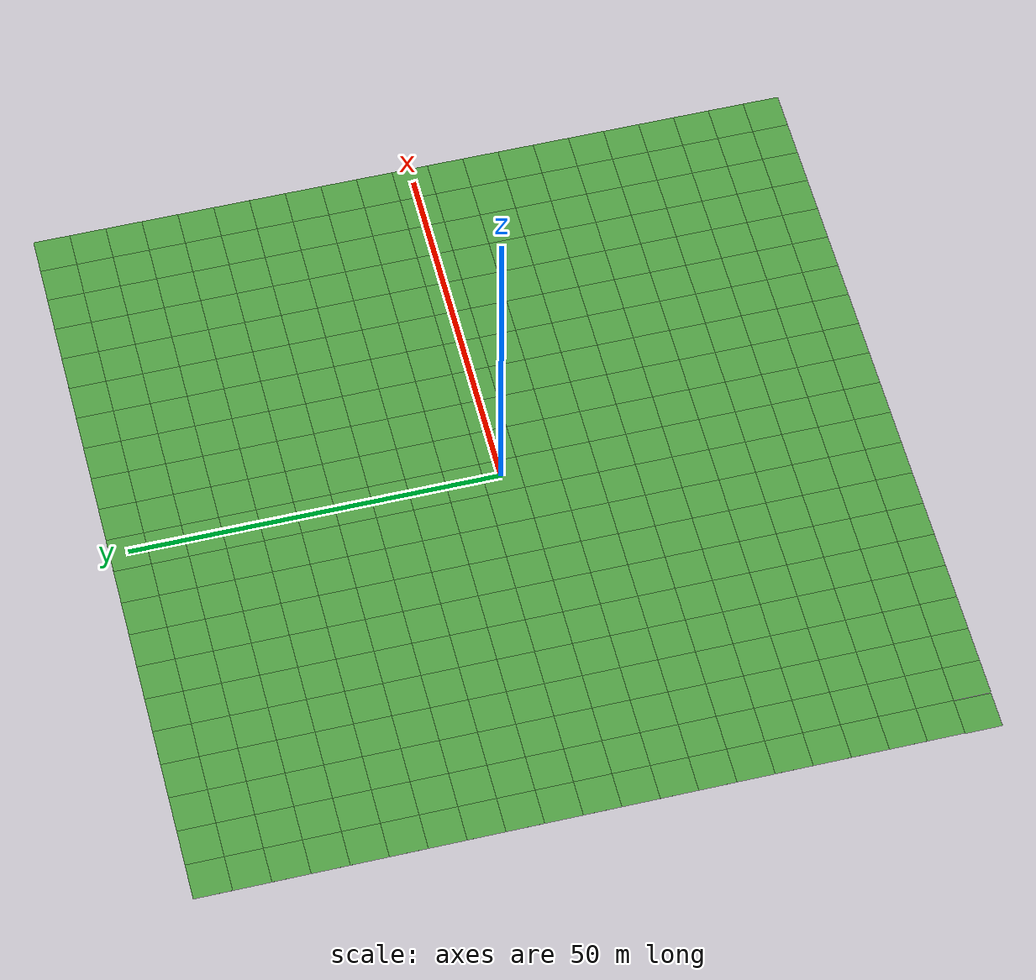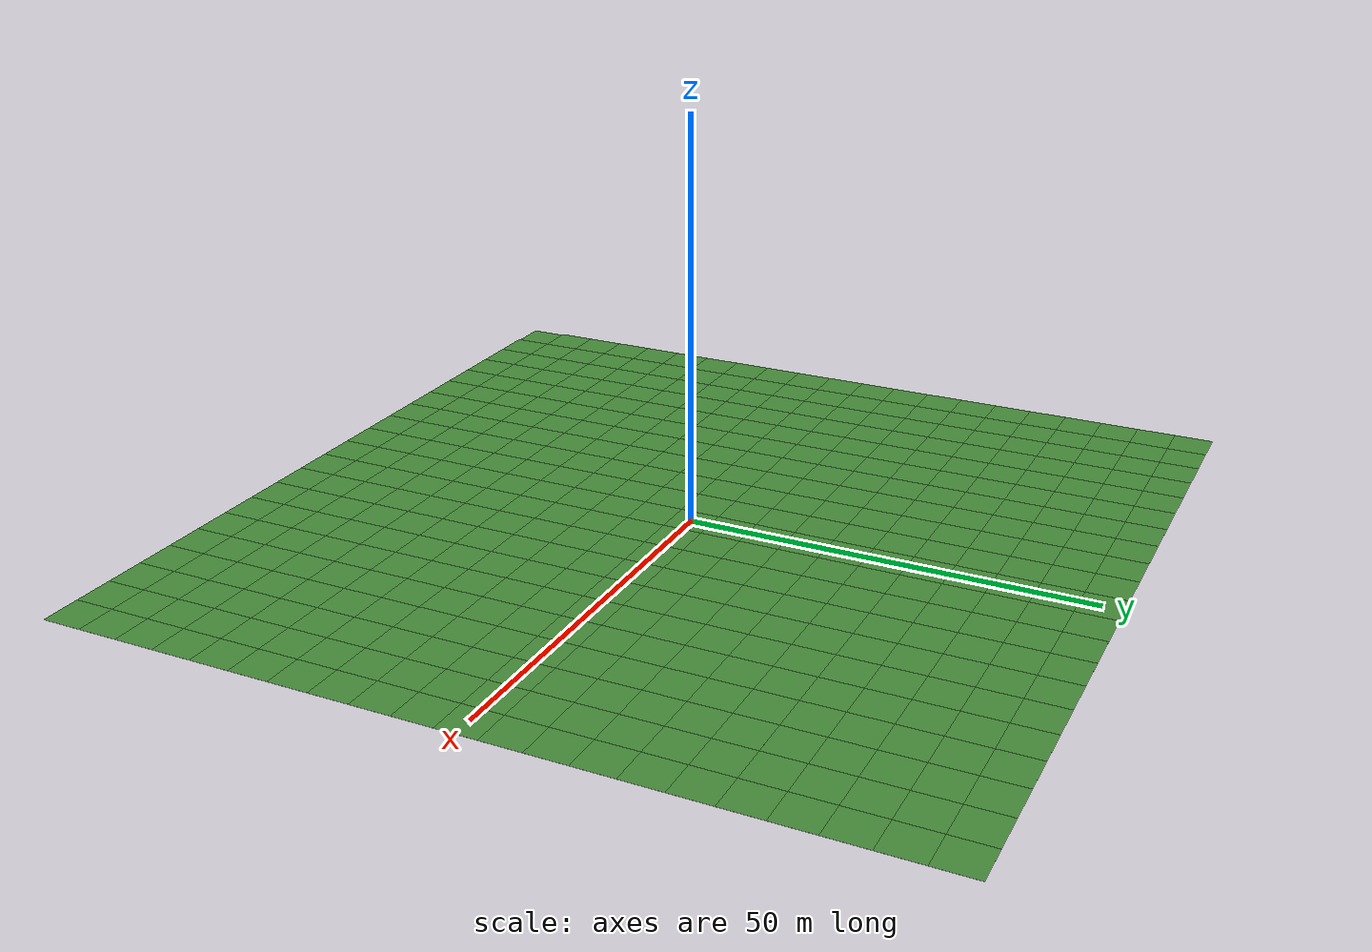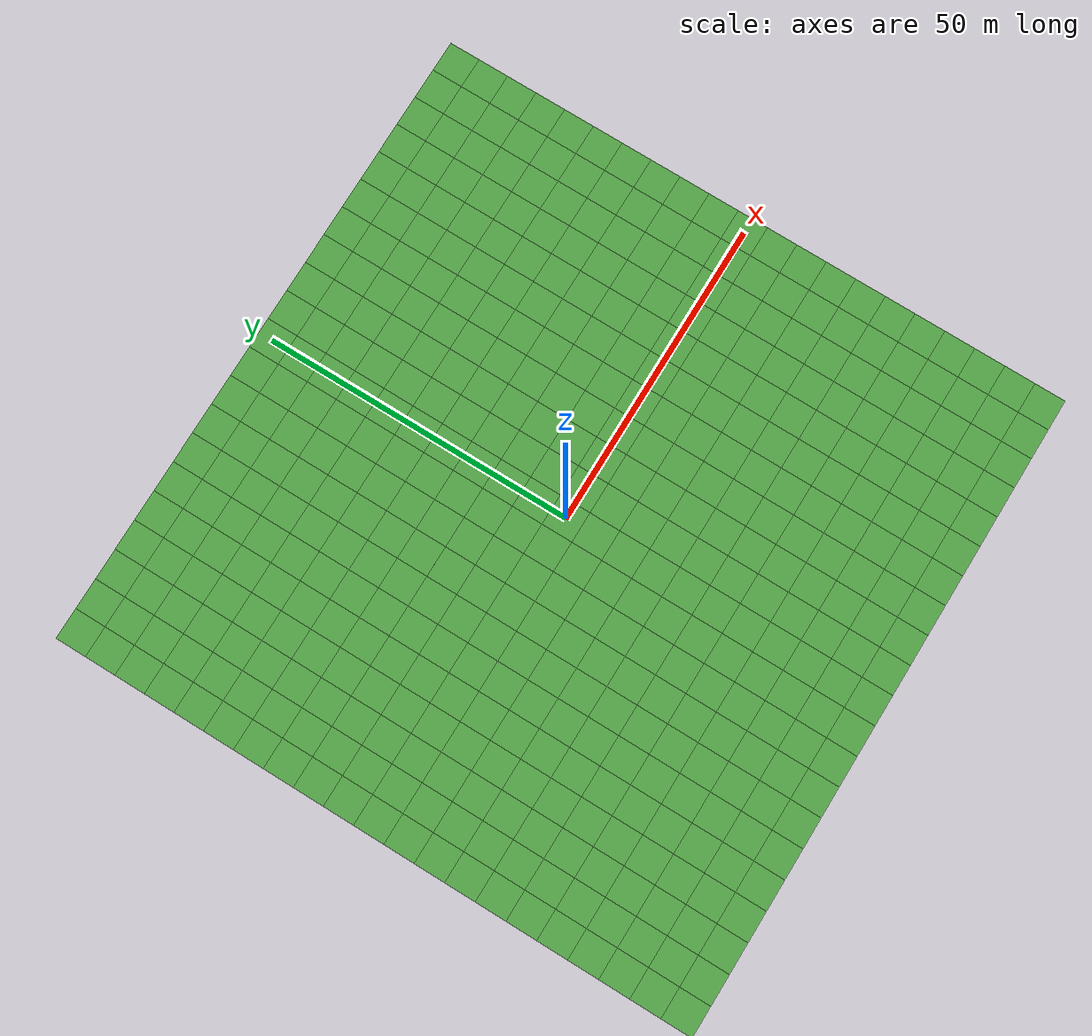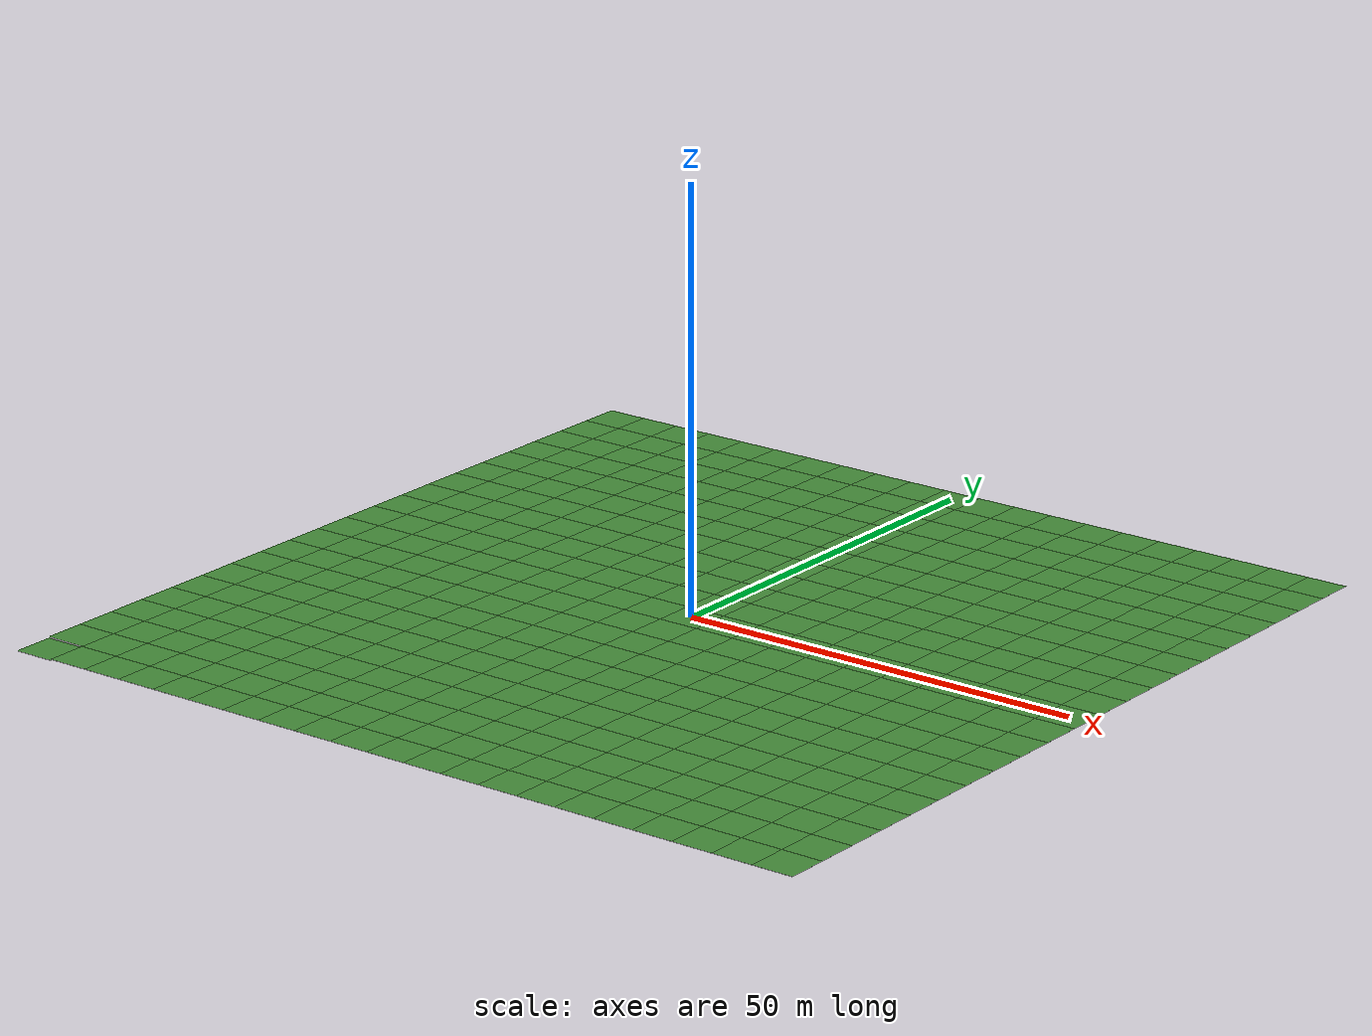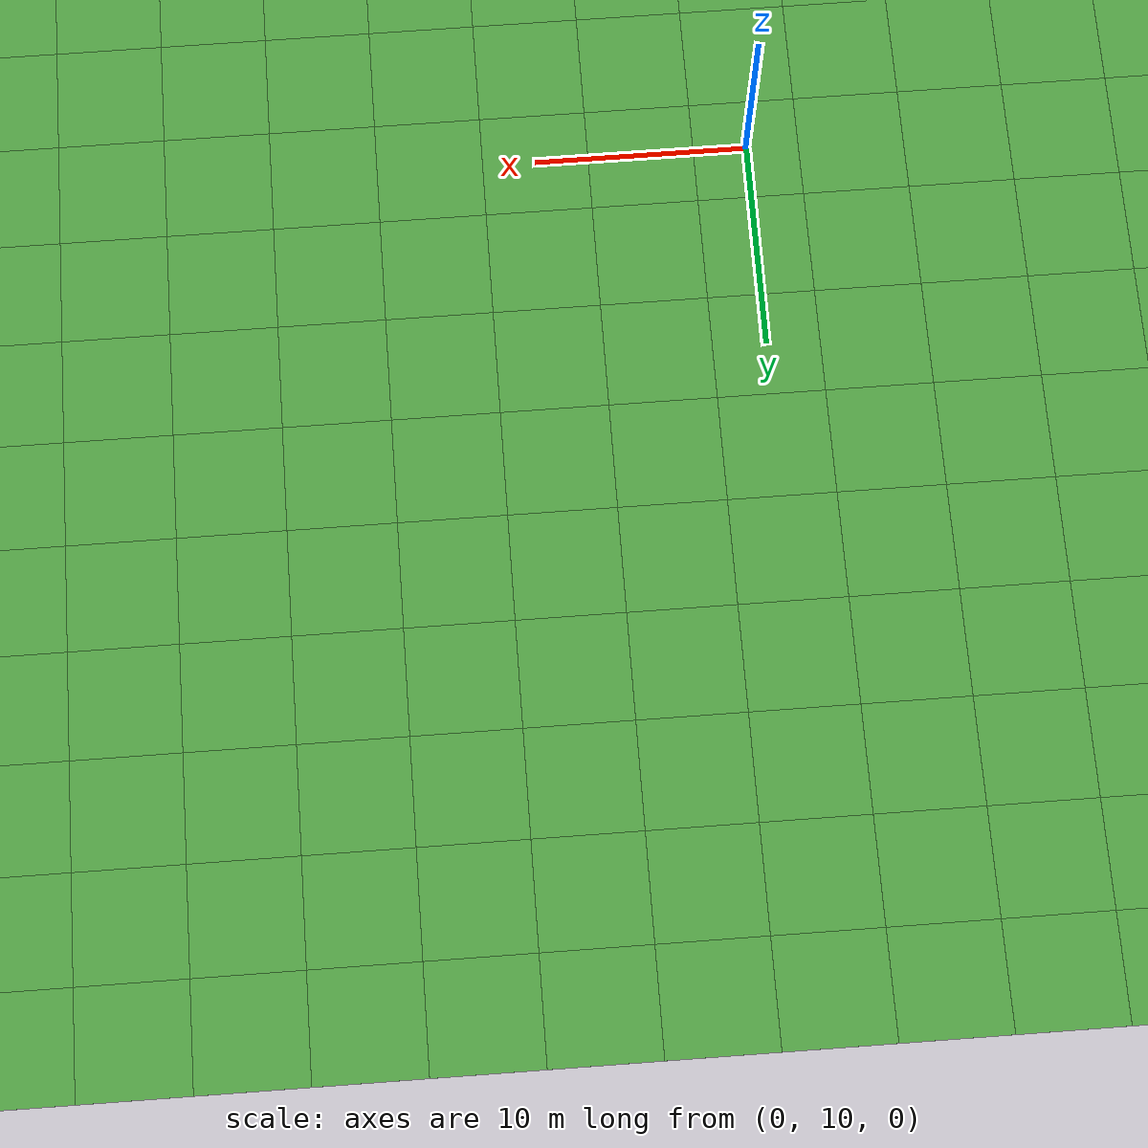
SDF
<?xml version="1.0" ?>
<sdf version="1.5">
  <model name="grass_plane">
    <static>true</static>
    <link name='link'>

      <collision name='collision'>
        <geometry>
          <plane>
            <normal>0 0 1</normal>
            <size>105.0 105.0</size>
          </plane>
        </geometry>
        <surface>
          <friction>
            <ode>
              <mu>0.5</mu>
              <mu2>.5</mu2>
            </ode>
          </friction>
        </surface>
      </collision>

          <visual name="visual_0_0">
            <!-- 步长也缩小 10 倍：50 -> 5，这样块与块刚好拼接 -->
            <pose>-50.0 -50.0 0 0 0 0</pose>
            <cast_shadows>false</cast_shadows>
            <geometry>
              <plane>
                <normal>0 0 1</normal>
                <!-- 每块尺寸缩小 10 倍：50x50 -> 5x5 -->
                <size>5.0 5.0</size>
              </plane>
            </geometry>
            <material>
              <script>
                <uri>model://grass_plane/materials/scripts</uri>
                <uri>model://grass_plane/materials/textures</uri>
                <name>vrc/grass</name>
              </script>
            </material>
          </visual>

          <visual name="visual_0_1">
            <!-- 步长也缩小 10 倍：50 -> 5，这样块与块刚好拼接 -->
            <pose>-50.0 -45.0 0 0 0 0</pose>
            <cast_shadows>false</cast_shadows>
            <geometry>
              <plane>
                <normal>0 0 1</normal>
                <!-- 每块尺寸缩小 10 倍：50x50 -> 5x5 -->
                <size>5.0 5.0</size>
              </plane>
            </geometry>
            <material>
              <script>
                <uri>model://grass_plane/materials/scripts</uri>
                <uri>model://grass_plane/materials/textures</uri>
                <name>vrc/grass</name>
              </script>
            </material>
          </visual>

          <visual name="visual_0_2">
            <!-- 步长也缩小 10 倍：50 -> 5，这样块与块刚好拼接 -->
            <pose>-50.0 -40.0 0 0 0 0</pose>
            <cast_shadows>false</cast_shadows>
            <geometry>
              <plane>
                <normal>0 0 1</normal>
                <!-- 每块尺寸缩小 10 倍：50x50 -> 5x5 -->
                <size>5.0 5.0</size>
              </plane>
            </geometry>
            <material>
              <script>
                <uri>model://grass_plane/materials/scripts</uri>
                <uri>model://grass_plane/materials/textures</uri>
                <name>vrc/grass</name>
              </script>
            </material>
          </visual>

          <visual name="visual_0_3">
            <!-- 步长也缩小 10 倍：50 -> 5，这样块与块刚好拼接 -->
            <pose>-50.0 -35.0 0 0 0 0</pose>
            <cast_shadows>false</cast_shadows>
            <geometry>
              <plane>
                <normal>0 0 1</normal>
                <!-- 每块尺寸缩小 10 倍：50x50 -> 5x5 -->
                <size>5.0 5.0</size>
              </plane>
            </geometry>
            <material>
              <script>
                <uri>model://grass_plane/materials/scripts</uri>
                <uri>model://grass_plane/materials/textures</uri>
                <name>vrc/grass</name>
              </script>
            </material>
          </visual>

          <visual name="visual_0_4">
            <!-- 步长也缩小 10 倍：50 -> 5，这样块与块刚好拼接 -->
            <pose>-50.0 -30.0 0 0 0 0</pose>
            <cast_shadows>false</cast_shadows>
            <geometry>
              <plane>
                <normal>0 0 1</normal>
                <!-- 每块尺寸缩小 10 倍：50x50 -> 5x5 -->
                <size>5.0 5.0</size>
              </plane>
            </geometry>
            <material>
              <script>
                <uri>model://grass_plane/materials/scripts</uri>
                <uri>model://grass_plane/materials/textures</uri>
                <name>vrc/grass</name>
              </script>
            </material>
          </visual>

          <visual name="visual_0_5">
            <!-- 步长也缩小 10 倍：50 -> 5，这样块与块刚好拼接 -->
            <pose>-50.0 -25.0 0 0 0 0</pose>
            <cast_shadows>false</cast_shadows>
            <geometry>
              <plane>
                <normal>0 0 1</normal>
                <!-- 每块尺寸缩小 10 倍：50x50 -> 5x5 -->
                <size>5.0 5.0</size>
              </plane>
            </geometry>
            <material>
              <script>
                <uri>model://grass_plane/materials/scripts</uri>
                <uri>model://grass_plane/materials/textures</uri>
                <name>vrc/grass</name>
              </script>
            </material>
          </visual>

          <visual name="visual_0_6">
            <!-- 步长也缩小 10 倍：50 -> 5，这样块与块刚好拼接 -->
            <pose>-50.0 -20.0 0 0 0 0</pose>
            <cast_shadows>false</cast_shadows>
            <geometry>
              <plane>
                <normal>0 0 1</normal>
                <!-- 每块尺寸缩小 10 倍：50x50 -> 5x5 -->
                <size>5.0 5.0</size>
              </plane>
            </geometry>
            <material>
              <script>
                <uri>model://grass_plane/materials/scripts</uri>
                <uri>model://grass_plane/materials/textures</uri>
                <name>vrc/grass</name>
              </script>
            </material>
          </visual>

          <visual name="visual_0_7">
            <!-- 步长也缩小 10 倍：50 -> 5，这样块与块刚好拼接 -->
            <pose>-50.0 -15.0 0 0 0 0</pose>
            <cast_shadows>false</cast_shadows>
            <geometry>
              <plane>
                <normal>0 0 1</normal>
                <!-- 每块尺寸缩小 10 倍：50x50 -> 5x5 -->
                <size>5.0 5.0</size>
              </plane>
            </geometry>
            <material>
              <script>
                <uri>model://grass_plane/materials/scripts</uri>
                <uri>model://grass_plane/materials/textures</uri>
                <name>vrc/grass</name>
              </script>
            </material>
          </visual>

          <visual name="visual_0_8">
            <!-- 步长也缩小 10 倍：50 -> 5，这样块与块刚好拼接 -->
            <pose>-50.0 -10.0 0 0 0 0</pose>
            <cast_shadows>false</cast_shadows>
            <geometry>
              <plane>
                <normal>0 0 1</normal>
                <!-- 每块尺寸缩小 10 倍：50x50 -> 5x5 -->
                <size>5.0 5.0</size>
              </plane>
            </geometry>
            <material>
              <script>
                <uri>model://grass_plane/materials/scripts</uri>
                <uri>model://grass_plane/materials/textures</uri>
                <name>vrc/grass</name>
              </script>
            </material>
          </visual>

          <visual name="visual_0_9">
            <!-- 步长也缩小 10 倍：50 -> 5，这样块与块刚好拼接 -->
            <pose>-50.0 -5.0 0 0 0 0</pose>
            <cast_shadows>false</cast_shadows>
            <geometry>
              <plane>
                <normal>0 0 1</normal>
                <!-- 每块尺寸缩小 10 倍：50x50 -> 5x5 -->
                <size>5.0 5.0</size>
              </plane>
            </geometry>
            <material>
              <script>
                <uri>model://grass_plane/materials/scripts</uri>
                <uri>model://grass_plane/materials/textures</uri>
                <name>vrc/grass</name>
              </script>
            </material>
          </visual>

          <visual name="visual_0_10">
            <!-- 步长也缩小 10 倍：50 -> 5，这样块与块刚好拼接 -->
            <pose>-50.0 0.0 0 0 0 0</pose>
            <cast_shadows>false</cast_shadows>
            <geometry>
              <plane>
                <normal>0 0 1</normal>
                <!-- 每块尺寸缩小 10 倍：50x50 -> 5x5 -->
                <size>5.0 5.0</size>
              </plane>
            </geometry>
            <material>
              <script>
                <uri>model://grass_plane/materials/scripts</uri>
                <uri>model://grass_plane/materials/textures</uri>
                <name>vrc/grass</name>
              </script>
            </material>
          </visual>

          <visual name="visual_0_11">
            <!-- 步长也缩小 10 倍：50 -> 5，这样块与块刚好拼接 -->
            <pose>-50.0 5.0 0 0 0 0</pose>
            <cast_shadows>false</cast_shadows>
            <geometry>
              <plane>
                <normal>0 0 1</normal>
                <!-- 每块尺寸缩小 10 倍：50x50 -> 5x5 -->
                <size>5.0 5.0</size>
              </plane>
            </geometry>
            <material>
              <script>
                <uri>model://grass_plane/materials/scripts</uri>
                <uri>model://grass_plane/materials/textures</uri>
                <name>vrc/grass</name>
              </script>
            </material>
          </visual>

          <visual name="visual_0_12">
            <!-- 步长也缩小 10 倍：50 -> 5，这样块与块刚好拼接 -->
            <pose>-50.0 10.0 0 0 0 0</pose>
            <cast_shadows>false</cast_shadows>
            <geometry>
              <plane>
                <normal>0 0 1</normal>
                <!-- 每块尺寸缩小 10 倍：50x50 -> 5x5 -->
                <size>5.0 5.0</size>
              </plane>
            </geometry>
            <material>
              <script>
                <uri>model://grass_plane/materials/scripts</uri>
                <uri>model://grass_plane/materials/textures</uri>
                <name>vrc/grass</name>
              </script>
            </material>
          </visual>

          <visual name="visual_0_13">
            <!-- 步长也缩小 10 倍：50 -> 5，这样块与块刚好拼接 -->
            <pose>-50.0 15.0 0 0 0 0</pose>
            <cast_shadows>false</cast_shadows>
            <geometry>
              <plane>
                <normal>0 0 1</normal>
                <!-- 每块尺寸缩小 10 倍：50x50 -> 5x5 -->
                <size>5.0 5.0</size>
              </plane>
            </geometry>
            <material>
              <script>
                <uri>model://grass_plane/materials/scripts</uri>
                <uri>model://grass_plane/materials/textures</uri>
                <name>vrc/grass</name>
              </script>
            </material>
          </visual>

          <visual name="visual_0_14">
            <!-- 步长也缩小 10 倍：50 -> 5，这样块与块刚好拼接 -->
            <pose>-50.0 20.0 0 0 0 0</pose>
            <cast_shadows>false</cast_shadows>
            <geometry>
              <plane>
                <normal>0 0 1</normal>
                <!-- 每块尺寸缩小 10 倍：50x50 -> 5x5 -->
                <size>5.0 5.0</size>
              </plane>
            </geometry>
            <material>
              <script>
                <uri>model://grass_plane/materials/scripts</uri>
                <uri>model://grass_plane/materials/textures</uri>
                <name>vrc/grass</name>
              </script>
            </material>
          </visual>

          <visual name="visual_0_15">
            <!-- 步长也缩小 10 倍：50 -> 5，这样块与块刚好拼接 -->
            <pose>-50.0 25.0 0 0 0 0</pose>
            <cast_shadows>false</cast_shadows>
            <geometry>
              <plane>
                <normal>0 0 1</normal>
                <!-- 每块尺寸缩小 10 倍：50x50 -> 5x5 -->
                <size>5.0 5.0</size>
              </plane>
            </geometry>
            <material>
              <script>
                <uri>model://grass_plane/materials/scripts</uri>
                <uri>model://grass_plane/materials/textures</uri>
                <name>vrc/grass</name>
              </script>
            </material>
          </visual>

          <visual name="visual_0_16">
            <!-- 步长也缩小 10 倍：50 -> 5，这样块与块刚好拼接 -->
            <pose>-50.0 30.0 0 0 0 0</pose>
            <cast_shadows>false</cast_shadows>
            <geometry>
              <plane>
                <normal>0 0 1</normal>
                <!-- 每块尺寸缩小 10 倍：50x50 -> 5x5 -->
                <size>5.0 5.0</size>
              </plane>
            </geometry>
            <material>
              <script>
                <uri>model://grass_plane/materials/scripts</uri>
                <uri>model://grass_plane/materials/textures</uri>
                <name>vrc/grass</name>
              </script>
            </material>
          </visual>

          <visual name="visual_0_17">
            <!-- 步长也缩小 10 倍：50 -> 5，这样块与块刚好拼接 -->
            <pose>-50.0 35.0 0 0 0 0</pose>
            <cast_shadows>false</cast_shadows>
            <geometry>
              <plane>
                <normal>0 0 1</normal>
                <!-- 每块尺寸缩小 10 倍：50x50 -> 5x5 -->
                <size>5.0 5.0</size>
              </plane>
            </geometry>
            <material>
              <script>
                <uri>model://grass_plane/materials/scripts</uri>
                <uri>model://grass_plane/materials/textures</uri>
                <name>vrc/grass</name>
              </script>
            </material>
          </visual>

          <visual name="visual_0_18">
            <!-- 步长也缩小 10 倍：50 -> 5，这样块与块刚好拼接 -->
            <pose>-50.0 40.0 0 0 0 0</pose>
            <cast_shadows>false</cast_shadows>
            <geometry>
              <plane>
                <normal>0 0 1</normal>
                <!-- 每块尺寸缩小 10 倍：50x50 -> 5x5 -->
                <size>5.0 5.0</size>
              </plane>
            </geometry>
            <material>
              <script>
                <uri>model://grass_plane/materials/scripts</uri>
                <uri>model://grass_plane/materials/textures</uri>
                <name>vrc/grass</name>
              </script>
            </material>
          </visual>

          <visual name="visual_0_19">
            <!-- 步长也缩小 10 倍：50 -> 5，这样块与块刚好拼接 -->
            <pose>-50.0 45.0 0 0 0 0</pose>
            <cast_shadows>false</cast_shadows>
            <geometry>
              <plane>
                <normal>0 0 1</normal>
                <!-- 每块尺寸缩小 10 倍：50x50 -> 5x5 -->
                <size>5.0 5.0</size>
              </plane>
            </geometry>
            <material>
              <script>
                <uri>model://grass_plane/materials/scripts</uri>
                <uri>model://grass_plane/materials/textures</uri>
                <name>vrc/grass</name>
              </script>
            </material>
          </visual>

          <visual name="visual_0_20">
            <!-- 步长也缩小 10 倍：50 -> 5，这样块与块刚好拼接 -->
            <pose>-50.0 50.0 0 0 0 0</pose>
            <cast_shadows>false</cast_shadows>
            <geometry>
              <plane>
                <normal>0 0 1</normal>
                <!-- 每块尺寸缩小 10 倍：50x50 -> 5x5 -->
                <size>5.0 5.0</size>
              </plane>
            </geometry>
            <material>
              <script>
                <uri>model://grass_plane/materials/scripts</uri>
                <uri>model://grass_plane/materials/textures</uri>
                <name>vrc/grass</name>
              </script>
            </material>
          </visual>

          <visual name="visual_1_0">
            <!-- 步长也缩小 10 倍：50 -> 5，这样块与块刚好拼接 -->
            <pose>-45.0 -50.0 0 0 0 0</pose>
            <cast_shadows>false</cast_shadows>
            <geometry>
              <plane>
                <normal>0 0 1</normal>
                <!-- 每块尺寸缩小 10 倍：50x50 -> 5x5 -->
                <size>5.0 5.0</size>
              </plane>
            </geometry>
            <material>
              <script>
                <uri>model://grass_plane/materials/scripts</uri>
                <uri>model://grass_plane/materials/textures</uri>
                <name>vrc/grass</name>
              </script>
            </material>
          </visual>

          <visual name="visual_1_1">
            <!-- 步长也缩小 10 倍：50 -> 5，这样块与块刚好拼接 -->
            <pose>-45.0 -45.0 0 0 0 0</pose>
            <cast_shadows>false</cast_shadows>
            <geometry>
              <plane>
                <normal>0 0 1</normal>
                <!-- 每块尺寸缩小 10 倍：50x50 -> 5x5 -->
                <size>5.0 5.0</size>
              </plane>
            </geometry>
            <material>
              <script>
                <uri>model://grass_plane/materials/scripts</uri>
                <uri>model://grass_plane/materials/textures</uri>
                <name>vrc/grass</name>
              </script>
            </material>
          </visual>

          <visual name="visual_1_2">
            <!-- 步长也缩小 10 倍：50 -> 5，这样块与块刚好拼接 -->
            <pose>-45.0 -40.0 0 0 0 0</pose>
            <cast_shadows>false</cast_shadows>
            <geometry>
              <plane>
                <normal>0 0 1</normal>
                <!-- 每块尺寸缩小 10 倍：50x50 -> 5x5 -->
                <size>5.0 5.0</size>
              </plane>
            </geometry>
            <material>
              <script>
                <uri>model://grass_plane/materials/scripts</uri>
                <uri>model://grass_plane/materials/textures</uri>
                <name>vrc/grass</name>
              </script>
            </material>
          </visual>

          <visual name="visual_1_3">
            <!-- 步长也缩小 10 倍：50 -> 5，这样块与块刚好拼接 -->
            <pose>-45.0 -35.0 0 0 0 0</pose>
            <cast_shadows>false</cast_shadows>
            <geometry>
              <plane>
                <normal>0 0 1</normal>
                <!-- 每块尺寸缩小 10 倍：50x50 -> 5x5 -->
                <size>5.0 5.0</size>
              </plane>
            </geometry>
            <material>
              <script>
                <uri>model://grass_plane/materials/scripts</uri>
                <uri>model://grass_plane/materials/textures</uri>
                <name>vrc/grass</name>
              </script>
            </material>
          </visual>

          <visual name="visual_1_4">
            <!-- 步长也缩小 10 倍：50 -> 5，这样块与块刚好拼接 -->
            <pose>-45.0 -30.0 0 0 0 0</pose>
            <cast_shadows>false</cast_shadows>
            <geometry>
              <plane>
                <normal>0 0 1</normal>
                <!-- 每块尺寸缩小 10 倍：50x50 -> 5x5 -->
                <size>5.0 5.0</size>
              </plane>
            </geometry>
            <material>
              <script>
                <uri>model://grass_plane/materials/scripts</uri>
                <uri>model://grass_plane/materials/textures</uri>
                <name>vrc/grass</name>
              </script>
            </material>
          </visual>

          <visual name="visual_1_5">
            <!-- 步长也缩小 10 倍：50 -> 5，这样块与块刚好拼接 -->
            <pose>-45.0 -25.0 0 0 0 0</pose>
            <cast_shadows>false</cast_shadows>
            <geometry>
              <plane>
                <normal>0 0 1</normal>
                <!-- 每块尺寸缩小 10 倍：50x50 -> 5x5 -->
                <size>5.0 5.0</size>
              </plane>
            </geometry>
            <material>
              <script>
                <uri>model://grass_plane/materials/scripts</uri>
                <uri>model://grass_plane/materials/textures</uri>
                <name>vrc/grass</name>
              </script>
            </material>
          </visual>

          <visual name="visual_1_6">
            <!-- 步长也缩小 10 倍：50 -> 5，这样块与块刚好拼接 -->
            <pose>-45.0 -20.0 0 0 0 0</pose>
            <cast_shadows>false</cast_shadows>
            <geometry>
              <plane>
                <normal>0 0 1</normal>
                <!-- 每块尺寸缩小 10 倍：50x50 -> 5x5 -->
                <size>5.0 5.0</size>
              </plane>
            </geometry>
            <material>
              <script>
                <uri>model://grass_plane/materials/scripts</uri>
                <uri>model://grass_plane/materials/textures</uri>
                <name>vrc/grass</name>
              </script>
            </material>
          </visual>

          <visual name="visual_1_7">
            <!-- 步长也缩小 10 倍：50 -> 5，这样块与块刚好拼接 -->
            <pose>-45.0 -15.0 0 0 0 0</pose>
            <cast_shadows>false</cast_shadows>
            <geometry>
              <plane>
                <normal>0 0 1</normal>
                <!-- 每块尺寸缩小 10 倍：50x50 -> 5x5 -->
                <size>5.0 5.0</size>
              </plane>
            </geometry>
            <material>
              <script>
                <uri>model://grass_plane/materials/scripts</uri>
                <uri>model://grass_plane/materials/textures</uri>
                <name>vrc/grass</name>
              </script>
            </material>
          </visual>

          <visual name="visual_1_8">
            <!-- 步长也缩小 10 倍：50 -> 5，这样块与块刚好拼接 -->
            <pose>-45.0 -10.0 0 0 0 0</pose>
            <cast_shadows>false</cast_shadows>
            <geometry>
              <plane>
                <normal>0 0 1</normal>
                <!-- 每块尺寸缩小 10 倍：50x50 -> 5x5 -->
                <size>5.0 5.0</size>
              </plane>
            </geometry>
            <material>
              <script>
                <uri>model://grass_plane/materials/scripts</uri>
                <uri>model://grass_plane/materials/textures</uri>
                <name>vrc/grass</name>
              </script>
            </material>
          </visual>

          <visual name="visual_1_9">
            <!-- 步长也缩小 10 倍：50 -> 5，这样块与块刚好拼接 -->
            <pose>-45.0 -5.0 0 0 0 0</pose>
            <cast_shadows>false</cast_shadows>
            <geometry>
              <plane>
                <normal>0 0 1</normal>
                <!-- 每块尺寸缩小 10 倍：50x50 -> 5x5 -->
                <size>5.0 5.0</size>
              </plane>
            </geometry>
            <material>
              <script>
                <uri>model://grass_plane/materials/scripts</uri>
                <uri>model://grass_plane/materials/textures</uri>
                <name>vrc/grass</name>
              </script>
            </material>
          </visual>

          <visual name="visual_1_10">
            <!-- 步长也缩小 10 倍：50 -> 5，这样块与块刚好拼接 -->
            <pose>-45.0 0.0 0 0 0 0</pose>
            <cast_shadows>false</cast_shadows>
            <geometry>
              <plane>
                <normal>0 0 1</normal>
                <!-- 每块尺寸缩小 10 倍：50x50 -> 5x5 -->
                <size>5.0 5.0</size>
              </plane>
            </geometry>
            <material>
              <script>
                <uri>model://grass_plane/materials/scripts</uri>
                <uri>model://grass_plane/materials/textures</uri>
                <name>vrc/grass</name>
              </script>
            </material>
          </visual>

          <visual name="visual_1_11">
            <!-- 步长也缩小 10 倍：50 -> 5，这样块与块刚好拼接 -->
            <pose>-45.0 5.0 0 0 0 0</pose>
            <cast_shadows>false</cast_shadows>
            <geometry>
              <plane>
                <normal>0 0 1</normal>
                <!-- 每块尺寸缩小 10 倍：50x50 -> 5x5 -->
                <size>5.0 5.0</size>
              </plane>
            </geometry>
            <material>
              <script>
                <uri>model://grass_plane/materials/scripts</uri>
                <uri>model://grass_plane/materials/textures</uri>
                <name>vrc/grass</name>
              </script>
            </material>
          </visual>

          <visual name="visual_1_12">
            <!-- 步长也缩小 10 倍：50 -> 5，这样块与块刚好拼接 -->
            <pose>-45.0 10.0 0 0 0 0</pose>
            <cast_shadows>false</cast_shadows>
            <geometry>
              <plane>
                <normal>0 0 1</normal>
                <!-- 每块尺寸缩小 10 倍：50x50 -> 5x5 -->
                <size>5.0 5.0</size>
              </plane>
            </geometry>
            <material>
              <script>
                <uri>model://grass_plane/materials/scripts</uri>
                <uri>model://grass_plane/materials/textures</uri>
                <name>vrc/grass</name>
              </script>
            </material>
          </visual>

          <visual name="visual_1_13">
            <!-- 步长也缩小 10 倍：50 -> 5，这样块与块刚好拼接 -->
            <pose>-45.0 15.0 0 0 0 0</pose>
            <cast_shadows>false</cast_shadows>
            <geometry>
              <plane>
                <normal>0 0 1</normal>
                <!-- 每块尺寸缩小 10 倍：50x50 -> 5x5 -->
                <size>5.0 5.0</size>
              </plane>
            </geometry>
            <material>
              <script>
                <uri>model://grass_plane/materials/scripts</uri>
                <uri>model://grass_plane/materials/textures</uri>
                <name>vrc/grass</name>
              </script>
            </material>
          </visual>

          <visual name="visual_1_14">
            <!-- 步长也缩小 10 倍：50 -> 5，这样块与块刚好拼接 -->
            <pose>-45.0 20.0 0 0 0 0</pose>
            <cast_shadows>false</cast_shadows>
            <geometry>
              <plane>
                <normal>0 0 1</normal>
                <!-- 每块尺寸缩小 10 倍：50x50 -> 5x5 -->
                <size>5.0 5.0</size>
              </plane>
            </geometry>
            <material>
              <script>
                <uri>model://grass_plane/materials/scripts</uri>
                <uri>model://grass_plane/materials/textures</uri>
                <name>vrc/grass</name>
              </script>
            </material>
          </visual>

          <visual name="visual_1_15">
            <!-- 步长也缩小 10 倍：50 -> 5，这样块与块刚好拼接 -->
            <pose>-45.0 25.0 0 0 0 0</pose>
            <cast_shadows>false</cast_shadows>
            <geometry>
              <plane>
                <normal>0 0 1</normal>
                <!-- 每块尺寸缩小 10 倍：50x50 -> 5x5 -->
                <size>5.0 5.0</size>
              </plane>
            </geometry>
            <material>
              <script>
                <uri>model://grass_plane/materials/scripts</uri>
                <uri>model://grass_plane/materials/textures</uri>
                <name>vrc/grass</name>
              </script>
            </material>
          </visual>

          <visual name="visual_1_16">
            <!-- 步长也缩小 10 倍：50 -> 5，这样块与块刚好拼接 -->
            <pose>-45.0 30.0 0 0 0 0</pose>
            <cast_shadows>false</cast_shadows>
            <geometry>
              <plane>
                <normal>0 0 1</normal>
                <!-- 每块尺寸缩小 10 倍：50x50 -> 5x5 -->
                <size>5.0 5.0</size>
              </plane>
            </geometry>
            <material>
              <script>
                <uri>model://grass_plane/materials/scripts</uri>
                <uri>model://grass_plane/materials/textures</uri>
                <name>vrc/grass</name>
              </script>
            </material>
          </visual>

          <visual name="visual_1_17">
            <!-- 步长也缩小 10 倍：50 -> 5，这样块与块刚好拼接 -->
            <pose>-45.0 35.0 0 0 0 0</pose>
            <cast_shadows>false</cast_shadows>
            <geometry>
              <plane>
                <normal>0 0 1</normal>
                <!-- 每块尺寸缩小 10 倍：50x50 -> 5x5 -->
                <size>5.0 5.0</size>
              </plane>
            </geometry>
            <material>
              <script>
                <uri>model://grass_plane/materials/scripts</uri>
                <uri>model://grass_plane/materials/textures</uri>
                <name>vrc/grass</name>
              </script>
            </material>
          </visual>

          <visual name="visual_1_18">
            <!-- 步长也缩小 10 倍：50 -> 5，这样块与块刚好拼接 -->
            <pose>-45.0 40.0 0 0 0 0</pose>
            <cast_shadows>false</cast_shadows>
            <geometry>
              <plane>
                <normal>0 0 1</normal>
                <!-- 每块尺寸缩小 10 倍：50x50 -> 5x5 -->
                <size>5.0 5.0</size>
              </plane>
            </geometry>
            <material>
              <script>
                <uri>model://grass_plane/materials/scripts</uri>
                <uri>model://grass_plane/materials/textures</uri>
                <name>vrc/grass</name>
              </script>
            </material>
          </visual>

          <visual name="visual_1_19">
            <!-- 步长也缩小 10 倍：50 -> 5，这样块与块刚好拼接 -->
            <pose>-45.0 45.0 0 0 0 0</pose>
            <cast_shadows>false</cast_shadows>
            <geometry>
              <plane>
                <normal>0 0 1</normal>
                <!-- 每块尺寸缩小 10 倍：50x50 -> 5x5 -->
                <size>5.0 5.0</size>
              </plane>
            </geometry>
            <material>
              <script>
                <uri>model://grass_plane/materials/scripts</uri>
                <uri>model://grass_plane/materials/textures</uri>
                <name>vrc/grass</name>
              </script>
            </material>
          </visual>

          <visual name="visual_1_20">
            <!-- 步长也缩小 10 倍：50 -> 5，这样块与块刚好拼接 -->
            <pose>-45.0 50.0 0 0 0 0</pose>
            <cast_shadows>false</cast_shadows>
            <geometry>
              <plane>
                <normal>0 0 1</normal>
                <!-- 每块尺寸缩小 10 倍：50x50 -> 5x5 -->
                <size>5.0 5.0</size>
              </plane>
            </geometry>
            <material>
              <script>
                <uri>model://grass_plane/materials/scripts</uri>
                <uri>model://grass_plane/materials/textures</uri>
                <name>vrc/grass</name>
              </script>
            </material>
          </visual>

          <visual name="visual_2_0">
            <!-- 步长也缩小 10 倍：50 -> 5，这样块与块刚好拼接 -->
            <pose>-40.0 -50.0 0 0 0 0</pose>
            <cast_shadows>false</cast_shadows>
            <geometry>
              <plane>
                <normal>0 0 1</normal>
                <!-- 每块尺寸缩小 10 倍：50x50 -> 5x5 -->
                <size>5.0 5.0</size>
              </plane>
            </geometry>
            <material>
              <script>
                <uri>model://grass_plane/materials/scripts</uri>
                <uri>model://grass_plane/materials/textures</uri>
                <name>vrc/grass</name>
              </script>
            </material>
          </visual>

          <visual name="visual_2_1">
            <!-- 步长也缩小 10 倍：50 -> 5，这样块与块刚好拼接 -->
            <pose>-40.0 -45.0 0 0 0 0</pose>
            <cast_shadows>false</cast_shadows>
            <geometry>
              <plane>
                <normal>0 0 1</normal>
                <!-- 每块尺寸缩小 10 倍：50x50 -> 5x5 -->
                <size>5.0 5.0</size>
              </plane>
            </geometry>
            <material>
              <script>
                <uri>model://grass_plane/materials/scripts</uri>
                <uri>model://grass_plane/materials/textures</uri>
                <name>vrc/grass</name>
              </script>
            </material>
          </visual>

          <visual name="visual_2_2">
            <!-- 步长也缩小 10 倍：50 -> 5，这样块与块刚好拼接 -->
            <pose>-40.0 -40.0 0 0 0 0</pose>
            <cast_shadows>false</cast_shadows>
            <geometry>
              <plane>
                <normal>0 0 1</normal>
                <!-- 每块尺寸缩小 10 倍：50x50 -> 5x5 -->
                <size>5.0 5.0</size>
              </plane>
            </geometry>
            <material>
              <script>
                <uri>model://grass_plane/materials/scripts</uri>
                <uri>model://grass_plane/materials/textures</uri>
                <name>vrc/grass</name>
              </script>
            </material>
          </visual>

          <visual name="visual_2_3">
            <!-- 步长也缩小 10 倍：50 -> 5，这样块与块刚好拼接 -->
            <pose>-40.0 -35.0 0 0 0 0</pose>
            <cast_shadows>false</cast_shadows>
            <geometry>
              <plane>
                <normal>0 0 1</normal>
                <!-- 每块尺寸缩小 10 倍：50x50 -> 5x5 -->
                <size>5.0 5.0</size>
              </plane>
            </geometry>
            <material>
              <script>
                <uri>model://grass_plane/materials/scripts</uri>
                <uri>model://grass_plane/materials/textures</uri>
                <name>vrc/grass</name>
              </script>
            </material>
          </visual>

          <visual name="visual_2_4">
            <!-- 步长也缩小 10 倍：50 -> 5，这样块与块刚好拼接 -->
            <pose>-40.0 -30.0 0 0 0 0</pose>
            <cast_shadows>false</cast_shadows>
            <geometry>
              <plane>
                <normal>0 0 1</normal>
                <!-- 每块尺寸缩小 10 倍：50x50 -> 5x5 -->
                <size>5.0 5.0</size>
              </plane>
            </geometry>
            <material>
              <script>
                <uri>model://grass_plane/materials/scripts</uri>
                <uri>model://grass_plane/materials/textures</uri>
                <name>vrc/grass</name>
              </script>
            </material>
          </visual>

          <visual name="visual_2_5">
            <!-- 步长也缩小 10 倍：50 -> 5，这样块与块刚好拼接 -->
            <pose>-40.0 -25.0 0 0 0 0</pose>
            <cast_shadows>false</cast_shadows>
            <geometry>
              <plane>
                <normal>0 0 1</normal>
                <!-- 每块尺寸缩小 10 倍：50x50 -> 5x5 -->
                <size>5.0 5.0</size>
              </plane>
            </geometry>
            <material>
              <script>
                <uri>model://grass_plane/materials/scripts</uri>
                <uri>model://grass_plane/materials/textures</uri>
                <name>vrc/grass</name>
              </script>
            </material>
          </visual>

          <visual name="visual_2_6">
            <!-- 步长也缩小 10 倍：50 -> 5，这样块与块刚好拼接 -->
            <pose>-40.0 -20.0 0 0 0 0</pose>
            <cast_shadows>false</cast_shadows>
            <geometry>
              <plane>
                <normal>0 0 1</normal>
                <!-- 每块尺寸缩小 10 倍：50x50 -> 5x5 -->
                <size>5.0 5.0</size>
              </plane>
            </geometry>
            <material>
              <script>
                <uri>model://grass_plane/materials/scripts</uri>
                <uri>model://grass_plane/materials/textures</uri>
                <name>vrc/grass</name>
              </script>
            </material>
          </visual>

          <visual name="visual_2_7">
            <!-- 步长也缩小 10 倍：50 -> 5，这样块与块刚好拼接 -->
            <pose>-40.0 -15.0 0 0 0 0</pose>
            <cast_shadows>false</cast_shadows>
            <geometry>
              <plane>
                <normal>0 0 1</normal>
                <!-- 每块尺寸缩小 10 倍：50x50 -> 5x5 -->
                <size>5.0 5.0</size>
              </plane>
            </geometry>
            <material>
              <script>
                <uri>model://grass_plane/materials/scripts</uri>
                <uri>model://grass_plane/materials/textures</uri>
                <name>vrc/grass</name>
              </script>
            </material>
          </visual>

          <visual name="visual_2_8">
            <!-- 步长也缩小 10 倍：50 -> 5，这样块与块刚好拼接 -->
            <pose>-40.0 -10.0 0 0 0 0</pose>
            <cast_shadows>false</cast_shadows>
            <geometry>
              <plane>
                <normal>0 0 1</normal>
                <!-- 每块尺寸缩小 10 倍：50x50 -> 5x5 -->
                <size>5.0 5.0</size>
              </plane>
            </geometry>
            <material>
              <script>
                <uri>model://grass_plane/materials/scripts</uri>
                <uri>model://grass_plane/materials/textures</uri>
                <name>vrc/grass</name>
              </script>
            </material>
          </visual>

          <visual name="visual_2_9">
            <!-- 步长也缩小 10 倍：50 -> 5，这样块与块刚好拼接 -->
            <pose>-40.0 -5.0 0 0 0 0</pose>
            <cast_shadows>false</cast_shadows>
            <geometry>
              <plane>
                <normal>0 0 1</normal>
                <!-- 每块尺寸缩小 10 倍：50x50 -> 5x5 -->
                <size>5.0 5.0</size>
              </plane>
            </geometry>
            <material>
              <script>
                <uri>model://grass_plane/materials/scripts</uri>
                <uri>model://grass_plane/materials/textures</uri>
                <name>vrc/grass</name>
              </script>
            </material>
          </visual>

          <visual name="visual_2_10">
            <!-- 步长也缩小 10 倍：50 -> 5，这样块与块刚好拼接 -->
            <pose>-40.0 0.0 0 0 0 0</pose>
            <cast_shadows>false</cast_shadows>
            <geometry>
              <plane>
                <normal>0 0 1</normal>
                <!-- 每块尺寸缩小 10 倍：50x50 -> 5x5 -->
                <size>5.0 5.0</size>
              </plane>
            </geometry>
            <material>
              <script>
                <uri>model://grass_plane/materials/scripts</uri>
                <uri>model://grass_plane/materials/textures</uri>
                <name>vrc/grass</name>
              </script>
            </material>
          </visual>

          <visual name="visual_2_11">
            <!-- 步长也缩小 10 倍：50 -> 5，这样块与块刚好拼接 -->
            <pose>-40.0 5.0 0 0 0 0</pose>
            <cast_shadows>false</cast_shadows>
            <geometry>
              <plane>
                <normal>0 0 1</normal>
                <!-- 每块尺寸缩小 10 倍：50x50 -> 5x5 -->
                <size>5.0 5.0</size>
              </plane>
            </geometry>
            <material>
              <script>
                <uri>model://grass_plane/materials/scripts</uri>
                <uri>model://grass_plane/materials/textures</uri>
                <name>vrc/grass</name>
              </script>
            </material>
          </visual>

          <visual name="visual_2_12">
            <!-- 步长也缩小 10 倍：50 -> 5，这样块与块刚好拼接 -->
            <pose>-40.0 10.0 0 0 0 0</pose>
            <cast_shadows>false</cast_shadows>
            <geometry>
              <plane>
                <normal>0 0 1</normal>
                <!-- 每块尺寸缩小 10 倍：50x50 -> 5x5 -->
                <size>5.0 5.0</size>
              </plane>
            </geometry>
            <material>
              <script>
                <uri>model://grass_plane/materials/scripts</uri>
                <uri>model://grass_plane/materials/textures</uri>
                <name>vrc/grass</name>
              </script>
            </material>
          </visual>

          <visual name="visual_2_13">
            <!-- 步长也缩小 10 倍：50 -> 5，这样块与块刚好拼接 -->
            <pose>-40.0 15.0 0 0 0 0</pose>
            <cast_shadows>false</cast_shadows>
            <geometry>
              <plane>
                <normal>0 0 1</normal>
                <!-- 每块尺寸缩小 10 倍：50x50 -> 5x5 -->
                <size>5.0 5.0</size>
              </plane>
            </geometry>
            <material>
              <script>
                <uri>model://grass_plane/materials/scripts</uri>
                <uri>model://grass_plane/materials/textures</uri>
                <name>vrc/grass</name>
              </script>
            </material>
          </visual>

          <visual name="visual_2_14">
            <!-- 步长也缩小 10 倍：50 -> 5，这样块与块刚好拼接 -->
            <pose>-40.0 20.0 0 0 0 0</pose>
            <cast_shadows>false</cast_shadows>
            <geometry>
              <plane>
                <normal>0 0 1</normal>
                <!-- 每块尺寸缩小 10 倍：50x50 -> 5x5 -->
                <size>5.0 5.0</size>
              </plane>
            </geometry>
            <material>
              <script>
                <uri>model://grass_plane/materials/scripts</uri>
                <uri>model://grass_plane/materials/textures</uri>
                <name>vrc/grass</name>
              </script>
            </material>
          </visual>

          <visual name="visual_2_15">
            <!-- 步长也缩小 10 倍：50 -> 5，这样块与块刚好拼接 -->
            <pose>-40.0 25.0 0 0 0 0</pose>
            <cast_shadows>false</cast_shadows>
            <geometry>
              <plane>
                <normal>0 0 1</normal>
                <!-- 每块尺寸缩小 10 倍：50x50 -> 5x5 -->
                <size>5.0 5.0</size>
              </plane>
            </geometry>
            <material>
              <script>
                <uri>model://grass_plane/materials/scripts</uri>
                <uri>model://grass_plane/materials/textures</uri>
                <name>vrc/grass</name>
              </script>
            </material>
          </visual>

          <visual name="visual_2_16">
            <!-- 步长也缩小 10 倍：50 -> 5，这样块与块刚好拼接 -->
            <pose>-40.0 30.0 0 0 0 0</pose>
            <cast_shadows>false</cast_shadows>
            <geometry>
              <plane>
                <normal>0 0 1</normal>
                <!-- 每块尺寸缩小 10 倍：50x50 -> 5x5 -->
                <size>5.0 5.0</size>
              </plane>
            </geometry>
            <material>
              <script>
                <uri>model://grass_plane/materials/scripts</uri>
                <uri>model://grass_plane/materials/textures</uri>
                <name>vrc/grass</name>
              </script>
            </material>
          </visual>

          <visual name="visual_2_17">
            <!-- 步长也缩小 10 倍：50 -> 5，这样块与块刚好拼接 -->
            <pose>-40.0 35.0 0 0 0 0</pose>
            <cast_shadows>false</cast_shadows>
            <geometry>
              <plane>
                <normal>0 0 1</normal>
                <!-- 每块尺寸缩小 10 倍：50x50 -> 5x5 -->
                <size>5.0 5.0</size>
              </plane>
            </geometry>
            <material>
              <script>
                <uri>model://grass_plane/materials/scripts</uri>
                <uri>model://grass_plane/materials/textures</uri>
                <name>vrc/grass</name>
              </script>
            </material>
          </visual>

          <visual name="visual_2_18">
            <!-- 步长也缩小 10 倍：50 -> 5，这样块与块刚好拼接 -->
            <pose>-40.0 40.0 0 0 0 0</pose>
            <cast_shadows>false</cast_shadows>
            <geometry>
              <plane>
                <normal>0 0 1</normal>
                <!-- 每块尺寸缩小 10 倍：50x50 -> 5x5 -->
                <size>5.0 5.0</size>
              </plane>
            </geometry>
            <material>
              <script>
                <uri>model://grass_plane/materials/scripts</uri>
                <uri>model://grass_plane/materials/textures</uri>
                <name>vrc/grass</name>
              </script>
            </material>
          </visual>

          <visual name="visual_2_19">
            <!-- 步长也缩小 10 倍：50 -> 5，这样块与块刚好拼接 -->
            <pose>-40.0 45.0 0 0 0 0</pose>
            <cast_shadows>false</cast_shadows>
            <geometry>
              <plane>
                <normal>0 0 1</normal>
                <!-- 每块尺寸缩小 10 倍：50x50 -> 5x5 -->
                <size>5.0 5.0</size>
              </plane>
            </geometry>
            <material>
              <script>
                <uri>model://grass_plane/materials/scripts</uri>
                <uri>model://grass_plane/materials/textures</uri>
                <name>vrc/grass</name>
              </script>
            </material>
          </visual>

          <visual name="visual_2_20">
            <!-- 步长也缩小 10 倍：50 -> 5，这样块与块刚好拼接 -->
            <pose>-40.0 50.0 0 0 0 0</pose>
            <cast_shadows>false</cast_shadows>
            <geometry>
              <plane>
                <normal>0 0 1</normal>
                <!-- 每块尺寸缩小 10 倍：50x50 -> 5x5 -->
                <size>5.0 5.0</size>
              </plane>
            </geometry>
            <material>
              <script>
                <uri>model://grass_plane/materials/scripts</uri>
                <uri>model://grass_plane/materials/textures</uri>
                <name>vrc/grass</name>
              </script>
            </material>
          </visual>

          <visual name="visual_3_0">
            <!-- 步长也缩小 10 倍：50 -> 5，这样块与块刚好拼接 -->
            <pose>-35.0 -50.0 0 0 0 0</pose>
            <cast_shadows>false</cast_shadows>
            <geometry>
              <plane>
                <normal>0 0 1</normal>
                <!-- 每块尺寸缩小 10 倍：50x50 -> 5x5 -->
                <size>5.0 5.0</size>
              </plane>
            </geometry>
            <material>
              <script>
                <uri>model://grass_plane/materials/scripts</uri>
                <uri>model://grass_plane/materials/textures</uri>
                <name>vrc/grass</name>
              </script>
            </material>
          </visual>

          <visual name="visual_3_1">
            <!-- 步长也缩小 10 倍：50 -> 5，这样块与块刚好拼接 -->
            <pose>-35.0 -45.0 0 0 0 0</pose>
            <cast_shadows>false</cast_shadows>
            <geometry>
              <plane>
                <normal>0 0 1</normal>
                <!-- 每块尺寸缩小 10 倍：50x50 -> 5x5 -->
                <size>5.0 5.0</size>
              </plane>
            </geometry>
            <material>
              <script>
                <uri>model://grass_plane/materials/scripts</uri>
                <uri>model://grass_plane/materials/textures</uri>
                <name>vrc/grass</name>
              </script>
            </material>
          </visual>

          <visual name="visual_3_2">
            <!-- 步长也缩小 10 倍：50 -> 5，这样块与块刚好拼接 -->
            <pose>-35.0 -40.0 0 0 0 0</pose>
            <cast_shadows>false</cast_shadows>
            <geometry>
              <plane>
                <normal>0 0 1</normal>
                <!-- 每块尺寸缩小 10 倍：50x50 -> 5x5 -->
                <size>5.0 5.0</size>
              </plane>
            </geometry>
            <material>
              <script>
                <uri>model://grass_plane/materials/scripts</uri>
                <uri>model://grass_plane/materials/textures</uri>
                <name>vrc/grass</name>
              </script>
            </material>
          </visual>

          <visual name="visual_3_3">
            <!-- 步长也缩小 10 倍：50 -> 5，这样块与块刚好拼接 -->
            <pose>-35.0 -35.0 0 0 0 0</pose>
            <cast_shadows>false</cast_shadows>
            <geometry>
              <plane>
                <normal>0 0 1</normal>
                <!-- 每块尺寸缩小 10 倍：50x50 -> 5x5 -->
                <size>5.0 5.0</size>
              </plane>
            </geometry>
            <material>
              <script>
                <uri>model://grass_plane/materials/scripts</uri>
                <uri>model://grass_plane/materials/textures</uri>
                <name>vrc/grass</name>
              </script>
            </material>
          </visual>

          <visual name="visual_3_4">
            <!-- 步长也缩小 10 倍：50 -> 5，这样块与块刚好拼接 -->
            <pose>-35.0 -30.0 0 0 0 0</pose>
            <cast_shadows>false</cast_shadows>
            <geometry>
              <plane>
                <normal>0 0 1</normal>
                <!-- 每块尺寸缩小 10 倍：50x50 -> 5x5 -->
                <size>5.0 5.0</size>
              </plane>
            </geometry>
            <material>
              <script>
                <uri>model://grass_plane/materials/scripts</uri>
                <uri>model://grass_plane/materials/textures</uri>
                <name>vrc/grass</name>
              </script>
            </material>
          </visual>

          <visual name="visual_3_5">
            <!-- 步长也缩小 10 倍：50 -> 5，这样块与块刚好拼接 -->
            <pose>-35.0 -25.0 0 0 0 0</pose>
            <cast_shadows>false</cast_shadows>
            <geometry>
              <plane>
                <normal>0 0 1</normal>
                <!-- 每块尺寸缩小 10 倍：50x50 -> 5x5 -->
                <size>5.0 5.0</size>
              </plane>
            </geometry>
            <material>
              <script>
                <uri>model://grass_plane/materials/scripts</uri>
                <uri>model://grass_plane/materials/textures</uri>
                <name>vrc/grass</name>
              </script>
            </material>
          </visual>

          <visual name="visual_3_6">
            <!-- 步长也缩小 10 倍：50 -> 5，这样块与块刚好拼接 -->
            <pose>-35.0 -20.0 0 0 0 0</pose>
            <cast_shadows>false</cast_shadows>
            <geometry>
              <plane>
                <normal>0 0 1</normal>
                <!-- 每块尺寸缩小 10 倍：50x50 -> 5x5 -->
                <size>5.0 5.0</size>
              </plane>
            </geometry>
            <material>
              <script>
                <uri>model://grass_plane/materials/scripts</uri>
                <uri>model://grass_plane/materials/textures</uri>
                <name>vrc/grass</name>
              </script>
            </material>
          </visual>

          <visual name="visual_3_7">
            <!-- 步长也缩小 10 倍：50 -> 5，这样块与块刚好拼接 -->
            <pose>-35.0 -15.0 0 0 0 0</pose>
            <cast_shadows>false</cast_shadows>
            <geometry>
              <plane>
                <normal>0 0 1</normal>
                <!-- 每块尺寸缩小 10 倍：50x50 -> 5x5 -->
                <size>5.0 5.0</size>
              </plane>
            </geometry>
            <material>
              <script>
                <uri>model://grass_plane/materials/scripts</uri>
                <uri>model://grass_plane/materials/textures</uri>
                <name>vrc/grass</name>
              </script>
            </material>
          </visual>

          <visual name="visual_3_8">
            <!-- 步长也缩小 10 倍：50 -> 5，这样块与块刚好拼接 -->
            <pose>-35.0 -10.0 0 0 0 0</pose>
            <cast_shadows>false</cast_shadows>
            <geometry>
              <plane>
                <normal>0 0 1</normal>
                <!-- 每块尺寸缩小 10 倍：50x50 -> 5x5 -->
                <size>5.0 5.0</size>
              </plane>
            </geometry>
            <material>
              <script>
                <uri>model://grass_plane/materials/scripts</uri>
                <uri>model://grass_plane/materials/textures</uri>
                <name>vrc/grass</name>
              </script>
            </material>
          </visual>

          <visual name="visual_3_9">
            <!-- 步长也缩小 10 倍：50 -> 5，这样块与块刚好拼接 -->
            <pose>-35.0 -5.0 0 0 0 0</pose>
            <cast_shadows>false</cast_shadows>
            <geometry>
              <plane>
                <normal>0 0 1</normal>
                <!-- 每块尺寸缩小 10 倍：50x50 -> 5x5 -->
                <size>5.0 5.0</size>
              </plane>
            </geometry>
            <material>
              <script>
                <uri>model://grass_plane/materials/scripts</uri>
                <uri>model://grass_plane/materials/textures</uri>
                <name>vrc/grass</name>
              </script>
            </material>
          </visual>

          <visual name="visual_3_10">
            <!-- 步长也缩小 10 倍：50 -> 5，这样块与块刚好拼接 -->
            <pose>-35.0 0.0 0 0 0 0</pose>
            <cast_shadows>false</cast_shadows>
            <geometry>
              <plane>
                <normal>0 0 1</normal>
                <!-- 每块尺寸缩小 10 倍：50x50 -> 5x5 -->
                <size>5.0 5.0</size>
              </plane>
            </geometry>
            <material>
              <script>
                <uri>model://grass_plane/materials/scripts</uri>
                <uri>model://grass_plane/materials/textures</uri>
                <name>vrc/grass</name>
              </script>
            </material>
          </visual>

          <visual name="visual_3_11">
            <!-- 步长也缩小 10 倍：50 -> 5，这样块与块刚好拼接 -->
            <pose>-35.0 5.0 0 0 0 0</pose>
            <cast_shadows>false</cast_shadows>
            <geometry>
              <plane>
                <normal>0 0 1</normal>
                <!-- 每块尺寸缩小 10 倍：50x50 -> 5x5 -->
                <size>5.0 5.0</size>
              </plane>
            </geometry>
            <material>
              <script>
                <uri>model://grass_plane/materials/scripts</uri>
                <uri>model://grass_plane/materials/textures</uri>
                <name>vrc/grass</name>
              </script>
            </material>
          </visual>

          <visual name="visual_3_12">
            <!-- 步长也缩小 10 倍：50 -> 5，这样块与块刚好拼接 -->
            <pose>-35.0 10.0 0 0 0 0</pose>
            <cast_shadows>false</cast_shadows>
            <geometry>
              <plane>
                <normal>0 0 1</normal>
                <!-- 每块尺寸缩小 10 倍：50x50 -> 5x5 -->
                <size>5.0 5.0</size>
              </plane>
            </geometry>
            <material>
              <script>
                <uri>model://grass_plane/materials/scripts</uri>
                <uri>model://grass_plane/materials/textures</uri>
                <name>vrc/grass</name>
              </script>
            </material>
          </visual>

          <visual name="visual_3_13">
            <!-- 步长也缩小 10 倍：50 -> 5，这样块与块刚好拼接 -->
            <pose>-35.0 15.0 0 0 0 0</pose>
            <cast_shadows>false</cast_shadows>
            <geometry>
              <plane>
                <normal>0 0 1</normal>
                <!-- 每块尺寸缩小 10 倍：50x50 -> 5x5 -->
                <size>5.0 5.0</size>
              </plane>
            </geometry>
            <material>
              <script>
                <uri>model://grass_plane/materials/scripts</uri>
                <uri>model://grass_plane/materials/textures</uri>
                <name>vrc/grass</name>
              </script>
            </material>
          </visual>

          <visual name="visual_3_14">
            <!-- 步长也缩小 10 倍：50 -> 5，这样块与块刚好拼接 -->
            <pose>-35.0 20.0 0 0 0 0</pose>
            <cast_shadows>false</cast_shadows>
            <geometry>
              <plane>
                <normal>0 0 1</normal>
                <!-- 每块尺寸缩小 10 倍：50x50 -> 5x5 -->
                <size>5.0 5.0</size>
              </plane>
            </geometry>
            <material>
              <script>
                <uri>model://grass_plane/materials/scripts</uri>
                <uri>model://grass_plane/materials/textures</uri>
                <name>vrc/grass</name>
              </script>
            </material>
          </visual>

          <visual name="visual_3_15">
            <!-- 步长也缩小 10 倍：50 -> 5，这样块与块刚好拼接 -->
            <pose>-35.0 25.0 0 0 0 0</pose>
            <cast_shadows>false</cast_shadows>
            <geometry>
              <plane>
                <normal>0 0 1</normal>
                <!-- 每块尺寸缩小 10 倍：50x50 -> 5x5 -->
                <size>5.0 5.0</size>
              </plane>
            </geometry>
            <material>
              <script>
                <uri>model://grass_plane/materials/scripts</uri>
                <uri>model://grass_plane/materials/textures</uri>
                <name>vrc/grass</name>
              </script>
            </material>
          </visual>

          <visual name="visual_3_16">
            <!-- 步长也缩小 10 倍：50 -> 5，这样块与块刚好拼接 -->
            <pose>-35.0 30.0 0 0 0 0</pose>
            <cast_shadows>false</cast_shadows>
            <geometry>
              <plane>
                <normal>0 0 1</normal>
                <!-- 每块尺寸缩小 10 倍：50x50 -> 5x5 -->
                <size>5.0 5.0</size>
              </plane>
            </geometry>
            <material>
              <script>
                <uri>model://grass_plane/materials/scripts</uri>
                <uri>model://grass_plane/materials/textures</uri>
                <name>vrc/grass</name>
              </script>
            </material>
          </visual>

          <visual name="visual_3_17">
            <!-- 步长也缩小 10 倍：50 -> 5，这样块与块刚好拼接 -->
            <pose>-35.0 35.0 0 0 0 0</pose>
            <cast_shadows>false</cast_shadows>
            <geometry>
              <plane>
                <normal>0 0 1</normal>
                <!-- 每块尺寸缩小 10 倍：50x50 -> 5x5 -->
                <size>5.0 5.0</size>
              </plane>
            </geometry>
            <material>
              <script>
                <uri>model://grass_plane/materials/scripts</uri>
                <uri>model://grass_plane/materials/textures</uri>
                <name>vrc/grass</name>
              </script>
            </material>
          </visual>

          <visual name="visual_3_18">
            <!-- 步长也缩小 10 倍：50 -> 5，这样块与块刚好拼接 -->
            <pose>-35.0 40.0 0 0 0 0</pose>
            <cast_shadows>false</cast_shadows>
            <geometry>
              <plane>
                <normal>0 0 1</normal>
                <!-- 每块尺寸缩小 10 倍：50x50 -> 5x5 -->
                <size>5.0 5.0</size>
              </plane>
            </geometry>
            <material>
              <script>
                <uri>model://grass_plane/materials/scripts</uri>
                <uri>model://grass_plane/materials/textures</uri>
                <name>vrc/grass</name>
              </script>
            </material>
          </visual>

          <visual name="visual_3_19">
            <!-- 步长也缩小 10 倍：50 -> 5，这样块与块刚好拼接 -->
            <pose>-35.0 45.0 0 0 0 0</pose>
            <cast_shadows>false</cast_shadows>
            <geometry>
              <plane>
                <normal>0 0 1</normal>
                <!-- 每块尺寸缩小 10 倍：50x50 -> 5x5 -->
                <size>5.0 5.0</size>
              </plane>
            </geometry>
            <material>
              <script>
                <uri>model://grass_plane/materials/scripts</uri>
                <uri>model://grass_plane/materials/textures</uri>
                <name>vrc/grass</name>
              </script>
            </material>
          </visual>

          <visual name="visual_3_20">
            <!-- 步长也缩小 10 倍：50 -> 5，这样块与块刚好拼接 -->
            <pose>-35.0 50.0 0 0 0 0</pose>
            <cast_shadows>false</cast_shadows>
            <geometry>
              <plane>
                <normal>0 0 1</normal>
                <!-- 每块尺寸缩小 10 倍：50x50 -> 5x5 -->
                <size>5.0 5.0</size>
              </plane>
            </geometry>
            <material>
              <script>
                <uri>model://grass_plane/materials/scripts</uri>
                <uri>model://grass_plane/materials/textures</uri>
                <name>vrc/grass</name>
              </script>
            </material>
          </visual>

          <visual name="visual_4_0">
            <!-- 步长也缩小 10 倍：50 -> 5，这样块与块刚好拼接 -->
            <pose>-30.0 -50.0 0 0 0 0</pose>
            <cast_shadows>false</cast_shadows>
            <geometry>
              <plane>
                <normal>0 0 1</normal>
                <!-- 每块尺寸缩小 10 倍：50x50 -> 5x5 -->
                <size>5.0 5.0</size>
              </plane>
            </geometry>
            <material>
              <script>
                <uri>model://grass_plane/materials/scripts</uri>
                <uri>model://grass_plane/materials/textures</uri>
                <name>vrc/grass</name>
              </script>
            </material>
          </visual>

          <visual name="visual_4_1">
            <!-- 步长也缩小 10 倍：50 -> 5，这样块与块刚好拼接 -->
            <pose>-30.0 -45.0 0 0 0 0</pose>
            <cast_shadows>false</cast_shadows>
            <geometry>
              <plane>
                <normal>0 0 1</normal>
                <!-- 每块尺寸缩小 10 倍：50x50 -> 5x5 -->
                <size>5.0 5.0</size>
              </plane>
            </geometry>
            <material>
              <script>
                <uri>model://grass_plane/materials/scripts</uri>
                <uri>model://grass_plane/materials/textures</uri>
                <name>vrc/grass</name>
              </script>
            </material>
          </visual>

          <visual name="visual_4_2">
            <!-- 步长也缩小 10 倍：50 -> 5，这样块与块刚好拼接 -->
            <pose>-30.0 -40.0 0 0 0 0</pose>
            <cast_shadows>false</cast_shadows>
            <geometry>
              <plane>
                <normal>0 0 1</normal>
                <!-- 每块尺寸缩小 10 倍：50x50 -> 5x5 -->
                <size>5.0 5.0</size>
              </plane>
            </geometry>
            <material>
              <script>
                <uri>model://grass_plane/materials/scripts</uri>
                <uri>model://grass_plane/materials/textures</uri>
                <name>vrc/grass</name>
              </script>
            </material>
          </visual>

          <visual name="visual_4_3">
            <!-- 步长也缩小 10 倍：50 -> 5，这样块与块刚好拼接 -->
            <pose>-30.0 -35.0 0 0 0 0</pose>
            <cast_shadows>false</cast_shadows>
            <geometry>
              <plane>
                <normal>0 0 1</normal>
                <!-- 每块尺寸缩小 10 倍：50x50 -> 5x5 -->
                <size>5.0 5.0</size>
              </plane>
            </geometry>
            <material>
              <script>
                <uri>model://grass_plane/materials/scripts</uri>
                <uri>model://grass_plane/materials/textures</uri>
                <name>vrc/grass</name>
              </script>
            </material>
          </visual>

          <visual name="visual_4_4">
            <!-- 步长也缩小 10 倍：50 -> 5，这样块与块刚好拼接 -->
            <pose>-30.0 -30.0 0 0 0 0</pose>
            <cast_shadows>false</cast_shadows>
            <geometry>
              <plane>
                <normal>0 0 1</normal>
                <!-- 每块尺寸缩小 10 倍：50x50 -> 5x5 -->
                <size>5.0 5.0</size>
              </plane>
            </geometry>
            <material>
              <script>
                <uri>model://grass_plane/materials/scripts</uri>
                <uri>model://grass_plane/materials/textures</uri>
                <name>vrc/grass</name>
              </script>
            </material>
          </visual>

          <visual name="visual_4_5">
            <!-- 步长也缩小 10 倍：50 -> 5，这样块与块刚好拼接 -->
            <pose>-30.0 -25.0 0 0 0 0</pose>
            <cast_shadows>false</cast_shadows>
            <geometry>
              <plane>
                <normal>0 0 1</normal>
                <!-- 每块尺寸缩小 10 倍：50x50 -> 5x5 -->
                <size>5.0 5.0</size>
              </plane>
            </geometry>
            <material>
              <script>
                <uri>model://grass_plane/materials/scripts</uri>
                <uri>model://grass_plane/materials/textures</uri>
                <name>vrc/grass</name>
              </script>
            </material>
          </visual>

          <visual name="visual_4_6">
            <!-- 步长也缩小 10 倍：50 -> 5，这样块与块刚好拼接 -->
            <pose>-30.0 -20.0 0 0 0 0</pose>
            <cast_shadows>false</cast_shadows>
            <geometry>
              <plane>
                <normal>0 0 1</normal>
                <!-- 每块尺寸缩小 10 倍：50x50 -> 5x5 -->
                <size>5.0 5.0</size>
              </plane>
            </geometry>
            <material>
              <script>
                <uri>model://grass_plane/materials/scripts</uri>
                <uri>model://grass_plane/materials/textures</uri>
                <name>vrc/grass</name>
              </script>
            </material>
          </visual>

          <visual name="visual_4_7">
            <!-- 步长也缩小 10 倍：50 -> 5，这样块与块刚好拼接 -->
            <pose>-30.0 -15.0 0 0 0 0</pose>
            <cast_shadows>false</cast_shadows>
            <geometry>
              <plane>
                <normal>0 0 1</normal>
                <!-- 每块尺寸缩小 10 倍：50x50 -> 5x5 -->
                <size>5.0 5.0</size>
              </plane>
            </geometry>
            <material>
              <script>
                <uri>model://grass_plane/materials/scripts</uri>
                <uri>model://grass_plane/materials/textures</uri>
                <name>vrc/grass</name>
              </script>
            </material>
          </visual>

          <visual name="visual_4_8">
            <!-- 步长也缩小 10 倍：50 -> 5，这样块与块刚好拼接 -->
            <pose>-30.0 -10.0 0 0 0 0</pose>
            <cast_shadows>false</cast_shadows>
            <geometry>
              <plane>
                <normal>0 0 1</normal>
                <!-- 每块尺寸缩小 10 倍：50x50 -> 5x5 -->
                <size>5.0 5.0</size>
              </plane>
            </geometry>
            <material>
              <script>
                <uri>model://grass_plane/materials/scripts</uri>
                <uri>model://grass_plane/materials/textures</uri>
                <name>vrc/grass</name>
              </script>
            </material>
          </visual>

          <visual name="visual_4_9">
            <!-- 步长也缩小 10 倍：50 -> 5，这样块与块刚好拼接 -->
            <pose>-30.0 -5.0 0 0 0 0</pose>
            <cast_shadows>false</cast_shadows>
            <geometry>
              <plane>
                <normal>0 0 1</normal>
                <!-- 每块尺寸缩小 10 倍：50x50 -> 5x5 -->
                <size>5.0 5.0</size>
              </plane>
            </geometry>
            <material>
              <script>
                <uri>model://grass_plane/materials/scripts</uri>
                <uri>model://grass_plane/materials/textures</uri>
                <name>vrc/grass</name>
              </script>
            </material>
          </visual>

          <visual name="visual_4_10">
            <!-- 步长也缩小 10 倍：50 -> 5，这样块与块刚好拼接 -->
            <pose>-30.0 0.0 0 0 0 0</pose>
            <cast_shadows>false</cast_shadows>
            <geometry>
              <plane>
                <normal>0 0 1</normal>
                <!-- 每块尺寸缩小 10 倍：50x50 -> 5x5 -->
                <size>5.0 5.0</size>
              </plane>
            </geometry>
            <material>
              <script>
                <uri>model://grass_plane/materials/scripts</uri>
                <uri>model://grass_plane/materials/textures</uri>
                <name>vrc/grass</name>
              </script>
            </material>
          </visual>

          <visual name="visual_4_11">
            <!-- 步长也缩小 10 倍：50 -> 5，这样块与块刚好拼接 -->
            <pose>-30.0 5.0 0 0 0 0</pose>
            <cast_shadows>false</cast_shadows>
            <geometry>
              <plane>
                <normal>0 0 1</normal>
                <!-- 每块尺寸缩小 10 倍：50x50 -> 5x5 -->
                <size>5.0 5.0</size>
              </plane>
            </geometry>
            <material>
              <script>
                <uri>model://grass_plane/materials/scripts</uri>
                <uri>model://grass_plane/materials/textures</uri>
                <name>vrc/grass</name>
              </script>
            </material>
          </visual>

          <visual name="visual_4_12">
            <!-- 步长也缩小 10 倍：50 -> 5，这样块与块刚好拼接 -->
            <pose>-30.0 10.0 0 0 0 0</pose>
            <cast_shadows>false</cast_shadows>
            <geometry>
              <plane>
                <normal>0 0 1</normal>
                <!-- 每块尺寸缩小 10 倍：50x50 -> 5x5 -->
                <size>5.0 5.0</size>
              </plane>
            </geometry>
            <material>
              <script>
                <uri>model://grass_plane/materials/scripts</uri>
                <uri>model://grass_plane/materials/textures</uri>
                <name>vrc/grass</name>
              </script>
            </material>
          </visual>

          <visual name="visual_4_13">
            <!-- 步长也缩小 10 倍：50 -> 5，这样块与块刚好拼接 -->
            <pose>-30.0 15.0 0 0 0 0</pose>
            <cast_shadows>false</cast_shadows>
            <geometry>
              <plane>
                <normal>0 0 1</normal>
                <!-- 每块尺寸缩小 10 倍：50x50 -> 5x5 -->
                <size>5.0 5.0</size>
              </plane>
            </geometry>
            <material>
              <script>
                <uri>model://grass_plane/materials/scripts</uri>
                <uri>model://grass_plane/materials/textures</uri>
                <name>vrc/grass</name>
              </script>
            </material>
          </visual>

          <visual name="visual_4_14">
            <!-- 步长也缩小 10 倍：50 -> 5，这样块与块刚好拼接 -->
            <pose>-30.0 20.0 0 0 0 0</pose>
            <cast_shadows>false</cast_shadows>
            <geometry>
              <plane>
                <normal>0 0 1</normal>
                <!-- 每块尺寸缩小 10 倍：50x50 -> 5x5 -->
                <size>5.0 5.0</size>
              </plane>
            </geometry>
            <material>
              <script>
                <uri>model://grass_plane/materials/scripts</uri>
                <uri>model://grass_plane/materials/textures</uri>
                <name>vrc/grass</name>
              </script>
            </material>
          </visual>

          <visual name="visual_4_15">
            <!-- 步长也缩小 10 倍：50 -> 5，这样块与块刚好拼接 -->
            <pose>-30.0 25.0 0 0 0 0</pose>
            <cast_shadows>false</cast_shadows>
            <geometry>
              <plane>
                <normal>0 0 1</normal>
                <!-- 每块尺寸缩小 10 倍：50x50 -> 5x5 -->
                <size>5.0 5.0</size>
              </plane>
            </geometry>
            <material>
              <script>
                <uri>model://grass_plane/materials/scripts</uri>
                <uri>model://grass_plane/materials/textures</uri>
                <name>vrc/grass</name>
              </script>
            </material>
          </visual>

          <visual name="visual_4_16">
            <!-- 步长也缩小 10 倍：50 -> 5，这样块与块刚好拼接 -->
            <pose>-30.0 30.0 0 0 0 0</pose>
            <cast_shadows>false</cast_shadows>
            <geometry>
              <plane>
                <normal>0 0 1</normal>
                <!-- 每块尺寸缩小 10 倍：50x50 -> 5x5 -->
                <size>5.0 5.0</size>
              </plane>
            </geometry>
            <material>
              <script>
                <uri>model://grass_plane/materials/scripts</uri>
                <uri>model://grass_plane/materials/textures</uri>
                <name>vrc/grass</name>
              </script>
            </material>
          </visual>

          <visual name="visual_4_17">
            <!-- 步长也缩小 10 倍：50 -> 5，这样块与块刚好拼接 -->
            <pose>-30.0 35.0 0 0 0 0</pose>
            <cast_shadows>false</cast_shadows>
            <geometry>
              <plane>
                <normal>0 0 1</normal>
                <!-- 每块尺寸缩小 10 倍：50x50 -> 5x5 -->
                <size>5.0 5.0</size>
              </plane>
            </geometry>
            <material>
              <script>
                <uri>model://grass_plane/materials/scripts</uri>
                <uri>model://grass_plane/materials/textures</uri>
                <name>vrc/grass</name>
              </script>
            </material>
          </visual>

          <visual name="visual_4_18">
            <!-- 步长也缩小 10 倍：50 -> 5，这样块与块刚好拼接 -->
            <pose>-30.0 40.0 0 0 0 0</pose>
            <cast_shadows>false</cast_shadows>
            <geometry>
              <plane>
                <normal>0 0 1</normal>
                <!-- 每块尺寸缩小 10 倍：50x50 -> 5x5 -->
                <size>5.0 5.0</size>
              </plane>
            </geometry>
            <material>
              <script>
                <uri>model://grass_plane/materials/scripts</uri>
                <uri>model://grass_plane/materials/textures</uri>
                <name>vrc/grass</name>
              </script>
            </material>
          </visual>

          <visual name="visual_4_19">
            <!-- 步长也缩小 10 倍：50 -> 5，这样块与块刚好拼接 -->
            <pose>-30.0 45.0 0 0 0 0</pose>
            <cast_shadows>false</cast_shadows>
            <geometry>
              <plane>
                <normal>0 0 1</normal>
                <!-- 每块尺寸缩小 10 倍：50x50 -> 5x5 -->
                <size>5.0 5.0</size>
              </plane>
            </geometry>
            <material>
              <script>
                <uri>model://grass_plane/materials/scripts</uri>
                <uri>model://grass_plane/materials/textures</uri>
                <name>vrc/grass</name>
              </script>
            </material>
          </visual>

          <visual name="visual_4_20">
            <!-- 步长也缩小 10 倍：50 -> 5，这样块与块刚好拼接 -->
            <pose>-30.0 50.0 0 0 0 0</pose>
            <cast_shadows>false</cast_shadows>
            <geometry>
              <plane>
                <normal>0 0 1</normal>
                <!-- 每块尺寸缩小 10 倍：50x50 -> 5x5 -->
                <size>5.0 5.0</size>
              </plane>
            </geometry>
            <material>
              <script>
                <uri>model://grass_plane/materials/scripts</uri>
                <uri>model://grass_plane/materials/textures</uri>
                <name>vrc/grass</name>
              </script>
            </material>
          </visual>

          <visual name="visual_5_0">
            <!-- 步长也缩小 10 倍：50 -> 5，这样块与块刚好拼接 -->
            <pose>-25.0 -50.0 0 0 0 0</pose>
            <cast_shadows>false</cast_shadows>
            <geometry>
              <plane>
                <normal>0 0 1</normal>
                <!-- 每块尺寸缩小 10 倍：50x50 -> 5x5 -->
                <size>5.0 5.0</size>
              </plane>
            </geometry>
            <material>
              <script>
                <uri>model://grass_plane/materials/scripts</uri>
                <uri>model://grass_plane/materials/textures</uri>
                <name>vrc/grass</name>
              </script>
            </material>
          </visual>

          <visual name="visual_5_1">
            <!-- 步长也缩小 10 倍：50 -> 5，这样块与块刚好拼接 -->
            <pose>-25.0 -45.0 0 0 0 0</pose>
            <cast_shadows>false</cast_shadows>
            <geometry>
              <plane>
                <normal>0 0 1</normal>
                <!-- 每块尺寸缩小 10 倍：50x50 -> 5x5 -->
                <size>5.0 5.0</size>
              </plane>
            </geometry>
            <material>
              <script>
                <uri>model://grass_plane/materials/scripts</uri>
                <uri>model://grass_plane/materials/textures</uri>
                <name>vrc/grass</name>
              </script>
            </material>
          </visual>

          <visual name="visual_5_2">
            <!-- 步长也缩小 10 倍：50 -> 5，这样块与块刚好拼接 -->
            <pose>-25.0 -40.0 0 0 0 0</pose>
            <cast_shadows>false</cast_shadows>
            <geometry>
              <plane>
                <normal>0 0 1</normal>
                <!-- 每块尺寸缩小 10 倍：50x50 -> 5x5 -->
                <size>5.0 5.0</size>
              </plane>
            </geometry>
            <material>
              <script>
                <uri>model://grass_plane/materials/scripts</uri>
                <uri>model://grass_plane/materials/textures</uri>
                <name>vrc/grass</name>
              </script>
            </material>
          </visual>

          <visual name="visual_5_3">
            <!-- 步长也缩小 10 倍：50 -> 5，这样块与块刚好拼接 -->
            <pose>-25.0 -35.0 0 0 0 0</pose>
            <cast_shadows>false</cast_shadows>
            <geometry>
              <plane>
                <normal>0 0 1</normal>
                <!-- 每块尺寸缩小 10 倍：50x50 -> 5x5 -->
                <size>5.0 5.0</size>
              </plane>
            </geometry>
            <material>
              <script>
                <uri>model://grass_plane/materials/scripts</uri>
                <uri>model://grass_plane/materials/textures</uri>
                <name>vrc/grass</name>
              </script>
            </material>
          </visual>

          <visual name="visual_5_4">
            <!-- 步长也缩小 10 倍：50 -> 5，这样块与块刚好拼接 -->
            <pose>-25.0 -30.0 0 0 0 0</pose>
            <cast_shadows>false</cast_shadows>
            <geometry>
              <plane>
                <normal>0 0 1</normal>
                <!-- 每块尺寸缩小 10 倍：50x50 -> 5x5 -->
                <size>5.0 5.0</size>
              </plane>
            </geometry>
            <material>
              <script>
                <uri>model://grass_plane/materials/scripts</uri>
                <uri>model://grass_plane/materials/textures</uri>
                <name>vrc/grass</name>
              </script>
            </material>
          </visual>

          <visual name="visual_5_5">
            <!-- 步长也缩小 10 倍：50 -> 5，这样块与块刚好拼接 -->
            <pose>-25.0 -25.0 0 0 0 0</pose>
            <cast_shadows>false</cast_shadows>
            <geometry>
              <plane>
                <normal>0 0 1</normal>
                <!-- 每块尺寸缩小 10 倍：50x50 -> 5x5 -->
                <size>5.0 5.0</size>
              </plane>
            </geometry>
            <material>
              <script>
                <uri>model://grass_plane/materials/scripts</uri>
                <uri>model://grass_plane/materials/textures</uri>
                <name>vrc/grass</name>
              </script>
            </material>
          </visual>

          <visual name="visual_5_6">
            <!-- 步长也缩小 10 倍：50 -> 5，这样块与块刚好拼接 -->
            <pose>-25.0 -20.0 0 0 0 0</pose>
            <cast_shadows>false</cast_shadows>
            <geometry>
              <plane>
                <normal>0 0 1</normal>
                <!-- 每块尺寸缩小 10 倍：50x50 -> 5x5 -->
                <size>5.0 5.0</size>
              </plane>
            </geometry>
            <material>
              <script>
                <uri>model://grass_plane/materials/scripts</uri>
                <uri>model://grass_plane/materials/textures</uri>
                <name>vrc/grass</name>
              </script>
            </material>
          </visual>

          <visual name="visual_5_7">
            <!-- 步长也缩小 10 倍：50 -> 5，这样块与块刚好拼接 -->
            <pose>-25.0 -15.0 0 0 0 0</pose>
            <cast_shadows>false</cast_shadows>
            <geometry>
              <plane>
                <normal>0 0 1</normal>
                <!-- 每块尺寸缩小 10 倍：50x50 -> 5x5 -->
                <size>5.0 5.0</size>
              </plane>
            </geometry>
            <material>
              <script>
                <uri>model://grass_plane/materials/scripts</uri>
                <uri>model://grass_plane/materials/textures</uri>
                <name>vrc/grass</name>
              </script>
            </material>
          </visual>

          <visual name="visual_5_8">
            <!-- 步长也缩小 10 倍：50 -> 5，这样块与块刚好拼接 -->
            <pose>-25.0 -10.0 0 0 0 0</pose>
            <cast_shadows>false</cast_shadows>
            <geometry>
              <plane>
                <normal>0 0 1</normal>
                <!-- 每块尺寸缩小 10 倍：50x50 -> 5x5 -->
                <size>5.0 5.0</size>
              </plane>
            </geometry>
            <material>
              <script>
                <uri>model://grass_plane/materials/scripts</uri>
                <uri>model://grass_plane/materials/textures</uri>
                <name>vrc/grass</name>
              </script>
            </material>
          </visual>

          <visual name="visual_5_9">
            <!-- 步长也缩小 10 倍：50 -> 5，这样块与块刚好拼接 -->
            <pose>-25.0 -5.0 0 0 0 0</pose>
            <cast_shadows>false</cast_shadows>
            <geometry>
              <plane>
                <normal>0 0 1</normal>
                <!-- 每块尺寸缩小 10 倍：50x50 -> 5x5 -->
                <size>5.0 5.0</size>
              </plane>
            </geometry>
            <material>
              <script>
                <uri>model://grass_plane/materials/scripts</uri>
                <uri>model://grass_plane/materials/textures</uri>
                <name>vrc/grass</name>
              </script>
            </material>
          </visual>

          <visual name="visual_5_10">
            <!-- 步长也缩小 10 倍：50 -> 5，这样块与块刚好拼接 -->
            <pose>-25.0 0.0 0 0 0 0</pose>
            <cast_shadows>false</cast_shadows>
            <geometry>
              <plane>
                <normal>0 0 1</normal>
                <!-- 每块尺寸缩小 10 倍：50x50 -> 5x5 -->
                <size>5.0 5.0</size>
              </plane>
            </geometry>
            <material>
              <script>
                <uri>model://grass_plane/materials/scripts</uri>
                <uri>model://grass_plane/materials/textures</uri>
                <name>vrc/grass</name>
              </script>
            </material>
          </visual>

          <visual name="visual_5_11">
            <!-- 步长也缩小 10 倍：50 -> 5，这样块与块刚好拼接 -->
            <pose>-25.0 5.0 0 0 0 0</pose>
            <cast_shadows>false</cast_shadows>
            <geometry>
              <plane>
                <normal>0 0 1</normal>
                <!-- 每块尺寸缩小 10 倍：50x50 -> 5x5 -->
                <size>5.0 5.0</size>
              </plane>
            </geometry>
            <material>
              <script>
                <uri>model://grass_plane/materials/scripts</uri>
                <uri>model://grass_plane/materials/textures</uri>
                <name>vrc/grass</name>
              </script>
            </material>
          </visual>

          <visual name="visual_5_12">
            <!-- 步长也缩小 10 倍：50 -> 5，这样块与块刚好拼接 -->
            <pose>-25.0 10.0 0 0 0 0</pose>
            <cast_shadows>false</cast_shadows>
            <geometry>
              <plane>
                <normal>0 0 1</normal>
                <!-- 每块尺寸缩小 10 倍：50x50 -> 5x5 -->
                <size>5.0 5.0</size>
              </plane>
            </geometry>
            <material>
              <script>
                <uri>model://grass_plane/materials/scripts</uri>
                <uri>model://grass_plane/materials/textures</uri>
                <name>vrc/grass</name>
              </script>
            </material>
          </visual>

          <visual name="visual_5_13">
            <!-- 步长也缩小 10 倍：50 -> 5，这样块与块刚好拼接 -->
            <pose>-25.0 15.0 0 0 0 0</pose>
            <cast_shadows>false</cast_shadows>
            <geometry>
              <plane>
                <normal>0 0 1</normal>
                <!-- 每块尺寸缩小 10 倍：50x50 -> 5x5 -->
                <size>5.0 5.0</size>
              </plane>
            </geometry>
            <material>
              <script>
                <uri>model://grass_plane/materials/scripts</uri>
                <uri>model://grass_plane/materials/textures</uri>
                <name>vrc/grass</name>
              </script>
            </material>
          </visual>

          <visual name="visual_5_14">
            <!-- 步长也缩小 10 倍：50 -> 5，这样块与块刚好拼接 -->
            <pose>-25.0 20.0 0 0 0 0</pose>
            <cast_shadows>false</cast_shadows>
            <geometry>
              <plane>
                <normal>0 0 1</normal>
                <!-- 每块尺寸缩小 10 倍：50x50 -> 5x5 -->
                <size>5.0 5.0</size>
              </plane>
            </geometry>
            <material>
              <script>
                <uri>model://grass_plane/materials/scripts</uri>
                <uri>model://grass_plane/materials/textures</uri>
                <name>vrc/grass</name>
              </script>
            </material>
          </visual>

          <visual name="visual_5_15">
            <!-- 步长也缩小 10 倍：50 -> 5，这样块与块刚好拼接 -->
            <pose>-25.0 25.0 0 0 0 0</pose>
            <cast_shadows>false</cast_shadows>
            <geometry>
              <plane>
                <normal>0 0 1</normal>
                <!-- 每块尺寸缩小 10 倍：50x50 -> 5x5 -->
                <size>5.0 5.0</size>
              </plane>
            </geometry>
            <material>
              <script>
                <uri>model://grass_plane/materials/scripts</uri>
                <uri>model://grass_plane/materials/textures</uri>
                <name>vrc/grass</name>
              </script>
            </material>
          </visual>

          <visual name="visual_5_16">
            <!-- 步长也缩小 10 倍：50 -> 5，这样块与块刚好拼接 -->
            <pose>-25.0 30.0 0 0 0 0</pose>
            <cast_shadows>false</cast_shadows>
            <geometry>
              <plane>
                <normal>0 0 1</normal>
                <!-- 每块尺寸缩小 10 倍：50x50 -> 5x5 -->
                <size>5.0 5.0</size>
              </plane>
            </geometry>
            <material>
              <script>
                <uri>model://grass_plane/materials/scripts</uri>
                <uri>model://grass_plane/materials/textures</uri>
                <name>vrc/grass</name>
              </script>
            </material>
          </visual>

          <visual name="visual_5_17">
            <!-- 步长也缩小 10 倍：50 -> 5，这样块与块刚好拼接 -->
            <pose>-25.0 35.0 0 0 0 0</pose>
            <cast_shadows>false</cast_shadows>
            <geometry>
              <plane>
                <normal>0 0 1</normal>
                <!-- 每块尺寸缩小 10 倍：50x50 -> 5x5 -->
                <size>5.0 5.0</size>
              </plane>
            </geometry>
            <material>
              <script>
                <uri>model://grass_plane/materials/scripts</uri>
                <uri>model://grass_plane/materials/textures</uri>
                <name>vrc/grass</name>
              </script>
            </material>
          </visual>

          <visual name="visual_5_18">
            <!-- 步长也缩小 10 倍：50 -> 5，这样块与块刚好拼接 -->
            <pose>-25.0 40.0 0 0 0 0</pose>
            <cast_shadows>false</cast_shadows>
            <geometry>
              <plane>
                <normal>0 0 1</normal>
                <!-- 每块尺寸缩小 10 倍：50x50 -> 5x5 -->
                <size>5.0 5.0</size>
              </plane>
            </geometry>
            <material>
              <script>
                <uri>model://grass_plane/materials/scripts</uri>
                <uri>model://grass_plane/materials/textures</uri>
                <name>vrc/grass</name>
              </script>
            </material>
          </visual>

          <visual name="visual_5_19">
            <!-- 步长也缩小 10 倍：50 -> 5，这样块与块刚好拼接 -->
            <pose>-25.0 45.0 0 0 0 0</pose>
            <cast_shadows>false</cast_shadows>
            <geometry>
              <plane>
                <normal>0 0 1</normal>
                <!-- 每块尺寸缩小 10 倍：50x50 -> 5x5 -->
                <size>5.0 5.0</size>
              </plane>
            </geometry>
            <material>
              <script>
                <uri>model://grass_plane/materials/scripts</uri>
                <uri>model://grass_plane/materials/textures</uri>
                <name>vrc/grass</name>
              </script>
            </material>
          </visual>

          <visual name="visual_5_20">
            <!-- 步长也缩小 10 倍：50 -> 5，这样块与块刚好拼接 -->
            <pose>-25.0 50.0 0 0 0 0</pose>
            <cast_shadows>false</cast_shadows>
            <geometry>
              <plane>
                <normal>0 0 1</normal>
                <!-- 每块尺寸缩小 10 倍：50x50 -> 5x5 -->
                <size>5.0 5.0</size>
              </plane>
            </geometry>
            <material>
              <script>
                <uri>model://grass_plane/materials/scripts</uri>
                <uri>model://grass_plane/materials/textures</uri>
                <name>vrc/grass</name>
              </script>
            </material>
          </visual>

          <visual name="visual_6_0">
            <!-- 步长也缩小 10 倍：50 -> 5，这样块与块刚好拼接 -->
            <pose>-20.0 -50.0 0 0 0 0</pose>
            <cast_shadows>false</cast_shadows>
            <geometry>
              <plane>
                <normal>0 0 1</normal>
                <!-- 每块尺寸缩小 10 倍：50x50 -> 5x5 -->
                <size>5.0 5.0</size>
              </plane>
            </geometry>
            <material>
              <script>
                <uri>model://grass_plane/materials/scripts</uri>
                <uri>model://grass_plane/materials/textures</uri>
                <name>vrc/grass</name>
              </script>
            </material>
          </visual>

          <visual name="visual_6_1">
            <!-- 步长也缩小 10 倍：50 -> 5，这样块与块刚好拼接 -->
            <pose>-20.0 -45.0 0 0 0 0</pose>
            <cast_shadows>false</cast_shadows>
            <geometry>
              <plane>
                <normal>0 0 1</normal>
                <!-- 每块尺寸缩小 10 倍：50x50 -> 5x5 -->
                <size>5.0 5.0</size>
              </plane>
            </geometry>
            <material>
              <script>
                <uri>model://grass_plane/materials/scripts</uri>
                <uri>model://grass_plane/materials/textures</uri>
                <name>vrc/grass</name>
              </script>
            </material>
          </visual>

          <visual name="visual_6_2">
            <!-- 步长也缩小 10 倍：50 -> 5，这样块与块刚好拼接 -->
            <pose>-20.0 -40.0 0 0 0 0</pose>
            <cast_shadows>false</cast_shadows>
            <geometry>
              <plane>
                <normal>0 0 1</normal>
                <!-- 每块尺寸缩小 10 倍：50x50 -> 5x5 -->
                <size>5.0 5.0</size>
              </plane>
            </geometry>
            <material>
              <script>
                <uri>model://grass_plane/materials/scripts</uri>
                <uri>model://grass_plane/materials/textures</uri>
                <name>vrc/grass</name>
              </script>
            </material>
          </visual>

          <visual name="visual_6_3">
            <!-- 步长也缩小 10 倍：50 -> 5，这样块与块刚好拼接 -->
            <pose>-20.0 -35.0 0 0 0 0</pose>
            <cast_shadows>false</cast_shadows>
            <geometry>
              <plane>
                <normal>0 0 1</normal>
                <!-- 每块尺寸缩小 10 倍：50x50 -> 5x5 -->
                <size>5.0 5.0</size>
              </plane>
            </geometry>
            <material>
              <script>
                <uri>model://grass_plane/materials/scripts</uri>
                <uri>model://grass_plane/materials/textures</uri>
                <name>vrc/grass</name>
              </script>
            </material>
          </visual>

          <visual name="visual_6_4">
            <!-- 步长也缩小 10 倍：50 -> 5，这样块与块刚好拼接 -->
            <pose>-20.0 -30.0 0 0 0 0</pose>
            <cast_shadows>false</cast_shadows>
            <geometry>
              <plane>
                <normal>0 0 1</normal>
                <!-- 每块尺寸缩小 10 倍：50x50 -> 5x5 -->
                <size>5.0 5.0</size>
              </plane>
            </geometry>
            <material>
              <script>
                <uri>model://grass_plane/materials/scripts</uri>
                <uri>model://grass_plane/materials/textures</uri>
                <name>vrc/grass</name>
              </script>
            </material>
          </visual>

          <visual name="visual_6_5">
            <!-- 步长也缩小 10 倍：50 -> 5，这样块与块刚好拼接 -->
            <pose>-20.0 -25.0 0 0 0 0</pose>
            <cast_shadows>false</cast_shadows>
            <geometry>
              <plane>
                <normal>0 0 1</normal>
                <!-- 每块尺寸缩小 10 倍：50x50 -> 5x5 -->
                <size>5.0 5.0</size>
              </plane>
            </geometry>
            <material>
              <script>
                <uri>model://grass_plane/materials/scripts</uri>
                <uri>model://grass_plane/materials/textures</uri>
                <name>vrc/grass</name>
              </script>
            </material>
          </visual>

          <visual name="visual_6_6">
            <!-- 步长也缩小 10 倍：50 -> 5，这样块与块刚好拼接 -->
            <pose>-20.0 -20.0 0 0 0 0</pose>
            <cast_shadows>false</cast_shadows>
            <geometry>
              <plane>
                <normal>0 0 1</normal>
                <!-- 每块尺寸缩小 10 倍：50x50 -> 5x5 -->
                <size>5.0 5.0</size>
              </plane>
            </geometry>
            <material>
              <script>
                <uri>model://grass_plane/materials/scripts</uri>
                <uri>model://grass_plane/materials/textures</uri>
                <name>vrc/grass</name>
              </script>
            </material>
          </visual>

          <visual name="visual_6_7">
            <!-- 步长也缩小 10 倍：50 -> 5，这样块与块刚好拼接 -->
            <pose>-20.0 -15.0 0 0 0 0</pose>
            <cast_shadows>false</cast_shadows>
            <geometry>
              <plane>
                <normal>0 0 1</normal>
                <!-- 每块尺寸缩小 10 倍：50x50 -> 5x5 -->
                <size>5.0 5.0</size>
              </plane>
            </geometry>
            <material>
              <script>
                <uri>model://grass_plane/materials/scripts</uri>
                <uri>model://grass_plane/materials/textures</uri>
                <name>vrc/grass</name>
              </script>
            </material>
          </visual>

          <visual name="visual_6_8">
            <!-- 步长也缩小 10 倍：50 -> 5，这样块与块刚好拼接 -->
            <pose>-20.0 -10.0 0 0 0 0</pose>
            <cast_shadows>false</cast_shadows>
            <geometry>
              <plane>
                <normal>0 0 1</normal>
                <!-- 每块尺寸缩小 10 倍：50x50 -> 5x5 -->
                <size>5.0 5.0</size>
              </plane>
            </geometry>
            <material>
              <script>
                <uri>model://grass_plane/materials/scripts</uri>
                <uri>model://grass_plane/materials/textures</uri>
                <name>vrc/grass</name>
              </script>
            </material>
          </visual>

          <visual name="visual_6_9">
            <!-- 步长也缩小 10 倍：50 -> 5，这样块与块刚好拼接 -->
            <pose>-20.0 -5.0 0 0 0 0</pose>
            <cast_shadows>false</cast_shadows>
            <geometry>
              <plane>
                <normal>0 0 1</normal>
                <!-- 每块尺寸缩小 10 倍：50x50 -> 5x5 -->
                <size>5.0 5.0</size>
              </plane>
            </geometry>
            <material>
              <script>
                <uri>model://grass_plane/materials/scripts</uri>
                <uri>model://grass_plane/materials/textures</uri>
                <name>vrc/grass</name>
              </script>
            </material>
          </visual>

          <visual name="visual_6_10">
            <!-- 步长也缩小 10 倍：50 -> 5，这样块与块刚好拼接 -->
            <pose>-20.0 0.0 0 0 0 0</pose>
            <cast_shadows>false</cast_shadows>
            <geometry>
              <plane>
                <normal>0 0 1</normal>
                <!-- 每块尺寸缩小 10 倍：50x50 -> 5x5 -->
                <size>5.0 5.0</size>
              </plane>
            </geometry>
            <material>
              <script>
                <uri>model://grass_plane/materials/scripts</uri>
                <uri>model://grass_plane/materials/textures</uri>
                <name>vrc/grass</name>
              </script>
            </material>
          </visual>

          <visual name="visual_6_11">
            <!-- 步长也缩小 10 倍：50 -> 5，这样块与块刚好拼接 -->
            <pose>-20.0 5.0 0 0 0 0</pose>
            <cast_shadows>false</cast_shadows>
            <geometry>
              <plane>
                <normal>0 0 1</normal>
                <!-- 每块尺寸缩小 10 倍：50x50 -> 5x5 -->
                <size>5.0 5.0</size>
              </plane>
            </geometry>
            <material>
              <script>
                <uri>model://grass_plane/materials/scripts</uri>
                <uri>model://grass_plane/materials/textures</uri>
                <name>vrc/grass</name>
              </script>
            </material>
          </visual>

          <visual name="visual_6_12">
            <!-- 步长也缩小 10 倍：50 -> 5，这样块与块刚好拼接 -->
            <pose>-20.0 10.0 0 0 0 0</pose>
            <cast_shadows>false</cast_shadows>
            <geometry>
              <plane>
                <normal>0 0 1</normal>
                <!-- 每块尺寸缩小 10 倍：50x50 -> 5x5 -->
                <size>5.0 5.0</size>
              </plane>
            </geometry>
            <material>
              <script>
                <uri>model://grass_plane/materials/scripts</uri>
                <uri>model://grass_plane/materials/textures</uri>
                <name>vrc/grass</name>
              </script>
            </material>
          </visual>

          <visual name="visual_6_13">
            <!-- 步长也缩小 10 倍：50 -> 5，这样块与块刚好拼接 -->
            <pose>-20.0 15.0 0 0 0 0</pose>
            <cast_shadows>false</cast_shadows>
            <geometry>
              <plane>
                <normal>0 0 1</normal>
                <!-- 每块尺寸缩小 10 倍：50x50 -> 5x5 -->
                <size>5.0 5.0</size>
              </plane>
            </geometry>
            <material>
              <script>
                <uri>model://grass_plane/materials/scripts</uri>
                <uri>model://grass_plane/materials/textures</uri>
                <name>vrc/grass</name>
              </script>
            </material>
          </visual>

          <visual name="visual_6_14">
            <!-- 步长也缩小 10 倍：50 -> 5，这样块与块刚好拼接 -->
            <pose>-20.0 20.0 0 0 0 0</pose>
            <cast_shadows>false</cast_shadows>
            <geometry>
              <plane>
                <normal>0 0 1</normal>
                <!-- 每块尺寸缩小 10 倍：50x50 -> 5x5 -->
                <size>5.0 5.0</size>
              </plane>
            </geometry>
            <material>
              <script>
                <uri>model://grass_plane/materials/scripts</uri>
                <uri>model://grass_plane/materials/textures</uri>
                <name>vrc/grass</name>
              </script>
            </material>
          </visual>

          <visual name="visual_6_15">
            <!-- 步长也缩小 10 倍：50 -> 5，这样块与块刚好拼接 -->
            <pose>-20.0 25.0 0 0 0 0</pose>
            <cast_shadows>false</cast_shadows>
            <geometry>
              <plane>
                <normal>0 0 1</normal>
                <!-- 每块尺寸缩小 10 倍：50x50 -> 5x5 -->
                <size>5.0 5.0</size>
              </plane>
            </geometry>
            <material>
              <script>
                <uri>model://grass_plane/materials/scripts</uri>
                <uri>model://grass_plane/materials/textures</uri>
                <name>vrc/grass</name>
              </script>
            </material>
          </visual>

          <visual name="visual_6_16">
            <!-- 步长也缩小 10 倍：50 -> 5，这样块与块刚好拼接 -->
            <pose>-20.0 30.0 0 0 0 0</pose>
            <cast_shadows>false</cast_shadows>
            <geometry>
              <plane>
                <normal>0 0 1</normal>
                <!-- 每块尺寸缩小 10 倍：50x50 -> 5x5 -->
                <size>5.0 5.0</size>
              </plane>
            </geometry>
            <material>
              <script>
                <uri>model://grass_plane/materials/scripts</uri>
                <uri>model://grass_plane/materials/textures</uri>
                <name>vrc/grass</name>
              </script>
            </material>
          </visual>

          <visual name="visual_6_17">
            <!-- 步长也缩小 10 倍：50 -> 5，这样块与块刚好拼接 -->
            <pose>-20.0 35.0 0 0 0 0</pose>
            <cast_shadows>false</cast_shadows>
            <geometry>
              <plane>
                <normal>0 0 1</normal>
                <!-- 每块尺寸缩小 10 倍：50x50 -> 5x5 -->
                <size>5.0 5.0</size>
              </plane>
            </geometry>
            <material>
              <script>
                <uri>model://grass_plane/materials/scripts</uri>
                <uri>model://grass_plane/materials/textures</uri>
                <name>vrc/grass</name>
              </script>
            </material>
          </visual>

          <visual name="visual_6_18">
            <!-- 步长也缩小 10 倍：50 -> 5，这样块与块刚好拼接 -->
            <pose>-20.0 40.0 0 0 0 0</pose>
            <cast_shadows>false</cast_shadows>
            <geometry>
              <plane>
                <normal>0 0 1</normal>
                <!-- 每块尺寸缩小 10 倍：50x50 -> 5x5 -->
                <size>5.0 5.0</size>
              </plane>
            </geometry>
            <material>
              <script>
                <uri>model://grass_plane/materials/scripts</uri>
                <uri>model://grass_plane/materials/textures</uri>
                <name>vrc/grass</name>
              </script>
            </material>
          </visual>

          <visual name="visual_6_19">
            <!-- 步长也缩小 10 倍：50 -> 5，这样块与块刚好拼接 -->
            <pose>-20.0 45.0 0 0 0 0</pose>
            <cast_shadows>false</cast_shadows>
            <geometry>
              <plane>
                <normal>0 0 1</normal>
                <!-- 每块尺寸缩小 10 倍：50x50 -> 5x5 -->
                <size>5.0 5.0</size>
              </plane>
            </geometry>
            <material>
              <script>
                <uri>model://grass_plane/materials/scripts</uri>
                <uri>model://grass_plane/materials/textures</uri>
                <name>vrc/grass</name>
              </script>
            </material>
          </visual>

          <visual name="visual_6_20">
            <!-- 步长也缩小 10 倍：50 -> 5，这样块与块刚好拼接 -->
            <pose>-20.0 50.0 0 0 0 0</pose>
            <cast_shadows>false</cast_shadows>
            <geometry>
              <plane>
                <normal>0 0 1</normal>
                <!-- 每块尺寸缩小 10 倍：50x50 -> 5x5 -->
                <size>5.0 5.0</size>
              </plane>
            </geometry>
            <material>
              <script>
                <uri>model://grass_plane/materials/scripts</uri>
                <uri>model://grass_plane/materials/textures</uri>
                <name>vrc/grass</name>
              </script>
            </material>
          </visual>

          <visual name="visual_7_0">
            <!-- 步长也缩小 10 倍：50 -> 5，这样块与块刚好拼接 -->
            <pose>-15.0 -50.0 0 0 0 0</pose>
            <cast_shadows>false</cast_shadows>
            <geometry>
              <plane>
                <normal>0 0 1</normal>
                <!-- 每块尺寸缩小 10 倍：50x50 -> 5x5 -->
                <size>5.0 5.0</size>
              </plane>
            </geometry>
            <material>
              <script>
                <uri>model://grass_plane/materials/scripts</uri>
                <uri>model://grass_plane/materials/textures</uri>
                <name>vrc/grass</name>
              </script>
            </material>
          </visual>

          <visual name="visual_7_1">
            <!-- 步长也缩小 10 倍：50 -> 5，这样块与块刚好拼接 -->
            <pose>-15.0 -45.0 0 0 0 0</pose>
            <cast_shadows>false</cast_shadows>
            <geometry>
              <plane>
                <normal>0 0 1</normal>
                <!-- 每块尺寸缩小 10 倍：50x50 -> 5x5 -->
                <size>5.0 5.0</size>
              </plane>
            </geometry>
            <material>
              <script>
                <uri>model://grass_plane/materials/scripts</uri>
                <uri>model://grass_plane/materials/textures</uri>
                <name>vrc/grass</name>
              </script>
            </material>
          </visual>

          <visual name="visual_7_2">
            <!-- 步长也缩小 10 倍：50 -> 5，这样块与块刚好拼接 -->
            <pose>-15.0 -40.0 0 0 0 0</pose>
            <cast_shadows>false</cast_shadows>
            <geometry>
              <plane>
                <normal>0 0 1</normal>
                <!-- 每块尺寸缩小 10 倍：50x50 -> 5x5 -->
                <size>5.0 5.0</size>
              </plane>
            </geometry>
            <material>
              <script>
                <uri>model://grass_plane/materials/scripts</uri>
                <uri>model://grass_plane/materials/textures</uri>
                <name>vrc/grass</name>
              </script>
            </material>
          </visual>

          <visual name="visual_7_3">
            <!-- 步长也缩小 10 倍：50 -> 5，这样块与块刚好拼接 -->
            <pose>-15.0 -35.0 0 0 0 0</pose>
            <cast_shadows>false</cast_shadows>
            <geometry>
              <plane>
                <normal>0 0 1</normal>
                <!-- 每块尺寸缩小 10 倍：50x50 -> 5x5 -->
                <size>5.0 5.0</size>
              </plane>
            </geometry>
            <material>
              <script>
                <uri>model://grass_plane/materials/scripts</uri>
                <uri>model://grass_plane/materials/textures</uri>
                <name>vrc/grass</name>
              </script>
            </material>
          </visual>

          <visual name="visual_7_4">
            <!-- 步长也缩小 10 倍：50 -> 5，这样块与块刚好拼接 -->
            <pose>-15.0 -30.0 0 0 0 0</pose>
            <cast_shadows>false</cast_shadows>
            <geometry>
              <plane>
                <normal>0 0 1</normal>
                <!-- 每块尺寸缩小 10 倍：50x50 -> 5x5 -->
                <size>5.0 5.0</size>
              </plane>
            </geometry>
            <material>
              <script>
                <uri>model://grass_plane/materials/scripts</uri>
                <uri>model://grass_plane/materials/textures</uri>
                <name>vrc/grass</name>
              </script>
            </material>
          </visual>

          <visual name="visual_7_5">
            <!-- 步长也缩小 10 倍：50 -> 5，这样块与块刚好拼接 -->
            <pose>-15.0 -25.0 0 0 0 0</pose>
            <cast_shadows>false</cast_shadows>
            <geometry>
              <plane>
                <normal>0 0 1</normal>
                <!-- 每块尺寸缩小 10 倍：50x50 -> 5x5 -->
                <size>5.0 5.0</size>
              </plane>
            </geometry>
            <material>
              <script>
                <uri>model://grass_plane/materials/scripts</uri>
                <uri>model://grass_plane/materials/textures</uri>
                <name>vrc/grass</name>
              </script>
            </material>
          </visual>

          <visual name="visual_7_6">
            <!-- 步长也缩小 10 倍：50 -> 5，这样块与块刚好拼接 -->
            <pose>-15.0 -20.0 0 0 0 0</pose>
            <cast_shadows>false</cast_shadows>
            <geometry>
              <plane>
                <normal>0 0 1</normal>
                <!-- 每块尺寸缩小 10 倍：50x50 -> 5x5 -->
                <size>5.0 5.0</size>
              </plane>
            </geometry>
            <material>
              <script>
                <uri>model://grass_plane/materials/scripts</uri>
                <uri>model://grass_plane/materials/textures</uri>
                <name>vrc/grass</name>
              </script>
            </material>
          </visual>

          <visual name="visual_7_7">
            <!-- 步长也缩小 10 倍：50 -> 5，这样块与块刚好拼接 -->
            <pose>-15.0 -15.0 0 0 0 0</pose>
            <cast_shadows>false</cast_shadows>
            <geometry>
              <plane>
                <normal>0 0 1</normal>
                <!-- 每块尺寸缩小 10 倍：50x50 -> 5x5 -->
                <size>5.0 5.0</size>
              </plane>
            </geometry>
            <material>
              <script>
                <uri>model://grass_plane/materials/scripts</uri>
                <uri>model://grass_plane/materials/textures</uri>
                <name>vrc/grass</name>
              </script>
            </material>
          </visual>

          <visual name="visual_7_8">
            <!-- 步长也缩小 10 倍：50 -> 5，这样块与块刚好拼接 -->
            <pose>-15.0 -10.0 0 0 0 0</pose>
            <cast_shadows>false</cast_shadows>
            <geometry>
              <plane>
                <normal>0 0 1</normal>
                <!-- 每块尺寸缩小 10 倍：50x50 -> 5x5 -->
                <size>5.0 5.0</size>
              </plane>
            </geometry>
            <material>
              <script>
                <uri>model://grass_plane/materials/scripts</uri>
                <uri>model://grass_plane/materials/textures</uri>
                <name>vrc/grass</name>
              </script>
            </material>
          </visual>

          <visual name="visual_7_9">
            <!-- 步长也缩小 10 倍：50 -> 5，这样块与块刚好拼接 -->
            <pose>-15.0 -5.0 0 0 0 0</pose>
            <cast_shadows>false</cast_shadows>
            <geometry>
              <plane>
                <normal>0 0 1</normal>
                <!-- 每块尺寸缩小 10 倍：50x50 -> 5x5 -->
                <size>5.0 5.0</size>
              </plane>
            </geometry>
            <material>
              <script>
                <uri>model://grass_plane/materials/scripts</uri>
                <uri>model://grass_plane/materials/textures</uri>
                <name>vrc/grass</name>
              </script>
            </material>
          </visual>

          <visual name="visual_7_10">
            <!-- 步长也缩小 10 倍：50 -> 5，这样块与块刚好拼接 -->
            <pose>-15.0 0.0 0 0 0 0</pose>
            <cast_shadows>false</cast_shadows>
            <geometry>
              <plane>
                <normal>0 0 1</normal>
                <!-- 每块尺寸缩小 10 倍：50x50 -> 5x5 -->
                <size>5.0 5.0</size>
              </plane>
            </geometry>
            <material>
              <script>
                <uri>model://grass_plane/materials/scripts</uri>
                <uri>model://grass_plane/materials/textures</uri>
                <name>vrc/grass</name>
              </script>
            </material>
          </visual>

          <visual name="visual_7_11">
            <!-- 步长也缩小 10 倍：50 -> 5，这样块与块刚好拼接 -->
            <pose>-15.0 5.0 0 0 0 0</pose>
            <cast_shadows>false</cast_shadows>
            <geometry>
              <plane>
                <normal>0 0 1</normal>
                <!-- 每块尺寸缩小 10 倍：50x50 -> 5x5 -->
                <size>5.0 5.0</size>
              </plane>
            </geometry>
            <material>
              <script>
                <uri>model://grass_plane/materials/scripts</uri>
                <uri>model://grass_plane/materials/textures</uri>
                <name>vrc/grass</name>
              </script>
            </material>
          </visual>

          <visual name="visual_7_12">
            <!-- 步长也缩小 10 倍：50 -> 5，这样块与块刚好拼接 -->
            <pose>-15.0 10.0 0 0 0 0</pose>
            <cast_shadows>false</cast_shadows>
            <geometry>
              <plane>
                <normal>0 0 1</normal>
                <!-- 每块尺寸缩小 10 倍：50x50 -> 5x5 -->
                <size>5.0 5.0</size>
              </plane>
            </geometry>
            <material>
              <script>
                <uri>model://grass_plane/materials/scripts</uri>
                <uri>model://grass_plane/materials/textures</uri>
                <name>vrc/grass</name>
              </script>
            </material>
          </visual>

          <visual name="visual_7_13">
            <!-- 步长也缩小 10 倍：50 -> 5，这样块与块刚好拼接 -->
            <pose>-15.0 15.0 0 0 0 0</pose>
            <cast_shadows>false</cast_shadows>
            <geometry>
              <plane>
                <normal>0 0 1</normal>
                <!-- 每块尺寸缩小 10 倍：50x50 -> 5x5 -->
                <size>5.0 5.0</size>
              </plane>
            </geometry>
            <material>
              <script>
                <uri>model://grass_plane/materials/scripts</uri>
                <uri>model://grass_plane/materials/textures</uri>
                <name>vrc/grass</name>
              </script>
            </material>
          </visual>

          <visual name="visual_7_14">
            <!-- 步长也缩小 10 倍：50 -> 5，这样块与块刚好拼接 -->
            <pose>-15.0 20.0 0 0 0 0</pose>
            <cast_shadows>false</cast_shadows>
            <geometry>
              <plane>
                <normal>0 0 1</normal>
                <!-- 每块尺寸缩小 10 倍：50x50 -> 5x5 -->
                <size>5.0 5.0</size>
              </plane>
            </geometry>
            <material>
              <script>
                <uri>model://grass_plane/materials/scripts</uri>
                <uri>model://grass_plane/materials/textures</uri>
                <name>vrc/grass</name>
              </script>
            </material>
          </visual>

          <visual name="visual_7_15">
            <!-- 步长也缩小 10 倍：50 -> 5，这样块与块刚好拼接 -->
            <pose>-15.0 25.0 0 0 0 0</pose>
            <cast_shadows>false</cast_shadows>
            <geometry>
              <plane>
                <normal>0 0 1</normal>
                <!-- 每块尺寸缩小 10 倍：50x50 -> 5x5 -->
                <size>5.0 5.0</size>
              </plane>
            </geometry>
            <material>
              <script>
                <uri>model://grass_plane/materials/scripts</uri>
                <uri>model://grass_plane/materials/textures</uri>
                <name>vrc/grass</name>
              </script>
            </material>
          </visual>

          <visual name="visual_7_16">
            <!-- 步长也缩小 10 倍：50 -> 5，这样块与块刚好拼接 -->
            <pose>-15.0 30.0 0 0 0 0</pose>
            <cast_shadows>false</cast_shadows>
            <geometry>
              <plane>
                <normal>0 0 1</normal>
                <!-- 每块尺寸缩小 10 倍：50x50 -> 5x5 -->
                <size>5.0 5.0</size>
              </plane>
            </geometry>
            <material>
              <script>
                <uri>model://grass_plane/materials/scripts</uri>
                <uri>model://grass_plane/materials/textures</uri>
                <name>vrc/grass</name>
              </script>
            </material>
          </visual>

          <visual name="visual_7_17">
            <!-- 步长也缩小 10 倍：50 -> 5，这样块与块刚好拼接 -->
            <pose>-15.0 35.0 0 0 0 0</pose>
            <cast_shadows>false</cast_shadows>
            <geometry>
              <plane>
                <normal>0 0 1</normal>
                <!-- 每块尺寸缩小 10 倍：50x50 -> 5x5 -->
                <size>5.0 5.0</size>
              </plane>
            </geometry>
            <material>
              <script>
                <uri>model://grass_plane/materials/scripts</uri>
                <uri>model://grass_plane/materials/textures</uri>
                <name>vrc/grass</name>
              </script>
            </material>
          </visual>

          <visual name="visual_7_18">
            <!-- 步长也缩小 10 倍：50 -> 5，这样块与块刚好拼接 -->
            <pose>-15.0 40.0 0 0 0 0</pose>
            <cast_shadows>false</cast_shadows>
            <geometry>
              <plane>
                <normal>0 0 1</normal>
                <!-- 每块尺寸缩小 10 倍：50x50 -> 5x5 -->
                <size>5.0 5.0</size>
              </plane>
            </geometry>
            <material>
              <script>
                <uri>model://grass_plane/materials/scripts</uri>
                <uri>model://grass_plane/materials/textures</uri>
                <name>vrc/grass</name>
              </script>
            </material>
          </visual>

          <visual name="visual_7_19">
            <!-- 步长也缩小 10 倍：50 -> 5，这样块与块刚好拼接 -->
            <pose>-15.0 45.0 0 0 0 0</pose>
            <cast_shadows>false</cast_shadows>
            <geometry>
              <plane>
                <normal>0 0 1</normal>
                <!-- 每块尺寸缩小 10 倍：50x50 -> 5x5 -->
                <size>5.0 5.0</size>
              </plane>
            </geometry>
            <material>
              <script>
                <uri>model://grass_plane/materials/scripts</uri>
                <uri>model://grass_plane/materials/textures</uri>
                <name>vrc/grass</name>
              </script>
            </material>
          </visual>

          <visual name="visual_7_20">
            <!-- 步长也缩小 10 倍：50 -> 5，这样块与块刚好拼接 -->
            <pose>-15.0 50.0 0 0 0 0</pose>
            <cast_shadows>false</cast_shadows>
            <geometry>
              <plane>
                <normal>0 0 1</normal>
                <!-- 每块尺寸缩小 10 倍：50x50 -> 5x5 -->
                <size>5.0 5.0</size>
              </plane>
            </geometry>
            <material>
              <script>
                <uri>model://grass_plane/materials/scripts</uri>
                <uri>model://grass_plane/materials/textures</uri>
                <name>vrc/grass</name>
              </script>
            </material>
          </visual>

          <visual name="visual_8_0">
            <!-- 步长也缩小 10 倍：50 -> 5，这样块与块刚好拼接 -->
            <pose>-10.0 -50.0 0 0 0 0</pose>
            <cast_shadows>false</cast_shadows>
            <geometry>
              <plane>
                <normal>0 0 1</normal>
                <!-- 每块尺寸缩小 10 倍：50x50 -> 5x5 -->
                <size>5.0 5.0</size>
              </plane>
            </geometry>
            <material>
              <script>
                <uri>model://grass_plane/materials/scripts</uri>
                <uri>model://grass_plane/materials/textures</uri>
                <name>vrc/grass</name>
              </script>
            </material>
          </visual>

          <visual name="visual_8_1">
            <!-- 步长也缩小 10 倍：50 -> 5，这样块与块刚好拼接 -->
            <pose>-10.0 -45.0 0 0 0 0</pose>
            <cast_shadows>false</cast_shadows>
            <geometry>
              <plane>
                <normal>0 0 1</normal>
                <!-- 每块尺寸缩小 10 倍：50x50 -> 5x5 -->
                <size>5.0 5.0</size>
              </plane>
            </geometry>
            <material>
              <script>
                <uri>model://grass_plane/materials/scripts</uri>
                <uri>model://grass_plane/materials/textures</uri>
                <name>vrc/grass</name>
              </script>
            </material>
          </visual>

          <visual name="visual_8_2">
            <!-- 步长也缩小 10 倍：50 -> 5，这样块与块刚好拼接 -->
            <pose>-10.0 -40.0 0 0 0 0</pose>
            <cast_shadows>false</cast_shadows>
            <geometry>
              <plane>
                <normal>0 0 1</normal>
                <!-- 每块尺寸缩小 10 倍：50x50 -> 5x5 -->
                <size>5.0 5.0</size>
              </plane>
            </geometry>
            <material>
              <script>
                <uri>model://grass_plane/materials/scripts</uri>
                <uri>model://grass_plane/materials/textures</uri>
                <name>vrc/grass</name>
              </script>
            </material>
          </visual>

          <visual name="visual_8_3">
            <!-- 步长也缩小 10 倍：50 -> 5，这样块与块刚好拼接 -->
            <pose>-10.0 -35.0 0 0 0 0</pose>
            <cast_shadows>false</cast_shadows>
            <geometry>
              <plane>
                <normal>0 0 1</normal>
                <!-- 每块尺寸缩小 10 倍：50x50 -> 5x5 -->
                <size>5.0 5.0</size>
              </plane>
            </geometry>
            <material>
              <script>
                <uri>model://grass_plane/materials/scripts</uri>
                <uri>model://grass_plane/materials/textures</uri>
                <name>vrc/grass</name>
              </script>
            </material>
          </visual>

          <visual name="visual_8_4">
            <!-- 步长也缩小 10 倍：50 -> 5，这样块与块刚好拼接 -->
            <pose>-10.0 -30.0 0 0 0 0</pose>
            <cast_shadows>false</cast_shadows>
            <geometry>
              <plane>
                <normal>0 0 1</normal>
                <!-- 每块尺寸缩小 10 倍：50x50 -> 5x5 -->
                <size>5.0 5.0</size>
              </plane>
            </geometry>
            <material>
              <script>
                <uri>model://grass_plane/materials/scripts</uri>
                <uri>model://grass_plane/materials/textures</uri>
                <name>vrc/grass</name>
              </script>
            </material>
          </visual>

          <visual name="visual_8_5">
            <!-- 步长也缩小 10 倍：50 -> 5，这样块与块刚好拼接 -->
            <pose>-10.0 -25.0 0 0 0 0</pose>
            <cast_shadows>false</cast_shadows>
            <geometry>
              <plane>
                <normal>0 0 1</normal>
                <!-- 每块尺寸缩小 10 倍：50x50 -> 5x5 -->
                <size>5.0 5.0</size>
              </plane>
            </geometry>
            <material>
              <script>
                <uri>model://grass_plane/materials/scripts</uri>
                <uri>model://grass_plane/materials/textures</uri>
                <name>vrc/grass</name>
              </script>
            </material>
          </visual>

          <visual name="visual_8_6">
            <!-- 步长也缩小 10 倍：50 -> 5，这样块与块刚好拼接 -->
            <pose>-10.0 -20.0 0 0 0 0</pose>
            <cast_shadows>false</cast_shadows>
            <geometry>
              <plane>
                <normal>0 0 1</normal>
                <!-- 每块尺寸缩小 10 倍：50x50 -> 5x5 -->
                <size>5.0 5.0</size>
              </plane>
            </geometry>
            <material>
              <script>
                <uri>model://grass_plane/materials/scripts</uri>
                <uri>model://grass_plane/materials/textures</uri>
                <name>vrc/grass</name>
              </script>
            </material>
          </visual>

          <visual name="visual_8_7">
            <!-- 步长也缩小 10 倍：50 -> 5，这样块与块刚好拼接 -->
            <pose>-10.0 -15.0 0 0 0 0</pose>
            <cast_shadows>false</cast_shadows>
            <geometry>
              <plane>
                <normal>0 0 1</normal>
                <!-- 每块尺寸缩小 10 倍：50x50 -> 5x5 -->
                <size>5.0 5.0</size>
              </plane>
            </geometry>
            <material>
              <script>
                <uri>model://grass_plane/materials/scripts</uri>
                <uri>model://grass_plane/materials/textures</uri>
                <name>vrc/grass</name>
              </script>
            </material>
          </visual>

          <visual name="visual_8_8">
            <!-- 步长也缩小 10 倍：50 -> 5，这样块与块刚好拼接 -->
            <pose>-10.0 -10.0 0 0 0 0</pose>
            <cast_shadows>false</cast_shadows>
            <geometry>
              <plane>
                <normal>0 0 1</normal>
                <!-- 每块尺寸缩小 10 倍：50x50 -> 5x5 -->
                <size>5.0 5.0</size>
              </plane>
            </geometry>
            <material>
              <script>
                <uri>model://grass_plane/materials/scripts</uri>
                <uri>model://grass_plane/materials/textures</uri>
                <name>vrc/grass</name>
              </script>
            </material>
          </visual>

          <visual name="visual_8_9">
            <!-- 步长也缩小 10 倍：50 -> 5，这样块与块刚好拼接 -->
            <pose>-10.0 -5.0 0 0 0 0</pose>
            <cast_shadows>false</cast_shadows>
            <geometry>
              <plane>
                <normal>0 0 1</normal>
                <!-- 每块尺寸缩小 10 倍：50x50 -> 5x5 -->
                <size>5.0 5.0</size>
              </plane>
            </geometry>
            <material>
              <script>
                <uri>model://grass_plane/materials/scripts</uri>
                <uri>model://grass_plane/materials/textures</uri>
                <name>vrc/grass</name>
              </script>
            </material>
          </visual>

          <visual name="visual_8_10">
            <!-- 步长也缩小 10 倍：50 -> 5，这样块与块刚好拼接 -->
            <pose>-10.0 0.0 0 0 0 0</pose>
            <cast_shadows>false</cast_shadows>
            <geometry>
              <plane>
                <normal>0 0 1</normal>
                <!-- 每块尺寸缩小 10 倍：50x50 -> 5x5 -->
                <size>5.0 5.0</size>
              </plane>
            </geometry>
            <material>
              <script>
                <uri>model://grass_plane/materials/scripts</uri>
                <uri>model://grass_plane/materials/textures</uri>
                <name>vrc/grass</name>
              </script>
            </material>
          </visual>

          <visual name="visual_8_11">
            <!-- 步长也缩小 10 倍：50 -> 5，这样块与块刚好拼接 -->
            <pose>-10.0 5.0 0 0 0 0</pose>
            <cast_shadows>false</cast_shadows>
            <geometry>
              <plane>
                <normal>0 0 1</normal>
                <!-- 每块尺寸缩小 10 倍：50x50 -> 5x5 -->
                <size>5.0 5.0</size>
              </plane>
            </geometry>
            <material>
              <script>
                <uri>model://grass_plane/materials/scripts</uri>
                <uri>model://grass_plane/materials/textures</uri>
                <name>vrc/grass</name>
              </script>
            </material>
          </visual>

          <visual name="visual_8_12">
            <!-- 步长也缩小 10 倍：50 -> 5，这样块与块刚好拼接 -->
            <pose>-10.0 10.0 0 0 0 0</pose>
            <cast_shadows>false</cast_shadows>
            <geometry>
              <plane>
                <normal>0 0 1</normal>
                <!-- 每块尺寸缩小 10 倍：50x50 -> 5x5 -->
                <size>5.0 5.0</size>
              </plane>
            </geometry>
            <material>
              <script>
                <uri>model://grass_plane/materials/scripts</uri>
                <uri>model://grass_plane/materials/textures</uri>
                <name>vrc/grass</name>
              </script>
            </material>
          </visual>

          <visual name="visual_8_13">
            <!-- 步长也缩小 10 倍：50 -> 5，这样块与块刚好拼接 -->
            <pose>-10.0 15.0 0 0 0 0</pose>
            <cast_shadows>false</cast_shadows>
            <geometry>
              <plane>
                <normal>0 0 1</normal>
                <!-- 每块尺寸缩小 10 倍：50x50 -> 5x5 -->
                <size>5.0 5.0</size>
              </plane>
            </geometry>
            <material>
              <script>
                <uri>model://grass_plane/materials/scripts</uri>
                <uri>model://grass_plane/materials/textures</uri>
                <name>vrc/grass</name>
              </script>
            </material>
          </visual>

          <visual name="visual_8_14">
            <!-- 步长也缩小 10 倍：50 -> 5，这样块与块刚好拼接 -->
            <pose>-10.0 20.0 0 0 0 0</pose>
            <cast_shadows>false</cast_shadows>
            <geometry>
              <plane>
                <normal>0 0 1</normal>
                <!-- 每块尺寸缩小 10 倍：50x50 -> 5x5 -->
                <size>5.0 5.0</size>
              </plane>
            </geometry>
            <material>
              <script>
                <uri>model://grass_plane/materials/scripts</uri>
                <uri>model://grass_plane/materials/textures</uri>
                <name>vrc/grass</name>
              </script>
            </material>
          </visual>

          <visual name="visual_8_15">
            <!-- 步长也缩小 10 倍：50 -> 5，这样块与块刚好拼接 -->
            <pose>-10.0 25.0 0 0 0 0</pose>
            <cast_shadows>false</cast_shadows>
            <geometry>
              <plane>
                <normal>0 0 1</normal>
                <!-- 每块尺寸缩小 10 倍：50x50 -> 5x5 -->
                <size>5.0 5.0</size>
              </plane>
            </geometry>
            <material>
              <script>
                <uri>model://grass_plane/materials/scripts</uri>
                <uri>model://grass_plane/materials/textures</uri>
                <name>vrc/grass</name>
              </script>
            </material>
          </visual>

          <visual name="visual_8_16">
            <!-- 步长也缩小 10 倍：50 -> 5，这样块与块刚好拼接 -->
            <pose>-10.0 30.0 0 0 0 0</pose>
            <cast_shadows>false</cast_shadows>
            <geometry>
              <plane>
                <normal>0 0 1</normal>
                <!-- 每块尺寸缩小 10 倍：50x50 -> 5x5 -->
                <size>5.0 5.0</size>
              </plane>
            </geometry>
            <material>
              <script>
                <uri>model://grass_plane/materials/scripts</uri>
                <uri>model://grass_plane/materials/textures</uri>
                <name>vrc/grass</name>
              </script>
            </material>
          </visual>

          <visual name="visual_8_17">
            <!-- 步长也缩小 10 倍：50 -> 5，这样块与块刚好拼接 -->
            <pose>-10.0 35.0 0 0 0 0</pose>
            <cast_shadows>false</cast_shadows>
            <geometry>
              <plane>
                <normal>0 0 1</normal>
                <!-- 每块尺寸缩小 10 倍：50x50 -> 5x5 -->
                <size>5.0 5.0</size>
              </plane>
            </geometry>
            <material>
              <script>
                <uri>model://grass_plane/materials/scripts</uri>
                <uri>model://grass_plane/materials/textures</uri>
                <name>vrc/grass</name>
              </script>
            </material>
          </visual>

          <visual name="visual_8_18">
            <!-- 步长也缩小 10 倍：50 -> 5，这样块与块刚好拼接 -->
            <pose>-10.0 40.0 0 0 0 0</pose>
            <cast_shadows>false</cast_shadows>
            <geometry>
              <plane>
                <normal>0 0 1</normal>
                <!-- 每块尺寸缩小 10 倍：50x50 -> 5x5 -->
                <size>5.0 5.0</size>
              </plane>
            </geometry>
            <material>
              <script>
                <uri>model://grass_plane/materials/scripts</uri>
                <uri>model://grass_plane/materials/textures</uri>
                <name>vrc/grass</name>
              </script>
            </material>
          </visual>

          <visual name="visual_8_19">
            <!-- 步长也缩小 10 倍：50 -> 5，这样块与块刚好拼接 -->
            <pose>-10.0 45.0 0 0 0 0</pose>
            <cast_shadows>false</cast_shadows>
            <geometry>
              <plane>
                <normal>0 0 1</normal>
                <!-- 每块尺寸缩小 10 倍：50x50 -> 5x5 -->
                <size>5.0 5.0</size>
              </plane>
            </geometry>
            <material>
              <script>
                <uri>model://grass_plane/materials/scripts</uri>
                <uri>model://grass_plane/materials/textures</uri>
                <name>vrc/grass</name>
              </script>
            </material>
          </visual>

          <visual name="visual_8_20">
            <!-- 步长也缩小 10 倍：50 -> 5，这样块与块刚好拼接 -->
            <pose>-10.0 50.0 0 0 0 0</pose>
            <cast_shadows>false</cast_shadows>
            <geometry>
              <plane>
                <normal>0 0 1</normal>
                <!-- 每块尺寸缩小 10 倍：50x50 -> 5x5 -->
                <size>5.0 5.0</size>
              </plane>
            </geometry>
            <material>
              <script>
                <uri>model://grass_plane/materials/scripts</uri>
                <uri>model://grass_plane/materials/textures</uri>
                <name>vrc/grass</name>
              </script>
            </material>
          </visual>

          <visual name="visual_9_0">
            <!-- 步长也缩小 10 倍：50 -> 5，这样块与块刚好拼接 -->
            <pose>-5.0 -50.0 0 0 0 0</pose>
            <cast_shadows>false</cast_shadows>
            <geometry>
              <plane>
                <normal>0 0 1</normal>
                <!-- 每块尺寸缩小 10 倍：50x50 -> 5x5 -->
                <size>5.0 5.0</size>
              </plane>
            </geometry>
            <material>
              <script>
                <uri>model://grass_plane/materials/scripts</uri>
                <uri>model://grass_plane/materials/textures</uri>
                <name>vrc/grass</name>
              </script>
            </material>
          </visual>

          <visual name="visual_9_1">
            <!-- 步长也缩小 10 倍：50 -> 5，这样块与块刚好拼接 -->
            <pose>-5.0 -45.0 0 0 0 0</pose>
            <cast_shadows>false</cast_shadows>
            <geometry>
              <plane>
                <normal>0 0 1</normal>
                <!-- 每块尺寸缩小 10 倍：50x50 -> 5x5 -->
                <size>5.0 5.0</size>
              </plane>
            </geometry>
            <material>
              <script>
                <uri>model://grass_plane/materials/scripts</uri>
                <uri>model://grass_plane/materials/textures</uri>
                <name>vrc/grass</name>
              </script>
            </material>
          </visual>

          <visual name="visual_9_2">
            <!-- 步长也缩小 10 倍：50 -> 5，这样块与块刚好拼接 -->
            <pose>-5.0 -40.0 0 0 0 0</pose>
            <cast_shadows>false</cast_shadows>
            <geometry>
              <plane>
                <normal>0 0 1</normal>
                <!-- 每块尺寸缩小 10 倍：50x50 -> 5x5 -->
                <size>5.0 5.0</size>
              </plane>
            </geometry>
            <material>
              <script>
                <uri>model://grass_plane/materials/scripts</uri>
                <uri>model://grass_plane/materials/textures</uri>
                <name>vrc/grass</name>
              </script>
            </material>
          </visual>

          <visual name="visual_9_3">
            <!-- 步长也缩小 10 倍：50 -> 5，这样块与块刚好拼接 -->
            <pose>-5.0 -35.0 0 0 0 0</pose>
            <cast_shadows>false</cast_shadows>
            <geometry>
              <plane>
                <normal>0 0 1</normal>
                <!-- 每块尺寸缩小 10 倍：50x50 -> 5x5 -->
                <size>5.0 5.0</size>
              </plane>
            </geometry>
            <material>
              <script>
                <uri>model://grass_plane/materials/scripts</uri>
                <uri>model://grass_plane/materials/textures</uri>
                <name>vrc/grass</name>
              </script>
            </material>
          </visual>

          <visual name="visual_9_4">
            <!-- 步长也缩小 10 倍：50 -> 5，这样块与块刚好拼接 -->
            <pose>-5.0 -30.0 0 0 0 0</pose>
            <cast_shadows>false</cast_shadows>
            <geometry>
              <plane>
                <normal>0 0 1</normal>
                <!-- 每块尺寸缩小 10 倍：50x50 -> 5x5 -->
                <size>5.0 5.0</size>
              </plane>
            </geometry>
            <material>
              <script>
                <uri>model://grass_plane/materials/scripts</uri>
                <uri>model://grass_plane/materials/textures</uri>
                <name>vrc/grass</name>
              </script>
            </material>
          </visual>

          <visual name="visual_9_5">
            <!-- 步长也缩小 10 倍：50 -> 5，这样块与块刚好拼接 -->
            <pose>-5.0 -25.0 0 0 0 0</pose>
            <cast_shadows>false</cast_shadows>
            <geometry>
              <plane>
                <normal>0 0 1</normal>
                <!-- 每块尺寸缩小 10 倍：50x50 -> 5x5 -->
                <size>5.0 5.0</size>
              </plane>
            </geometry>
            <material>
              <script>
                <uri>model://grass_plane/materials/scripts</uri>
                <uri>model://grass_plane/materials/textures</uri>
                <name>vrc/grass</name>
              </script>
            </material>
          </visual>

          <visual name="visual_9_6">
            <!-- 步长也缩小 10 倍：50 -> 5，这样块与块刚好拼接 -->
            <pose>-5.0 -20.0 0 0 0 0</pose>
            <cast_shadows>false</cast_shadows>
            <geometry>
              <plane>
                <normal>0 0 1</normal>
                <!-- 每块尺寸缩小 10 倍：50x50 -> 5x5 -->
                <size>5.0 5.0</size>
              </plane>
            </geometry>
            <material>
              <script>
                <uri>model://grass_plane/materials/scripts</uri>
                <uri>model://grass_plane/materials/textures</uri>
                <name>vrc/grass</name>
              </script>
            </material>
          </visual>

          <visual name="visual_9_7">
            <!-- 步长也缩小 10 倍：50 -> 5，这样块与块刚好拼接 -->
            <pose>-5.0 -15.0 0 0 0 0</pose>
            <cast_shadows>false</cast_shadows>
            <geometry>
              <plane>
                <normal>0 0 1</normal>
                <!-- 每块尺寸缩小 10 倍：50x50 -> 5x5 -->
                <size>5.0 5.0</size>
              </plane>
            </geometry>
            <material>
              <script>
                <uri>model://grass_plane/materials/scripts</uri>
                <uri>model://grass_plane/materials/textures</uri>
                <name>vrc/grass</name>
              </script>
            </material>
          </visual>

          <visual name="visual_9_8">
            <!-- 步长也缩小 10 倍：50 -> 5，这样块与块刚好拼接 -->
            <pose>-5.0 -10.0 0 0 0 0</pose>
            <cast_shadows>false</cast_shadows>
            <geometry>
              <plane>
                <normal>0 0 1</normal>
                <!-- 每块尺寸缩小 10 倍：50x50 -> 5x5 -->
                <size>5.0 5.0</size>
              </plane>
            </geometry>
            <material>
              <script>
                <uri>model://grass_plane/materials/scripts</uri>
                <uri>model://grass_plane/materials/textures</uri>
                <name>vrc/grass</name>
              </script>
            </material>
          </visual>

          <visual name="visual_9_9">
            <!-- 步长也缩小 10 倍：50 -> 5，这样块与块刚好拼接 -->
            <pose>-5.0 -5.0 0 0 0 0</pose>
            <cast_shadows>false</cast_shadows>
            <geometry>
              <plane>
                <normal>0 0 1</normal>
                <!-- 每块尺寸缩小 10 倍：50x50 -> 5x5 -->
                <size>5.0 5.0</size>
              </plane>
            </geometry>
            <material>
              <script>
                <uri>model://grass_plane/materials/scripts</uri>
                <uri>model://grass_plane/materials/textures</uri>
                <name>vrc/grass</name>
              </script>
            </material>
          </visual>

          <visual name="visual_9_10">
            <!-- 步长也缩小 10 倍：50 -> 5，这样块与块刚好拼接 -->
            <pose>-5.0 0.0 0 0 0 0</pose>
            <cast_shadows>false</cast_shadows>
            <geometry>
              <plane>
                <normal>0 0 1</normal>
                <!-- 每块尺寸缩小 10 倍：50x50 -> 5x5 -->
                <size>5.0 5.0</size>
              </plane>
            </geometry>
            <material>
              <script>
                <uri>model://grass_plane/materials/scripts</uri>
                <uri>model://grass_plane/materials/textures</uri>
                <name>vrc/grass</name>
              </script>
            </material>
          </visual>

          <visual name="visual_9_11">
            <!-- 步长也缩小 10 倍：50 -> 5，这样块与块刚好拼接 -->
            <pose>-5.0 5.0 0 0 0 0</pose>
            <cast_shadows>false</cast_shadows>
            <geometry>
              <plane>
                <normal>0 0 1</normal>
                <!-- 每块尺寸缩小 10 倍：50x50 -> 5x5 -->
                <size>5.0 5.0</size>
              </plane>
            </geometry>
            <material>
              <script>
                <uri>model://grass_plane/materials/scripts</uri>
                <uri>model://grass_plane/materials/textures</uri>
                <name>vrc/grass</name>
              </script>
            </material>
          </visual>

          <visual name="visual_9_12">
            <!-- 步长也缩小 10 倍：50 -> 5，这样块与块刚好拼接 -->
            <pose>-5.0 10.0 0 0 0 0</pose>
            <cast_shadows>false</cast_shadows>
            <geometry>
              <plane>
                <normal>0 0 1</normal>
                <!-- 每块尺寸缩小 10 倍：50x50 -> 5x5 -->
                <size>5.0 5.0</size>
              </plane>
            </geometry>
            <material>
              <script>
                <uri>model://grass_plane/materials/scripts</uri>
                <uri>model://grass_plane/materials/textures</uri>
                <name>vrc/grass</name>
              </script>
            </material>
          </visual>

          <visual name="visual_9_13">
            <!-- 步长也缩小 10 倍：50 -> 5，这样块与块刚好拼接 -->
            <pose>-5.0 15.0 0 0 0 0</pose>
            <cast_shadows>false</cast_shadows>
            <geometry>
              <plane>
                <normal>0 0 1</normal>
                <!-- 每块尺寸缩小 10 倍：50x50 -> 5x5 -->
                <size>5.0 5.0</size>
              </plane>
            </geometry>
            <material>
              <script>
                <uri>model://grass_plane/materials/scripts</uri>
                <uri>model://grass_plane/materials/textures</uri>
                <name>vrc/grass</name>
              </script>
            </material>
          </visual>

          <visual name="visual_9_14">
            <!-- 步长也缩小 10 倍：50 -> 5，这样块与块刚好拼接 -->
            <pose>-5.0 20.0 0 0 0 0</pose>
            <cast_shadows>false</cast_shadows>
            <geometry>
              <plane>
                <normal>0 0 1</normal>
                <!-- 每块尺寸缩小 10 倍：50x50 -> 5x5 -->
                <size>5.0 5.0</size>
              </plane>
            </geometry>
            <material>
              <script>
                <uri>model://grass_plane/materials/scripts</uri>
                <uri>model://grass_plane/materials/textures</uri>
                <name>vrc/grass</name>
              </script>
            </material>
          </visual>

          <visual name="visual_9_15">
            <!-- 步长也缩小 10 倍：50 -> 5，这样块与块刚好拼接 -->
            <pose>-5.0 25.0 0 0 0 0</pose>
            <cast_shadows>false</cast_shadows>
            <geometry>
              <plane>
                <normal>0 0 1</normal>
                <!-- 每块尺寸缩小 10 倍：50x50 -> 5x5 -->
                <size>5.0 5.0</size>
              </plane>
            </geometry>
            <material>
              <script>
                <uri>model://grass_plane/materials/scripts</uri>
                <uri>model://grass_plane/materials/textures</uri>
                <name>vrc/grass</name>
              </script>
            </material>
          </visual>

          <visual name="visual_9_16">
            <!-- 步长也缩小 10 倍：50 -> 5，这样块与块刚好拼接 -->
            <pose>-5.0 30.0 0 0 0 0</pose>
            <cast_shadows>false</cast_shadows>
            <geometry>
              <plane>
                <normal>0 0 1</normal>
                <!-- 每块尺寸缩小 10 倍：50x50 -> 5x5 -->
                <size>5.0 5.0</size>
              </plane>
            </geometry>
            <material>
              <script>
                <uri>model://grass_plane/materials/scripts</uri>
                <uri>model://grass_plane/materials/textures</uri>
                <name>vrc/grass</name>
              </script>
            </material>
          </visual>

          <visual name="visual_9_17">
            <!-- 步长也缩小 10 倍：50 -> 5，这样块与块刚好拼接 -->
            <pose>-5.0 35.0 0 0 0 0</pose>
            <cast_shadows>false</cast_shadows>
            <geometry>
              <plane>
                <normal>0 0 1</normal>
                <!-- 每块尺寸缩小 10 倍：50x50 -> 5x5 -->
                <size>5.0 5.0</size>
              </plane>
            </geometry>
            <material>
              <script>
                <uri>model://grass_plane/materials/scripts</uri>
                <uri>model://grass_plane/materials/textures</uri>
                <name>vrc/grass</name>
              </script>
            </material>
          </visual>

          <visual name="visual_9_18">
            <!-- 步长也缩小 10 倍：50 -> 5，这样块与块刚好拼接 -->
            <pose>-5.0 40.0 0 0 0 0</pose>
            <cast_shadows>false</cast_shadows>
            <geometry>
              <plane>
                <normal>0 0 1</normal>
                <!-- 每块尺寸缩小 10 倍：50x50 -> 5x5 -->
                <size>5.0 5.0</size>
              </plane>
            </geometry>
            <material>
              <script>
                <uri>model://grass_plane/materials/scripts</uri>
                <uri>model://grass_plane/materials/textures</uri>
                <name>vrc/grass</name>
              </script>
            </material>
          </visual>

          <visual name="visual_9_19">
            <!-- 步长也缩小 10 倍：50 -> 5，这样块与块刚好拼接 -->
            <pose>-5.0 45.0 0 0 0 0</pose>
            <cast_shadows>false</cast_shadows>
            <geometry>
              <plane>
                <normal>0 0 1</normal>
                <!-- 每块尺寸缩小 10 倍：50x50 -> 5x5 -->
                <size>5.0 5.0</size>
              </plane>
            </geometry>
            <material>
              <script>
                <uri>model://grass_plane/materials/scripts</uri>
                <uri>model://grass_plane/materials/textures</uri>
                <name>vrc/grass</name>
              </script>
            </material>
          </visual>

          <visual name="visual_9_20">
            <!-- 步长也缩小 10 倍：50 -> 5，这样块与块刚好拼接 -->
            <pose>-5.0 50.0 0 0 0 0</pose>
            <cast_shadows>false</cast_shadows>
            <geometry>
              <plane>
                <normal>0 0 1</normal>
                <!-- 每块尺寸缩小 10 倍：50x50 -> 5x5 -->
                <size>5.0 5.0</size>
              </plane>
            </geometry>
            <material>
              <script>
                <uri>model://grass_plane/materials/scripts</uri>
                <uri>model://grass_plane/materials/textures</uri>
                <name>vrc/grass</name>
              </script>
            </material>
          </visual>

          <visual name="visual_10_0">
            <!-- 步长也缩小 10 倍：50 -> 5，这样块与块刚好拼接 -->
            <pose>0.0 -50.0 0 0 0 0</pose>
            <cast_shadows>false</cast_shadows>
            <geometry>
              <plane>
                <normal>0 0 1</normal>
                <!-- 每块尺寸缩小 10 倍：50x50 -> 5x5 -->
                <size>5.0 5.0</size>
              </plane>
            </geometry>
            <material>
              <script>
                <uri>model://grass_plane/materials/scripts</uri>
                <uri>model://grass_plane/materials/textures</uri>
                <name>vrc/grass</name>
              </script>
            </material>
          </visual>

          <visual name="visual_10_1">
            <!-- 步长也缩小 10 倍：50 -> 5，这样块与块刚好拼接 -->
            <pose>0.0 -45.0 0 0 0 0</pose>
            <cast_shadows>false</cast_shadows>
            <geometry>
              <plane>
                <normal>0 0 1</normal>
                <!-- 每块尺寸缩小 10 倍：50x50 -> 5x5 -->
                <size>5.0 5.0</size>
              </plane>
            </geometry>
            <material>
              <script>
                <uri>model://grass_plane/materials/scripts</uri>
                <uri>model://grass_plane/materials/textures</uri>
                <name>vrc/grass</name>
              </script>
            </material>
          </visual>

          <visual name="visual_10_2">
            <!-- 步长也缩小 10 倍：50 -> 5，这样块与块刚好拼接 -->
            <pose>0.0 -40.0 0 0 0 0</pose>
            <cast_shadows>false</cast_shadows>
            <geometry>
              <plane>
                <normal>0 0 1</normal>
                <!-- 每块尺寸缩小 10 倍：50x50 -> 5x5 -->
                <size>5.0 5.0</size>
              </plane>
            </geometry>
            <material>
              <script>
                <uri>model://grass_plane/materials/scripts</uri>
                <uri>model://grass_plane/materials/textures</uri>
                <name>vrc/grass</name>
              </script>
            </material>
          </visual>

          <visual name="visual_10_3">
            <!-- 步长也缩小 10 倍：50 -> 5，这样块与块刚好拼接 -->
            <pose>0.0 -35.0 0 0 0 0</pose>
            <cast_shadows>false</cast_shadows>
            <geometry>
              <plane>
                <normal>0 0 1</normal>
                <!-- 每块尺寸缩小 10 倍：50x50 -> 5x5 -->
                <size>5.0 5.0</size>
              </plane>
            </geometry>
            <material>
              <script>
                <uri>model://grass_plane/materials/scripts</uri>
                <uri>model://grass_plane/materials/textures</uri>
                <name>vrc/grass</name>
              </script>
            </material>
          </visual>

          <visual name="visual_10_4">
            <!-- 步长也缩小 10 倍：50 -> 5，这样块与块刚好拼接 -->
            <pose>0.0 -30.0 0 0 0 0</pose>
            <cast_shadows>false</cast_shadows>
            <geometry>
              <plane>
                <normal>0 0 1</normal>
                <!-- 每块尺寸缩小 10 倍：50x50 -> 5x5 -->
                <size>5.0 5.0</size>
              </plane>
            </geometry>
            <material>
              <script>
                <uri>model://grass_plane/materials/scripts</uri>
                <uri>model://grass_plane/materials/textures</uri>
                <name>vrc/grass</name>
              </script>
            </material>
          </visual>

          <visual name="visual_10_5">
            <!-- 步长也缩小 10 倍：50 -> 5，这样块与块刚好拼接 -->
            <pose>0.0 -25.0 0 0 0 0</pose>
            <cast_shadows>false</cast_shadows>
            <geometry>
              <plane>
                <normal>0 0 1</normal>
                <!-- 每块尺寸缩小 10 倍：50x50 -> 5x5 -->
                <size>5.0 5.0</size>
              </plane>
            </geometry>
            <material>
              <script>
                <uri>model://grass_plane/materials/scripts</uri>
                <uri>model://grass_plane/materials/textures</uri>
                <name>vrc/grass</name>
              </script>
            </material>
          </visual>

          <visual name="visual_10_6">
            <!-- 步长也缩小 10 倍：50 -> 5，这样块与块刚好拼接 -->
            <pose>0.0 -20.0 0 0 0 0</pose>
            <cast_shadows>false</cast_shadows>
            <geometry>
              <plane>
                <normal>0 0 1</normal>
                <!-- 每块尺寸缩小 10 倍：50x50 -> 5x5 -->
                <size>5.0 5.0</size>
              </plane>
            </geometry>
            <material>
              <script>
                <uri>model://grass_plane/materials/scripts</uri>
                <uri>model://grass_plane/materials/textures</uri>
                <name>vrc/grass</name>
              </script>
            </material>
          </visual>

          <visual name="visual_10_7">
            <!-- 步长也缩小 10 倍：50 -> 5，这样块与块刚好拼接 -->
            <pose>0.0 -15.0 0 0 0 0</pose>
            <cast_shadows>false</cast_shadows>
            <geometry>
              <plane>
                <normal>0 0 1</normal>
                <!-- 每块尺寸缩小 10 倍：50x50 -> 5x5 -->
                <size>5.0 5.0</size>
              </plane>
            </geometry>
            <material>
              <script>
                <uri>model://grass_plane/materials/scripts</uri>
                <uri>model://grass_plane/materials/textures</uri>
                <name>vrc/grass</name>
              </script>
            </material>
          </visual>

          <visual name="visual_10_8">
            <!-- 步长也缩小 10 倍：50 -> 5，这样块与块刚好拼接 -->
            <pose>0.0 -10.0 0 0 0 0</pose>
            <cast_shadows>false</cast_shadows>
            <geometry>
              <plane>
                <normal>0 0 1</normal>
                <!-- 每块尺寸缩小 10 倍：50x50 -> 5x5 -->
                <size>5.0 5.0</size>
              </plane>
            </geometry>
            <material>
              <script>
                <uri>model://grass_plane/materials/scripts</uri>
                <uri>model://grass_plane/materials/textures</uri>
                <name>vrc/grass</name>
              </script>
            </material>
          </visual>

          <visual name="visual_10_9">
            <!-- 步长也缩小 10 倍：50 -> 5，这样块与块刚好拼接 -->
            <pose>0.0 -5.0 0 0 0 0</pose>
            <cast_shadows>false</cast_shadows>
            <geometry>
              <plane>
                <normal>0 0 1</normal>
                <!-- 每块尺寸缩小 10 倍：50x50 -> 5x5 -->
                <size>5.0 5.0</size>
              </plane>
            </geometry>
            <material>
              <script>
                <uri>model://grass_plane/materials/scripts</uri>
                <uri>model://grass_plane/materials/textures</uri>
                <name>vrc/grass</name>
              </script>
            </material>
          </visual>

          <visual name="visual_10_10">
            <!-- 步长也缩小 10 倍：50 -> 5，这样块与块刚好拼接 -->
            <pose>0.0 0.0 0 0 0 0</pose>
            <cast_shadows>false</cast_shadows>
            <geometry>
              <plane>
                <normal>0 0 1</normal>
                <!-- 每块尺寸缩小 10 倍：50x50 -> 5x5 -->
                <size>5.0 5.0</size>
              </plane>
            </geometry>
            <material>
              <script>
                <uri>model://grass_plane/materials/scripts</uri>
                <uri>model://grass_plane/materials/textures</uri>
                <name>vrc/grass</name>
              </script>
            </material>
          </visual>

          <visual name="visual_10_11">
            <!-- 步长也缩小 10 倍：50 -> 5，这样块与块刚好拼接 -->
            <pose>0.0 5.0 0 0 0 0</pose>
            <cast_shadows>false</cast_shadows>
            <geometry>
              <plane>
                <normal>0 0 1</normal>
                <!-- 每块尺寸缩小 10 倍：50x50 -> 5x5 -->
                <size>5.0 5.0</size>
              </plane>
            </geometry>
            <material>
              <script>
                <uri>model://grass_plane/materials/scripts</uri>
                <uri>model://grass_plane/materials/textures</uri>
                <name>vrc/grass</name>
              </script>
            </material>
          </visual>

          <visual name="visual_10_12">
            <!-- 步长也缩小 10 倍：50 -> 5，这样块与块刚好拼接 -->
            <pose>0.0 10.0 0 0 0 0</pose>
            <cast_shadows>false</cast_shadows>
            <geometry>
              <plane>
                <normal>0 0 1</normal>
                <!-- 每块尺寸缩小 10 倍：50x50 -> 5x5 -->
                <size>5.0 5.0</size>
              </plane>
            </geometry>
            <material>
              <script>
                <uri>model://grass_plane/materials/scripts</uri>
                <uri>model://grass_plane/materials/textures</uri>
                <name>vrc/grass</name>
              </script>
            </material>
          </visual>

          <visual name="visual_10_13">
            <!-- 步长也缩小 10 倍：50 -> 5，这样块与块刚好拼接 -->
            <pose>0.0 15.0 0 0 0 0</pose>
            <cast_shadows>false</cast_shadows>
            <geometry>
              <plane>
                <normal>0 0 1</normal>
                <!-- 每块尺寸缩小 10 倍：50x50 -> 5x5 -->
                <size>5.0 5.0</size>
              </plane>
            </geometry>
            <material>
              <script>
                <uri>model://grass_plane/materials/scripts</uri>
                <uri>model://grass_plane/materials/textures</uri>
                <name>vrc/grass</name>
              </script>
            </material>
          </visual>

          <visual name="visual_10_14">
            <!-- 步长也缩小 10 倍：50 -> 5，这样块与块刚好拼接 -->
            <pose>0.0 20.0 0 0 0 0</pose>
            <cast_shadows>false</cast_shadows>
            <geometry>
              <plane>
                <normal>0 0 1</normal>
                <!-- 每块尺寸缩小 10 倍：50x50 -> 5x5 -->
                <size>5.0 5.0</size>
              </plane>
            </geometry>
            <material>
              <script>
                <uri>model://grass_plane/materials/scripts</uri>
                <uri>model://grass_plane/materials/textures</uri>
                <name>vrc/grass</name>
              </script>
            </material>
          </visual>

          <visual name="visual_10_15">
            <!-- 步长也缩小 10 倍：50 -> 5，这样块与块刚好拼接 -->
            <pose>0.0 25.0 0 0 0 0</pose>
            <cast_shadows>false</cast_shadows>
            <geometry>
              <plane>
                <normal>0 0 1</normal>
                <!-- 每块尺寸缩小 10 倍：50x50 -> 5x5 -->
                <size>5.0 5.0</size>
              </plane>
            </geometry>
            <material>
              <script>
                <uri>model://grass_plane/materials/scripts</uri>
                <uri>model://grass_plane/materials/textures</uri>
                <name>vrc/grass</name>
              </script>
            </material>
          </visual>

          <visual name="visual_10_16">
            <!-- 步长也缩小 10 倍：50 -> 5，这样块与块刚好拼接 -->
            <pose>0.0 30.0 0 0 0 0</pose>
            <cast_shadows>false</cast_shadows>
            <geometry>
              <plane>
                <normal>0 0 1</normal>
                <!-- 每块尺寸缩小 10 倍：50x50 -> 5x5 -->
                <size>5.0 5.0</size>
              </plane>
            </geometry>
            <material>
              <script>
                <uri>model://grass_plane/materials/scripts</uri>
                <uri>model://grass_plane/materials/textures</uri>
                <name>vrc/grass</name>
              </script>
            </material>
          </visual>

          <visual name="visual_10_17">
            <!-- 步长也缩小 10 倍：50 -> 5，这样块与块刚好拼接 -->
            <pose>0.0 35.0 0 0 0 0</pose>
            <cast_shadows>false</cast_shadows>
            <geometry>
              <plane>
                <normal>0 0 1</normal>
                <!-- 每块尺寸缩小 10 倍：50x50 -> 5x5 -->
                <size>5.0 5.0</size>
              </plane>
            </geometry>
            <material>
              <script>
                <uri>model://grass_plane/materials/scripts</uri>
                <uri>model://grass_plane/materials/textures</uri>
                <name>vrc/grass</name>
              </script>
            </material>
          </visual>

          <visual name="visual_10_18">
            <!-- 步长也缩小 10 倍：50 -> 5，这样块与块刚好拼接 -->
            <pose>0.0 40.0 0 0 0 0</pose>
            <cast_shadows>false</cast_shadows>
            <geometry>
              <plane>
                <normal>0 0 1</normal>
                <!-- 每块尺寸缩小 10 倍：50x50 -> 5x5 -->
                <size>5.0 5.0</size>
              </plane>
            </geometry>
            <material>
              <script>
                <uri>model://grass_plane/materials/scripts</uri>
                <uri>model://grass_plane/materials/textures</uri>
                <name>vrc/grass</name>
              </script>
            </material>
          </visual>

          <visual name="visual_10_19">
            <!-- 步长也缩小 10 倍：50 -> 5，这样块与块刚好拼接 -->
            <pose>0.0 45.0 0 0 0 0</pose>
            <cast_shadows>false</cast_shadows>
            <geometry>
              <plane>
                <normal>0 0 1</normal>
                <!-- 每块尺寸缩小 10 倍：50x50 -> 5x5 -->
                <size>5.0 5.0</size>
              </plane>
            </geometry>
            <material>
              <script>
                <uri>model://grass_plane/materials/scripts</uri>
                <uri>model://grass_plane/materials/textures</uri>
                <name>vrc/grass</name>
              </script>
            </material>
          </visual>

          <visual name="visual_10_20">
            <!-- 步长也缩小 10 倍：50 -> 5，这样块与块刚好拼接 -->
            <pose>0.0 50.0 0 0 0 0</pose>
            <cast_shadows>false</cast_shadows>
            <geometry>
              <plane>
                <normal>0 0 1</normal>
                <!-- 每块尺寸缩小 10 倍：50x50 -> 5x5 -->
                <size>5.0 5.0</size>
              </plane>
            </geometry>
            <material>
              <script>
                <uri>model://grass_plane/materials/scripts</uri>
                <uri>model://grass_plane/materials/textures</uri>
                <name>vrc/grass</name>
              </script>
            </material>
          </visual>

          <visual name="visual_11_0">
            <!-- 步长也缩小 10 倍：50 -> 5，这样块与块刚好拼接 -->
            <pose>5.0 -50.0 0 0 0 0</pose>
            <cast_shadows>false</cast_shadows>
            <geometry>
              <plane>
                <normal>0 0 1</normal>
                <!-- 每块尺寸缩小 10 倍：50x50 -> 5x5 -->
                <size>5.0 5.0</size>
              </plane>
            </geometry>
            <material>
              <script>
                <uri>model://grass_plane/materials/scripts</uri>
                <uri>model://grass_plane/materials/textures</uri>
                <name>vrc/grass</name>
              </script>
            </material>
          </visual>

          <visual name="visual_11_1">
            <!-- 步长也缩小 10 倍：50 -> 5，这样块与块刚好拼接 -->
            <pose>5.0 -45.0 0 0 0 0</pose>
            <cast_shadows>false</cast_shadows>
            <geometry>
              <plane>
                <normal>0 0 1</normal>
                <!-- 每块尺寸缩小 10 倍：50x50 -> 5x5 -->
                <size>5.0 5.0</size>
              </plane>
            </geometry>
            <material>
              <script>
                <uri>model://grass_plane/materials/scripts</uri>
                <uri>model://grass_plane/materials/textures</uri>
                <name>vrc/grass</name>
              </script>
            </material>
          </visual>

          <visual name="visual_11_2">
            <!-- 步长也缩小 10 倍：50 -> 5，这样块与块刚好拼接 -->
            <pose>5.0 -40.0 0 0 0 0</pose>
            <cast_shadows>false</cast_shadows>
            <geometry>
              <plane>
                <normal>0 0 1</normal>
                <!-- 每块尺寸缩小 10 倍：50x50 -> 5x5 -->
                <size>5.0 5.0</size>
              </plane>
            </geometry>
            <material>
              <script>
                <uri>model://grass_plane/materials/scripts</uri>
                <uri>model://grass_plane/materials/textures</uri>
                <name>vrc/grass</name>
              </script>
            </material>
          </visual>

          <visual name="visual_11_3">
            <!-- 步长也缩小 10 倍：50 -> 5，这样块与块刚好拼接 -->
            <pose>5.0 -35.0 0 0 0 0</pose>
            <cast_shadows>false</cast_shadows>
            <geometry>
              <plane>
                <normal>0 0 1</normal>
                <!-- 每块尺寸缩小 10 倍：50x50 -> 5x5 -->
                <size>5.0 5.0</size>
              </plane>
            </geometry>
            <material>
              <script>
                <uri>model://grass_plane/materials/scripts</uri>
                <uri>model://grass_plane/materials/textures</uri>
                <name>vrc/grass</name>
              </script>
            </material>
          </visual>

          <visual name="visual_11_4">
            <!-- 步长也缩小 10 倍：50 -> 5，这样块与块刚好拼接 -->
            <pose>5.0 -30.0 0 0 0 0</pose>
            <cast_shadows>false</cast_shadows>
            <geometry>
              <plane>
                <normal>0 0 1</normal>
                <!-- 每块尺寸缩小 10 倍：50x50 -> 5x5 -->
                <size>5.0 5.0</size>
              </plane>
            </geometry>
            <material>
              <script>
                <uri>model://grass_plane/materials/scripts</uri>
                <uri>model://grass_plane/materials/textures</uri>
                <name>vrc/grass</name>
              </script>
            </material>
          </visual>

          <visual name="visual_11_5">
            <!-- 步长也缩小 10 倍：50 -> 5，这样块与块刚好拼接 -->
            <pose>5.0 -25.0 0 0 0 0</pose>
            <cast_shadows>false</cast_shadows>
            <geometry>
              <plane>
                <normal>0 0 1</normal>
                <!-- 每块尺寸缩小 10 倍：50x50 -> 5x5 -->
                <size>5.0 5.0</size>
              </plane>
            </geometry>
            <material>
              <script>
                <uri>model://grass_plane/materials/scripts</uri>
                <uri>model://grass_plane/materials/textures</uri>
                <name>vrc/grass</name>
              </script>
            </material>
          </visual>

          <visual name="visual_11_6">
            <!-- 步长也缩小 10 倍：50 -> 5，这样块与块刚好拼接 -->
            <pose>5.0 -20.0 0 0 0 0</pose>
            <cast_shadows>false</cast_shadows>
            <geometry>
              <plane>
                <normal>0 0 1</normal>
                <!-- 每块尺寸缩小 10 倍：50x50 -> 5x5 -->
                <size>5.0 5.0</size>
              </plane>
            </geometry>
            <material>
              <script>
                <uri>model://grass_plane/materials/scripts</uri>
                <uri>model://grass_plane/materials/textures</uri>
                <name>vrc/grass</name>
              </script>
            </material>
          </visual>

          <visual name="visual_11_7">
            <!-- 步长也缩小 10 倍：50 -> 5，这样块与块刚好拼接 -->
            <pose>5.0 -15.0 0 0 0 0</pose>
            <cast_shadows>false</cast_shadows>
            <geometry>
              <plane>
                <normal>0 0 1</normal>
                <!-- 每块尺寸缩小 10 倍：50x50 -> 5x5 -->
                <size>5.0 5.0</size>
              </plane>
            </geometry>
            <material>
              <script>
                <uri>model://grass_plane/materials/scripts</uri>
                <uri>model://grass_plane/materials/textures</uri>
                <name>vrc/grass</name>
              </script>
            </material>
          </visual>

          <visual name="visual_11_8">
            <!-- 步长也缩小 10 倍：50 -> 5，这样块与块刚好拼接 -->
            <pose>5.0 -10.0 0 0 0 0</pose>
            <cast_shadows>false</cast_shadows>
            <geometry>
              <plane>
                <normal>0 0 1</normal>
                <!-- 每块尺寸缩小 10 倍：50x50 -> 5x5 -->
                <size>5.0 5.0</size>
              </plane>
            </geometry>
            <material>
              <script>
                <uri>model://grass_plane/materials/scripts</uri>
                <uri>model://grass_plane/materials/textures</uri>
                <name>vrc/grass</name>
              </script>
            </material>
          </visual>

          <visual name="visual_11_9">
            <!-- 步长也缩小 10 倍：50 -> 5，这样块与块刚好拼接 -->
            <pose>5.0 -5.0 0 0 0 0</pose>
            <cast_shadows>false</cast_shadows>
            <geometry>
              <plane>
                <normal>0 0 1</normal>
                <!-- 每块尺寸缩小 10 倍：50x50 -> 5x5 -->
                <size>5.0 5.0</size>
              </plane>
            </geometry>
            <material>
              <script>
                <uri>model://grass_plane/materials/scripts</uri>
                <uri>model://grass_plane/materials/textures</uri>
                <name>vrc/grass</name>
              </script>
            </material>
          </visual>

          <visual name="visual_11_10">
            <!-- 步长也缩小 10 倍：50 -> 5，这样块与块刚好拼接 -->
            <pose>5.0 0.0 0 0 0 0</pose>
            <cast_shadows>false</cast_shadows>
            <geometry>
              <plane>
                <normal>0 0 1</normal>
                <!-- 每块尺寸缩小 10 倍：50x50 -> 5x5 -->
                <size>5.0 5.0</size>
              </plane>
            </geometry>
            <material>
              <script>
                <uri>model://grass_plane/materials/scripts</uri>
                <uri>model://grass_plane/materials/textures</uri>
                <name>vrc/grass</name>
              </script>
            </material>
          </visual>

          <visual name="visual_11_11">
            <!-- 步长也缩小 10 倍：50 -> 5，这样块与块刚好拼接 -->
            <pose>5.0 5.0 0 0 0 0</pose>
            <cast_shadows>false</cast_shadows>
            <geometry>
              <plane>
                <normal>0 0 1</normal>
                <!-- 每块尺寸缩小 10 倍：50x50 -> 5x5 -->
                <size>5.0 5.0</size>
              </plane>
            </geometry>
            <material>
              <script>
                <uri>model://grass_plane/materials/scripts</uri>
                <uri>model://grass_plane/materials/textures</uri>
                <name>vrc/grass</name>
              </script>
            </material>
          </visual>

          <visual name="visual_11_12">
            <!-- 步长也缩小 10 倍：50 -> 5，这样块与块刚好拼接 -->
            <pose>5.0 10.0 0 0 0 0</pose>
            <cast_shadows>false</cast_shadows>
            <geometry>
              <plane>
                <normal>0 0 1</normal>
                <!-- 每块尺寸缩小 10 倍：50x50 -> 5x5 -->
                <size>5.0 5.0</size>
              </plane>
            </geometry>
            <material>
              <script>
                <uri>model://grass_plane/materials/scripts</uri>
                <uri>model://grass_plane/materials/textures</uri>
                <name>vrc/grass</name>
              </script>
            </material>
          </visual>

          <visual name="visual_11_13">
            <!-- 步长也缩小 10 倍：50 -> 5，这样块与块刚好拼接 -->
            <pose>5.0 15.0 0 0 0 0</pose>
            <cast_shadows>false</cast_shadows>
            <geometry>
              <plane>
                <normal>0 0 1</normal>
                <!-- 每块尺寸缩小 10 倍：50x50 -> 5x5 -->
                <size>5.0 5.0</size>
              </plane>
            </geometry>
            <material>
              <script>
                <uri>model://grass_plane/materials/scripts</uri>
                <uri>model://grass_plane/materials/textures</uri>
                <name>vrc/grass</name>
              </script>
            </material>
          </visual>

          <visual name="visual_11_14">
            <!-- 步长也缩小 10 倍：50 -> 5，这样块与块刚好拼接 -->
            <pose>5.0 20.0 0 0 0 0</pose>
            <cast_shadows>false</cast_shadows>
            <geometry>
              <plane>
                <normal>0 0 1</normal>
                <!-- 每块尺寸缩小 10 倍：50x50 -> 5x5 -->
                <size>5.0 5.0</size>
              </plane>
            </geometry>
            <material>
              <script>
                <uri>model://grass_plane/materials/scripts</uri>
                <uri>model://grass_plane/materials/textures</uri>
                <name>vrc/grass</name>
              </script>
            </material>
          </visual>

          <visual name="visual_11_15">
            <!-- 步长也缩小 10 倍：50 -> 5，这样块与块刚好拼接 -->
            <pose>5.0 25.0 0 0 0 0</pose>
            <cast_shadows>false</cast_shadows>
            <geometry>
              <plane>
                <normal>0 0 1</normal>
                <!-- 每块尺寸缩小 10 倍：50x50 -> 5x5 -->
                <size>5.0 5.0</size>
              </plane>
            </geometry>
            <material>
              <script>
                <uri>model://grass_plane/materials/scripts</uri>
                <uri>model://grass_plane/materials/textures</uri>
                <name>vrc/grass</name>
              </script>
            </material>
          </visual>

          <visual name="visual_11_16">
            <!-- 步长也缩小 10 倍：50 -> 5，这样块与块刚好拼接 -->
            <pose>5.0 30.0 0 0 0 0</pose>
            <cast_shadows>false</cast_shadows>
            <geometry>
              <plane>
                <normal>0 0 1</normal>
                <!-- 每块尺寸缩小 10 倍：50x50 -> 5x5 -->
                <size>5.0 5.0</size>
              </plane>
            </geometry>
            <material>
              <script>
                <uri>model://grass_plane/materials/scripts</uri>
                <uri>model://grass_plane/materials/textures</uri>
                <name>vrc/grass</name>
              </script>
            </material>
          </visual>

          <visual name="visual_11_17">
            <!-- 步长也缩小 10 倍：50 -> 5，这样块与块刚好拼接 -->
            <pose>5.0 35.0 0 0 0 0</pose>
            <cast_shadows>false</cast_shadows>
            <geometry>
              <plane>
                <normal>0 0 1</normal>
                <!-- 每块尺寸缩小 10 倍：50x50 -> 5x5 -->
                <size>5.0 5.0</size>
              </plane>
            </geometry>
            <material>
              <script>
                <uri>model://grass_plane/materials/scripts</uri>
                <uri>model://grass_plane/materials/textures</uri>
                <name>vrc/grass</name>
              </script>
            </material>
          </visual>

          <visual name="visual_11_18">
            <!-- 步长也缩小 10 倍：50 -> 5，这样块与块刚好拼接 -->
            <pose>5.0 40.0 0 0 0 0</pose>
            <cast_shadows>false</cast_shadows>
            <geometry>
              <plane>
                <normal>0 0 1</normal>
                <!-- 每块尺寸缩小 10 倍：50x50 -> 5x5 -->
                <size>5.0 5.0</size>
              </plane>
            </geometry>
            <material>
              <script>
                <uri>model://grass_plane/materials/scripts</uri>
                <uri>model://grass_plane/materials/textures</uri>
                <name>vrc/grass</name>
              </script>
            </material>
          </visual>

          <visual name="visual_11_19">
            <!-- 步长也缩小 10 倍：50 -> 5，这样块与块刚好拼接 -->
            <pose>5.0 45.0 0 0 0 0</pose>
            <cast_shadows>false</cast_shadows>
            <geometry>
              <plane>
                <normal>0 0 1</normal>
                <!-- 每块尺寸缩小 10 倍：50x50 -> 5x5 -->
                <size>5.0 5.0</size>
              </plane>
            </geometry>
            <material>
              <script>
                <uri>model://grass_plane/materials/scripts</uri>
                <uri>model://grass_plane/materials/textures</uri>
                <name>vrc/grass</name>
              </script>
            </material>
          </visual>

          <visual name="visual_11_20">
            <!-- 步长也缩小 10 倍：50 -> 5，这样块与块刚好拼接 -->
            <pose>5.0 50.0 0 0 0 0</pose>
            <cast_shadows>false</cast_shadows>
            <geometry>
              <plane>
                <normal>0 0 1</normal>
                <!-- 每块尺寸缩小 10 倍：50x50 -> 5x5 -->
                <size>5.0 5.0</size>
              </plane>
            </geometry>
            <material>
              <script>
                <uri>model://grass_plane/materials/scripts</uri>
                <uri>model://grass_plane/materials/textures</uri>
                <name>vrc/grass</name>
              </script>
            </material>
          </visual>

          <visual name="visual_12_0">
            <!-- 步长也缩小 10 倍：50 -> 5，这样块与块刚好拼接 -->
            <pose>10.0 -50.0 0 0 0 0</pose>
            <cast_shadows>false</cast_shadows>
            <geometry>
              <plane>
                <normal>0 0 1</normal>
                <!-- 每块尺寸缩小 10 倍：50x50 -> 5x5 -->
                <size>5.0 5.0</size>
              </plane>
            </geometry>
            <material>
              <script>
                <uri>model://grass_plane/materials/scripts</uri>
                <uri>model://grass_plane/materials/textures</uri>
                <name>vrc/grass</name>
              </script>
            </material>
          </visual>

          <visual name="visual_12_1">
            <!-- 步长也缩小 10 倍：50 -> 5，这样块与块刚好拼接 -->
            <pose>10.0 -45.0 0 0 0 0</pose>
            <cast_shadows>false</cast_shadows>
            <geometry>
              <plane>
                <normal>0 0 1</normal>
                <!-- 每块尺寸缩小 10 倍：50x50 -> 5x5 -->
                <size>5.0 5.0</size>
              </plane>
            </geometry>
            <material>
              <script>
                <uri>model://grass_plane/materials/scripts</uri>
                <uri>model://grass_plane/materials/textures</uri>
                <name>vrc/grass</name>
              </script>
            </material>
          </visual>

          <visual name="visual_12_2">
            <!-- 步长也缩小 10 倍：50 -> 5，这样块与块刚好拼接 -->
            <pose>10.0 -40.0 0 0 0 0</pose>
            <cast_shadows>false</cast_shadows>
            <geometry>
              <plane>
                <normal>0 0 1</normal>
                <!-- 每块尺寸缩小 10 倍：50x50 -> 5x5 -->
                <size>5.0 5.0</size>
              </plane>
            </geometry>
            <material>
              <script>
                <uri>model://grass_plane/materials/scripts</uri>
                <uri>model://grass_plane/materials/textures</uri>
                <name>vrc/grass</name>
              </script>
            </material>
          </visual>

          <visual name="visual_12_3">
            <!-- 步长也缩小 10 倍：50 -> 5，这样块与块刚好拼接 -->
            <pose>10.0 -35.0 0 0 0 0</pose>
            <cast_shadows>false</cast_shadows>
            <geometry>
              <plane>
                <normal>0 0 1</normal>
                <!-- 每块尺寸缩小 10 倍：50x50 -> 5x5 -->
                <size>5.0 5.0</size>
              </plane>
            </geometry>
            <material>
              <script>
                <uri>model://grass_plane/materials/scripts</uri>
                <uri>model://grass_plane/materials/textures</uri>
                <name>vrc/grass</name>
              </script>
            </material>
          </visual>

          <visual name="visual_12_4">
            <!-- 步长也缩小 10 倍：50 -> 5，这样块与块刚好拼接 -->
            <pose>10.0 -30.0 0 0 0 0</pose>
            <cast_shadows>false</cast_shadows>
            <geometry>
              <plane>
                <normal>0 0 1</normal>
                <!-- 每块尺寸缩小 10 倍：50x50 -> 5x5 -->
                <size>5.0 5.0</size>
              </plane>
            </geometry>
            <material>
              <script>
                <uri>model://grass_plane/materials/scripts</uri>
                <uri>model://grass_plane/materials/textures</uri>
                <name>vrc/grass</name>
              </script>
            </material>
          </visual>

          <visual name="visual_12_5">
            <!-- 步长也缩小 10 倍：50 -> 5，这样块与块刚好拼接 -->
            <pose>10.0 -25.0 0 0 0 0</pose>
            <cast_shadows>false</cast_shadows>
            <geometry>
              <plane>
                <normal>0 0 1</normal>
                <!-- 每块尺寸缩小 10 倍：50x50 -> 5x5 -->
                <size>5.0 5.0</size>
              </plane>
            </geometry>
            <material>
              <script>
                <uri>model://grass_plane/materials/scripts</uri>
                <uri>model://grass_plane/materials/textures</uri>
                <name>vrc/grass</name>
              </script>
            </material>
          </visual>

          <visual name="visual_12_6">
            <!-- 步长也缩小 10 倍：50 -> 5，这样块与块刚好拼接 -->
            <pose>10.0 -20.0 0 0 0 0</pose>
            <cast_shadows>false</cast_shadows>
            <geometry>
              <plane>
                <normal>0 0 1</normal>
                <!-- 每块尺寸缩小 10 倍：50x50 -> 5x5 -->
                <size>5.0 5.0</size>
              </plane>
            </geometry>
            <material>
              <script>
                <uri>model://grass_plane/materials/scripts</uri>
                <uri>model://grass_plane/materials/textures</uri>
                <name>vrc/grass</name>
              </script>
            </material>
          </visual>

          <visual name="visual_12_7">
            <!-- 步长也缩小 10 倍：50 -> 5，这样块与块刚好拼接 -->
            <pose>10.0 -15.0 0 0 0 0</pose>
            <cast_shadows>false</cast_shadows>
            <geometry>
              <plane>
                <normal>0 0 1</normal>
                <!-- 每块尺寸缩小 10 倍：50x50 -> 5x5 -->
                <size>5.0 5.0</size>
              </plane>
            </geometry>
            <material>
              <script>
                <uri>model://grass_plane/materials/scripts</uri>
                <uri>model://grass_plane/materials/textures</uri>
                <name>vrc/grass</name>
              </script>
            </material>
          </visual>

          <visual name="visual_12_8">
            <!-- 步长也缩小 10 倍：50 -> 5，这样块与块刚好拼接 -->
            <pose>10.0 -10.0 0 0 0 0</pose>
            <cast_shadows>false</cast_shadows>
            <geometry>
              <plane>
                <normal>0 0 1</normal>
                <!-- 每块尺寸缩小 10 倍：50x50 -> 5x5 -->
                <size>5.0 5.0</size>
              </plane>
            </geometry>
            <material>
              <script>
                <uri>model://grass_plane/materials/scripts</uri>
                <uri>model://grass_plane/materials/textures</uri>
                <name>vrc/grass</name>
              </script>
            </material>
          </visual>

          <visual name="visual_12_9">
            <!-- 步长也缩小 10 倍：50 -> 5，这样块与块刚好拼接 -->
            <pose>10.0 -5.0 0 0 0 0</pose>
            <cast_shadows>false</cast_shadows>
            <geometry>
              <plane>
                <normal>0 0 1</normal>
                <!-- 每块尺寸缩小 10 倍：50x50 -> 5x5 -->
                <size>5.0 5.0</size>
              </plane>
            </geometry>
            <material>
              <script>
                <uri>model://grass_plane/materials/scripts</uri>
                <uri>model://grass_plane/materials/textures</uri>
                <name>vrc/grass</name>
              </script>
            </material>
          </visual>

          <visual name="visual_12_10">
            <!-- 步长也缩小 10 倍：50 -> 5，这样块与块刚好拼接 -->
            <pose>10.0 0.0 0 0 0 0</pose>
            <cast_shadows>false</cast_shadows>
            <geometry>
              <plane>
                <normal>0 0 1</normal>
                <!-- 每块尺寸缩小 10 倍：50x50 -> 5x5 -->
                <size>5.0 5.0</size>
              </plane>
            </geometry>
            <material>
              <script>
                <uri>model://grass_plane/materials/scripts</uri>
                <uri>model://grass_plane/materials/textures</uri>
                <name>vrc/grass</name>
              </script>
            </material>
          </visual>

          <visual name="visual_12_11">
            <!-- 步长也缩小 10 倍：50 -> 5，这样块与块刚好拼接 -->
            <pose>10.0 5.0 0 0 0 0</pose>
            <cast_shadows>false</cast_shadows>
            <geometry>
              <plane>
                <normal>0 0 1</normal>
                <!-- 每块尺寸缩小 10 倍：50x50 -> 5x5 -->
                <size>5.0 5.0</size>
              </plane>
            </geometry>
            <material>
              <script>
                <uri>model://grass_plane/materials/scripts</uri>
                <uri>model://grass_plane/materials/textures</uri>
                <name>vrc/grass</name>
              </script>
            </material>
          </visual>

          <visual name="visual_12_12">
            <!-- 步长也缩小 10 倍：50 -> 5，这样块与块刚好拼接 -->
            <pose>10.0 10.0 0 0 0 0</pose>
            <cast_shadows>false</cast_shadows>
            <geometry>
              <plane>
                <normal>0 0 1</normal>
                <!-- 每块尺寸缩小 10 倍：50x50 -> 5x5 -->
                <size>5.0 5.0</size>
              </plane>
            </geometry>
            <material>
              <script>
                <uri>model://grass_plane/materials/scripts</uri>
                <uri>model://grass_plane/materials/textures</uri>
                <name>vrc/grass</name>
              </script>
            </material>
          </visual>

          <visual name="visual_12_13">
            <!-- 步长也缩小 10 倍：50 -> 5，这样块与块刚好拼接 -->
            <pose>10.0 15.0 0 0 0 0</pose>
            <cast_shadows>false</cast_shadows>
            <geometry>
              <plane>
                <normal>0 0 1</normal>
                <!-- 每块尺寸缩小 10 倍：50x50 -> 5x5 -->
                <size>5.0 5.0</size>
              </plane>
            </geometry>
            <material>
              <script>
                <uri>model://grass_plane/materials/scripts</uri>
                <uri>model://grass_plane/materials/textures</uri>
                <name>vrc/grass</name>
              </script>
            </material>
          </visual>

          <visual name="visual_12_14">
            <!-- 步长也缩小 10 倍：50 -> 5，这样块与块刚好拼接 -->
            <pose>10.0 20.0 0 0 0 0</pose>
            <cast_shadows>false</cast_shadows>
            <geometry>
              <plane>
                <normal>0 0 1</normal>
                <!-- 每块尺寸缩小 10 倍：50x50 -> 5x5 -->
                <size>5.0 5.0</size>
              </plane>
            </geometry>
            <material>
              <script>
                <uri>model://grass_plane/materials/scripts</uri>
                <uri>model://grass_plane/materials/textures</uri>
                <name>vrc/grass</name>
              </script>
            </material>
          </visual>

          <visual name="visual_12_15">
            <!-- 步长也缩小 10 倍：50 -> 5，这样块与块刚好拼接 -->
            <pose>10.0 25.0 0 0 0 0</pose>
            <cast_shadows>false</cast_shadows>
            <geometry>
              <plane>
                <normal>0 0 1</normal>
                <!-- 每块尺寸缩小 10 倍：50x50 -> 5x5 -->
                <size>5.0 5.0</size>
              </plane>
            </geometry>
            <material>
              <script>
                <uri>model://grass_plane/materials/scripts</uri>
                <uri>model://grass_plane/materials/textures</uri>
                <name>vrc/grass</name>
              </script>
            </material>
          </visual>

          <visual name="visual_12_16">
            <!-- 步长也缩小 10 倍：50 -> 5，这样块与块刚好拼接 -->
            <pose>10.0 30.0 0 0 0 0</pose>
            <cast_shadows>false</cast_shadows>
            <geometry>
              <plane>
                <normal>0 0 1</normal>
                <!-- 每块尺寸缩小 10 倍：50x50 -> 5x5 -->
                <size>5.0 5.0</size>
              </plane>
            </geometry>
            <material>
              <script>
                <uri>model://grass_plane/materials/scripts</uri>
                <uri>model://grass_plane/materials/textures</uri>
                <name>vrc/grass</name>
              </script>
            </material>
          </visual>

          <visual name="visual_12_17">
            <!-- 步长也缩小 10 倍：50 -> 5，这样块与块刚好拼接 -->
            <pose>10.0 35.0 0 0 0 0</pose>
            <cast_shadows>false</cast_shadows>
            <geometry>
              <plane>
                <normal>0 0 1</normal>
                <!-- 每块尺寸缩小 10 倍：50x50 -> 5x5 -->
                <size>5.0 5.0</size>
              </plane>
            </geometry>
            <material>
              <script>
                <uri>model://grass_plane/materials/scripts</uri>
                <uri>model://grass_plane/materials/textures</uri>
                <name>vrc/grass</name>
              </script>
            </material>
          </visual>

          <visual name="visual_12_18">
            <!-- 步长也缩小 10 倍：50 -> 5，这样块与块刚好拼接 -->
            <pose>10.0 40.0 0 0 0 0</pose>
            <cast_shadows>false</cast_shadows>
            <geometry>
              <plane>
                <normal>0 0 1</normal>
                <!-- 每块尺寸缩小 10 倍：50x50 -> 5x5 -->
                <size>5.0 5.0</size>
              </plane>
            </geometry>
            <material>
              <script>
                <uri>model://grass_plane/materials/scripts</uri>
                <uri>model://grass_plane/materials/textures</uri>
                <name>vrc/grass</name>
              </script>
            </material>
          </visual>

          <visual name="visual_12_19">
            <!-- 步长也缩小 10 倍：50 -> 5，这样块与块刚好拼接 -->
            <pose>10.0 45.0 0 0 0 0</pose>
            <cast_shadows>false</cast_shadows>
            <geometry>
              <plane>
                <normal>0 0 1</normal>
                <!-- 每块尺寸缩小 10 倍：50x50 -> 5x5 -->
                <size>5.0 5.0</size>
              </plane>
            </geometry>
            <material>
              <script>
                <uri>model://grass_plane/materials/scripts</uri>
                <uri>model://grass_plane/materials/textures</uri>
                <name>vrc/grass</name>
              </script>
            </material>
          </visual>

          <visual name="visual_12_20">
            <!-- 步长也缩小 10 倍：50 -> 5，这样块与块刚好拼接 -->
            <pose>10.0 50.0 0 0 0 0</pose>
            <cast_shadows>false</cast_shadows>
            <geometry>
              <plane>
                <normal>0 0 1</normal>
                <!-- 每块尺寸缩小 10 倍：50x50 -> 5x5 -->
                <size>5.0 5.0</size>
              </plane>
            </geometry>
            <material>
              <script>
                <uri>model://grass_plane/materials/scripts</uri>
                <uri>model://grass_plane/materials/textures</uri>
                <name>vrc/grass</name>
              </script>
            </material>
          </visual>

          <visual name="visual_13_0">
            <!-- 步长也缩小 10 倍：50 -> 5，这样块与块刚好拼接 -->
            <pose>15.0 -50.0 0 0 0 0</pose>
            <cast_shadows>false</cast_shadows>
            <geometry>
              <plane>
                <normal>0 0 1</normal>
                <!-- 每块尺寸缩小 10 倍：50x50 -> 5x5 -->
                <size>5.0 5.0</size>
              </plane>
            </geometry>
            <material>
              <script>
                <uri>model://grass_plane/materials/scripts</uri>
                <uri>model://grass_plane/materials/textures</uri>
                <name>vrc/grass</name>
              </script>
            </material>
          </visual>

          <visual name="visual_13_1">
            <!-- 步长也缩小 10 倍：50 -> 5，这样块与块刚好拼接 -->
            <pose>15.0 -45.0 0 0 0 0</pose>
            <cast_shadows>false</cast_shadows>
            <geometry>
              <plane>
                <normal>0 0 1</normal>
                <!-- 每块尺寸缩小 10 倍：50x50 -> 5x5 -->
                <size>5.0 5.0</size>
              </plane>
            </geometry>
            <material>
              <script>
                <uri>model://grass_plane/materials/scripts</uri>
                <uri>model://grass_plane/materials/textures</uri>
                <name>vrc/grass</name>
              </script>
            </material>
          </visual>

          <visual name="visual_13_2">
            <!-- 步长也缩小 10 倍：50 -> 5，这样块与块刚好拼接 -->
            <pose>15.0 -40.0 0 0 0 0</pose>
            <cast_shadows>false</cast_shadows>
            <geometry>
              <plane>
                <normal>0 0 1</normal>
                <!-- 每块尺寸缩小 10 倍：50x50 -> 5x5 -->
                <size>5.0 5.0</size>
              </plane>
            </geometry>
            <material>
              <script>
                <uri>model://grass_plane/materials/scripts</uri>
                <uri>model://grass_plane/materials/textures</uri>
                <name>vrc/grass</name>
              </script>
            </material>
          </visual>

          <visual name="visual_13_3">
            <!-- 步长也缩小 10 倍：50 -> 5，这样块与块刚好拼接 -->
            <pose>15.0 -35.0 0 0 0 0</pose>
            <cast_shadows>false</cast_shadows>
            <geometry>
              <plane>
                <normal>0 0 1</normal>
                <!-- 每块尺寸缩小 10 倍：50x50 -> 5x5 -->
                <size>5.0 5.0</size>
              </plane>
            </geometry>
            <material>
              <script>
                <uri>model://grass_plane/materials/scripts</uri>
                <uri>model://grass_plane/materials/textures</uri>
                <name>vrc/grass</name>
              </script>
            </material>
          </visual>

          <visual name="visual_13_4">
            <!-- 步长也缩小 10 倍：50 -> 5，这样块与块刚好拼接 -->
            <pose>15.0 -30.0 0 0 0 0</pose>
            <cast_shadows>false</cast_shadows>
            <geometry>
              <plane>
                <normal>0 0 1</normal>
                <!-- 每块尺寸缩小 10 倍：50x50 -> 5x5 -->
                <size>5.0 5.0</size>
              </plane>
            </geometry>
            <material>
              <script>
                <uri>model://grass_plane/materials/scripts</uri>
                <uri>model://grass_plane/materials/textures</uri>
                <name>vrc/grass</name>
              </script>
            </material>
          </visual>

          <visual name="visual_13_5">
            <!-- 步长也缩小 10 倍：50 -> 5，这样块与块刚好拼接 -->
            <pose>15.0 -25.0 0 0 0 0</pose>
            <cast_shadows>false</cast_shadows>
            <geometry>
              <plane>
                <normal>0 0 1</normal>
                <!-- 每块尺寸缩小 10 倍：50x50 -> 5x5 -->
                <size>5.0 5.0</size>
              </plane>
            </geometry>
            <material>
              <script>
                <uri>model://grass_plane/materials/scripts</uri>
                <uri>model://grass_plane/materials/textures</uri>
                <name>vrc/grass</name>
              </script>
            </material>
          </visual>

          <visual name="visual_13_6">
            <!-- 步长也缩小 10 倍：50 -> 5，这样块与块刚好拼接 -->
            <pose>15.0 -20.0 0 0 0 0</pose>
            <cast_shadows>false</cast_shadows>
            <geometry>
              <plane>
                <normal>0 0 1</normal>
                <!-- 每块尺寸缩小 10 倍：50x50 -> 5x5 -->
                <size>5.0 5.0</size>
              </plane>
            </geometry>
            <material>
              <script>
                <uri>model://grass_plane/materials/scripts</uri>
                <uri>model://grass_plane/materials/textures</uri>
                <name>vrc/grass</name>
              </script>
            </material>
          </visual>

          <visual name="visual_13_7">
            <!-- 步长也缩小 10 倍：50 -> 5，这样块与块刚好拼接 -->
            <pose>15.0 -15.0 0 0 0 0</pose>
            <cast_shadows>false</cast_shadows>
            <geometry>
              <plane>
                <normal>0 0 1</normal>
                <!-- 每块尺寸缩小 10 倍：50x50 -> 5x5 -->
                <size>5.0 5.0</size>
              </plane>
            </geometry>
            <material>
              <script>
                <uri>model://grass_plane/materials/scripts</uri>
                <uri>model://grass_plane/materials/textures</uri>
                <name>vrc/grass</name>
              </script>
            </material>
          </visual>

          <visual name="visual_13_8">
            <!-- 步长也缩小 10 倍：50 -> 5，这样块与块刚好拼接 -->
            <pose>15.0 -10.0 0 0 0 0</pose>
            <cast_shadows>false</cast_shadows>
            <geometry>
              <plane>
                <normal>0 0 1</normal>
                <!-- 每块尺寸缩小 10 倍：50x50 -> 5x5 -->
                <size>5.0 5.0</size>
              </plane>
            </geometry>
            <material>
              <script>
                <uri>model://grass_plane/materials/scripts</uri>
                <uri>model://grass_plane/materials/textures</uri>
                <name>vrc/grass</name>
              </script>
            </material>
          </visual>

          <visual name="visual_13_9">
            <!-- 步长也缩小 10 倍：50 -> 5，这样块与块刚好拼接 -->
            <pose>15.0 -5.0 0 0 0 0</pose>
            <cast_shadows>false</cast_shadows>
            <geometry>
              <plane>
                <normal>0 0 1</normal>
                <!-- 每块尺寸缩小 10 倍：50x50 -> 5x5 -->
                <size>5.0 5.0</size>
              </plane>
            </geometry>
            <material>
              <script>
                <uri>model://grass_plane/materials/scripts</uri>
                <uri>model://grass_plane/materials/textures</uri>
                <name>vrc/grass</name>
              </script>
            </material>
          </visual>

          <visual name="visual_13_10">
            <!-- 步长也缩小 10 倍：50 -> 5，这样块与块刚好拼接 -->
            <pose>15.0 0.0 0 0 0 0</pose>
            <cast_shadows>false</cast_shadows>
            <geometry>
              <plane>
                <normal>0 0 1</normal>
                <!-- 每块尺寸缩小 10 倍：50x50 -> 5x5 -->
                <size>5.0 5.0</size>
              </plane>
            </geometry>
            <material>
              <script>
                <uri>model://grass_plane/materials/scripts</uri>
                <uri>model://grass_plane/materials/textures</uri>
                <name>vrc/grass</name>
              </script>
            </material>
          </visual>

          <visual name="visual_13_11">
            <!-- 步长也缩小 10 倍：50 -> 5，这样块与块刚好拼接 -->
            <pose>15.0 5.0 0 0 0 0</pose>
            <cast_shadows>false</cast_shadows>
            <geometry>
              <plane>
                <normal>0 0 1</normal>
                <!-- 每块尺寸缩小 10 倍：50x50 -> 5x5 -->
                <size>5.0 5.0</size>
              </plane>
            </geometry>
            <material>
              <script>
                <uri>model://grass_plane/materials/scripts</uri>
                <uri>model://grass_plane/materials/textures</uri>
                <name>vrc/grass</name>
              </script>
            </material>
          </visual>

          <visual name="visual_13_12">
            <!-- 步长也缩小 10 倍：50 -> 5，这样块与块刚好拼接 -->
            <pose>15.0 10.0 0 0 0 0</pose>
            <cast_shadows>false</cast_shadows>
            <geometry>
              <plane>
                <normal>0 0 1</normal>
                <!-- 每块尺寸缩小 10 倍：50x50 -> 5x5 -->
                <size>5.0 5.0</size>
              </plane>
            </geometry>
            <material>
              <script>
                <uri>model://grass_plane/materials/scripts</uri>
                <uri>model://grass_plane/materials/textures</uri>
                <name>vrc/grass</name>
              </script>
            </material>
          </visual>

          <visual name="visual_13_13">
            <!-- 步长也缩小 10 倍：50 -> 5，这样块与块刚好拼接 -->
            <pose>15.0 15.0 0 0 0 0</pose>
            <cast_shadows>false</cast_shadows>
            <geometry>
              <plane>
                <normal>0 0 1</normal>
                <!-- 每块尺寸缩小 10 倍：50x50 -> 5x5 -->
                <size>5.0 5.0</size>
              </plane>
            </geometry>
            <material>
              <script>
                <uri>model://grass_plane/materials/scripts</uri>
                <uri>model://grass_plane/materials/textures</uri>
                <name>vrc/grass</name>
              </script>
            </material>
          </visual>

          <visual name="visual_13_14">
            <!-- 步长也缩小 10 倍：50 -> 5，这样块与块刚好拼接 -->
            <pose>15.0 20.0 0 0 0 0</pose>
            <cast_shadows>false</cast_shadows>
            <geometry>
              <plane>
                <normal>0 0 1</normal>
                <!-- 每块尺寸缩小 10 倍：50x50 -> 5x5 -->
                <size>5.0 5.0</size>
              </plane>
            </geometry>
            <material>
              <script>
                <uri>model://grass_plane/materials/scripts</uri>
                <uri>model://grass_plane/materials/textures</uri>
                <name>vrc/grass</name>
              </script>
            </material>
          </visual>

          <visual name="visual_13_15">
            <!-- 步长也缩小 10 倍：50 -> 5，这样块与块刚好拼接 -->
            <pose>15.0 25.0 0 0 0 0</pose>
            <cast_shadows>false</cast_shadows>
            <geometry>
              <plane>
                <normal>0 0 1</normal>
                <!-- 每块尺寸缩小 10 倍：50x50 -> 5x5 -->
                <size>5.0 5.0</size>
              </plane>
            </geometry>
            <material>
              <script>
                <uri>model://grass_plane/materials/scripts</uri>
                <uri>model://grass_plane/materials/textures</uri>
                <name>vrc/grass</name>
              </script>
            </material>
          </visual>

          <visual name="visual_13_16">
            <!-- 步长也缩小 10 倍：50 -> 5，这样块与块刚好拼接 -->
            <pose>15.0 30.0 0 0 0 0</pose>
            <cast_shadows>false</cast_shadows>
            <geometry>
              <plane>
                <normal>0 0 1</normal>
                <!-- 每块尺寸缩小 10 倍：50x50 -> 5x5 -->
                <size>5.0 5.0</size>
              </plane>
            </geometry>
            <material>
              <script>
                <uri>model://grass_plane/materials/scripts</uri>
                <uri>model://grass_plane/materials/textures</uri>
                <name>vrc/grass</name>
              </script>
            </material>
          </visual>

          <visual name="visual_13_17">
            <!-- 步长也缩小 10 倍：50 -> 5，这样块与块刚好拼接 -->
            <pose>15.0 35.0 0 0 0 0</pose>
            <cast_shadows>false</cast_shadows>
            <geometry>
              <plane>
                <normal>0 0 1</normal>
                <!-- 每块尺寸缩小 10 倍：50x50 -> 5x5 -->
                <size>5.0 5.0</size>
              </plane>
            </geometry>
            <material>
              <script>
                <uri>model://grass_plane/materials/scripts</uri>
                <uri>model://grass_plane/materials/textures</uri>
                <name>vrc/grass</name>
              </script>
            </material>
          </visual>

          <visual name="visual_13_18">
            <!-- 步长也缩小 10 倍：50 -> 5，这样块与块刚好拼接 -->
            <pose>15.0 40.0 0 0 0 0</pose>
            <cast_shadows>false</cast_shadows>
            <geometry>
              <plane>
                <normal>0 0 1</normal>
                <!-- 每块尺寸缩小 10 倍：50x50 -> 5x5 -->
                <size>5.0 5.0</size>
              </plane>
            </geometry>
            <material>
              <script>
                <uri>model://grass_plane/materials/scripts</uri>
                <uri>model://grass_plane/materials/textures</uri>
                <name>vrc/grass</name>
              </script>
            </material>
          </visual>

          <visual name="visual_13_19">
            <!-- 步长也缩小 10 倍：50 -> 5，这样块与块刚好拼接 -->
            <pose>15.0 45.0 0 0 0 0</pose>
            <cast_shadows>false</cast_shadows>
            <geometry>
              <plane>
                <normal>0 0 1</normal>
                <!-- 每块尺寸缩小 10 倍：50x50 -> 5x5 -->
                <size>5.0 5.0</size>
              </plane>
            </geometry>
            <material>
              <script>
                <uri>model://grass_plane/materials/scripts</uri>
                <uri>model://grass_plane/materials/textures</uri>
                <name>vrc/grass</name>
              </script>
            </material>
          </visual>

          <visual name="visual_13_20">
            <!-- 步长也缩小 10 倍：50 -> 5，这样块与块刚好拼接 -->
            <pose>15.0 50.0 0 0 0 0</pose>
            <cast_shadows>false</cast_shadows>
            <geometry>
              <plane>
                <normal>0 0 1</normal>
                <!-- 每块尺寸缩小 10 倍：50x50 -> 5x5 -->
                <size>5.0 5.0</size>
              </plane>
            </geometry>
            <material>
              <script>
                <uri>model://grass_plane/materials/scripts</uri>
                <uri>model://grass_plane/materials/textures</uri>
                <name>vrc/grass</name>
              </script>
            </material>
          </visual>

          <visual name="visual_14_0">
            <!-- 步长也缩小 10 倍：50 -> 5，这样块与块刚好拼接 -->
            <pose>20.0 -50.0 0 0 0 0</pose>
            <cast_shadows>false</cast_shadows>
            <geometry>
              <plane>
                <normal>0 0 1</normal>
                <!-- 每块尺寸缩小 10 倍：50x50 -> 5x5 -->
                <size>5.0 5.0</size>
              </plane>
            </geometry>
            <material>
              <script>
                <uri>model://grass_plane/materials/scripts</uri>
                <uri>model://grass_plane/materials/textures</uri>
                <name>vrc/grass</name>
              </script>
            </material>
          </visual>

          <visual name="visual_14_1">
            <!-- 步长也缩小 10 倍：50 -> 5，这样块与块刚好拼接 -->
            <pose>20.0 -45.0 0 0 0 0</pose>
            <cast_shadows>false</cast_shadows>
            <geometry>
              <plane>
                <normal>0 0 1</normal>
                <!-- 每块尺寸缩小 10 倍：50x50 -> 5x5 -->
                <size>5.0 5.0</size>
              </plane>
            </geometry>
            <material>
              <script>
                <uri>model://grass_plane/materials/scripts</uri>
                <uri>model://grass_plane/materials/textures</uri>
                <name>vrc/grass</name>
              </script>
            </material>
          </visual>

          <visual name="visual_14_2">
            <!-- 步长也缩小 10 倍：50 -> 5，这样块与块刚好拼接 -->
            <pose>20.0 -40.0 0 0 0 0</pose>
            <cast_shadows>false</cast_shadows>
            <geometry>
              <plane>
                <normal>0 0 1</normal>
                <!-- 每块尺寸缩小 10 倍：50x50 -> 5x5 -->
                <size>5.0 5.0</size>
              </plane>
            </geometry>
            <material>
              <script>
                <uri>model://grass_plane/materials/scripts</uri>
                <uri>model://grass_plane/materials/textures</uri>
                <name>vrc/grass</name>
              </script>
            </material>
          </visual>

          <visual name="visual_14_3">
            <!-- 步长也缩小 10 倍：50 -> 5，这样块与块刚好拼接 -->
            <pose>20.0 -35.0 0 0 0 0</pose>
            <cast_shadows>false</cast_shadows>
            <geometry>
              <plane>
                <normal>0 0 1</normal>
                <!-- 每块尺寸缩小 10 倍：50x50 -> 5x5 -->
                <size>5.0 5.0</size>
              </plane>
            </geometry>
            <material>
              <script>
                <uri>model://grass_plane/materials/scripts</uri>
                <uri>model://grass_plane/materials/textures</uri>
                <name>vrc/grass</name>
              </script>
            </material>
          </visual>

          <visual name="visual_14_4">
            <!-- 步长也缩小 10 倍：50 -> 5，这样块与块刚好拼接 -->
            <pose>20.0 -30.0 0 0 0 0</pose>
            <cast_shadows>false</cast_shadows>
            <geometry>
              <plane>
                <normal>0 0 1</normal>
                <!-- 每块尺寸缩小 10 倍：50x50 -> 5x5 -->
                <size>5.0 5.0</size>
              </plane>
            </geometry>
            <material>
              <script>
                <uri>model://grass_plane/materials/scripts</uri>
                <uri>model://grass_plane/materials/textures</uri>
                <name>vrc/grass</name>
              </script>
            </material>
          </visual>

          <visual name="visual_14_5">
            <!-- 步长也缩小 10 倍：50 -> 5，这样块与块刚好拼接 -->
            <pose>20.0 -25.0 0 0 0 0</pose>
            <cast_shadows>false</cast_shadows>
            <geometry>
              <plane>
                <normal>0 0 1</normal>
                <!-- 每块尺寸缩小 10 倍：50x50 -> 5x5 -->
                <size>5.0 5.0</size>
              </plane>
            </geometry>
            <material>
              <script>
                <uri>model://grass_plane/materials/scripts</uri>
                <uri>model://grass_plane/materials/textures</uri>
                <name>vrc/grass</name>
              </script>
            </material>
          </visual>

          <visual name="visual_14_6">
            <!-- 步长也缩小 10 倍：50 -> 5，这样块与块刚好拼接 -->
            <pose>20.0 -20.0 0 0 0 0</pose>
            <cast_shadows>false</cast_shadows>
            <geometry>
              <plane>
                <normal>0 0 1</normal>
                <!-- 每块尺寸缩小 10 倍：50x50 -> 5x5 -->
                <size>5.0 5.0</size>
              </plane>
            </geometry>
            <material>
              <script>
                <uri>model://grass_plane/materials/scripts</uri>
                <uri>model://grass_plane/materials/textures</uri>
                <name>vrc/grass</name>
              </script>
            </material>
          </visual>

          <visual name="visual_14_7">
            <!-- 步长也缩小 10 倍：50 -> 5，这样块与块刚好拼接 -->
            <pose>20.0 -15.0 0 0 0 0</pose>
            <cast_shadows>false</cast_shadows>
            <geometry>
              <plane>
                <normal>0 0 1</normal>
                <!-- 每块尺寸缩小 10 倍：50x50 -> 5x5 -->
                <size>5.0 5.0</size>
              </plane>
            </geometry>
            <material>
              <script>
                <uri>model://grass_plane/materials/scripts</uri>
                <uri>model://grass_plane/materials/textures</uri>
                <name>vrc/grass</name>
              </script>
            </material>
          </visual>

          <visual name="visual_14_8">
            <!-- 步长也缩小 10 倍：50 -> 5，这样块与块刚好拼接 -->
            <pose>20.0 -10.0 0 0 0 0</pose>
            <cast_shadows>false</cast_shadows>
            <geometry>
              <plane>
                <normal>0 0 1</normal>
                <!-- 每块尺寸缩小 10 倍：50x50 -> 5x5 -->
                <size>5.0 5.0</size>
              </plane>
            </geometry>
            <material>
              <script>
                <uri>model://grass_plane/materials/scripts</uri>
                <uri>model://grass_plane/materials/textures</uri>
                <name>vrc/grass</name>
              </script>
            </material>
          </visual>

          <visual name="visual_14_9">
            <!-- 步长也缩小 10 倍：50 -> 5，这样块与块刚好拼接 -->
            <pose>20.0 -5.0 0 0 0 0</pose>
            <cast_shadows>false</cast_shadows>
            <geometry>
              <plane>
                <normal>0 0 1</normal>
                <!-- 每块尺寸缩小 10 倍：50x50 -> 5x5 -->
                <size>5.0 5.0</size>
              </plane>
            </geometry>
            <material>
              <script>
                <uri>model://grass_plane/materials/scripts</uri>
                <uri>model://grass_plane/materials/textures</uri>
                <name>vrc/grass</name>
              </script>
            </material>
          </visual>

          <visual name="visual_14_10">
            <!-- 步长也缩小 10 倍：50 -> 5，这样块与块刚好拼接 -->
            <pose>20.0 0.0 0 0 0 0</pose>
            <cast_shadows>false</cast_shadows>
            <geometry>
              <plane>
                <normal>0 0 1</normal>
                <!-- 每块尺寸缩小 10 倍：50x50 -> 5x5 -->
                <size>5.0 5.0</size>
              </plane>
            </geometry>
            <material>
              <script>
                <uri>model://grass_plane/materials/scripts</uri>
                <uri>model://grass_plane/materials/textures</uri>
                <name>vrc/grass</name>
              </script>
            </material>
          </visual>

          <visual name="visual_14_11">
            <!-- 步长也缩小 10 倍：50 -> 5，这样块与块刚好拼接 -->
            <pose>20.0 5.0 0 0 0 0</pose>
            <cast_shadows>false</cast_shadows>
            <geometry>
              <plane>
                <normal>0 0 1</normal>
                <!-- 每块尺寸缩小 10 倍：50x50 -> 5x5 -->
                <size>5.0 5.0</size>
              </plane>
            </geometry>
            <material>
              <script>
                <uri>model://grass_plane/materials/scripts</uri>
                <uri>model://grass_plane/materials/textures</uri>
                <name>vrc/grass</name>
              </script>
            </material>
          </visual>

          <visual name="visual_14_12">
            <!-- 步长也缩小 10 倍：50 -> 5，这样块与块刚好拼接 -->
            <pose>20.0 10.0 0 0 0 0</pose>
            <cast_shadows>false</cast_shadows>
            <geometry>
              <plane>
                <normal>0 0 1</normal>
                <!-- 每块尺寸缩小 10 倍：50x50 -> 5x5 -->
                <size>5.0 5.0</size>
              </plane>
            </geometry>
            <material>
              <script>
                <uri>model://grass_plane/materials/scripts</uri>
                <uri>model://grass_plane/materials/textures</uri>
                <name>vrc/grass</name>
              </script>
            </material>
          </visual>

          <visual name="visual_14_13">
            <!-- 步长也缩小 10 倍：50 -> 5，这样块与块刚好拼接 -->
            <pose>20.0 15.0 0 0 0 0</pose>
            <cast_shadows>false</cast_shadows>
            <geometry>
              <plane>
                <normal>0 0 1</normal>
                <!-- 每块尺寸缩小 10 倍：50x50 -> 5x5 -->
                <size>5.0 5.0</size>
              </plane>
            </geometry>
            <material>
              <script>
                <uri>model://grass_plane/materials/scripts</uri>
                <uri>model://grass_plane/materials/textures</uri>
                <name>vrc/grass</name>
              </script>
            </material>
          </visual>

          <visual name="visual_14_14">
            <!-- 步长也缩小 10 倍：50 -> 5，这样块与块刚好拼接 -->
            <pose>20.0 20.0 0 0 0 0</pose>
            <cast_shadows>false</cast_shadows>
            <geometry>
              <plane>
                <normal>0 0 1</normal>
                <!-- 每块尺寸缩小 10 倍：50x50 -> 5x5 -->
                <size>5.0 5.0</size>
              </plane>
            </geometry>
            <material>
              <script>
                <uri>model://grass_plane/materials/scripts</uri>
                <uri>model://grass_plane/materials/textures</uri>
                <name>vrc/grass</name>
              </script>
            </material>
          </visual>

          <visual name="visual_14_15">
            <!-- 步长也缩小 10 倍：50 -> 5，这样块与块刚好拼接 -->
            <pose>20.0 25.0 0 0 0 0</pose>
            <cast_shadows>false</cast_shadows>
            <geometry>
              <plane>
                <normal>0 0 1</normal>
                <!-- 每块尺寸缩小 10 倍：50x50 -> 5x5 -->
                <size>5.0 5.0</size>
              </plane>
            </geometry>
            <material>
              <script>
                <uri>model://grass_plane/materials/scripts</uri>
                <uri>model://grass_plane/materials/textures</uri>
                <name>vrc/grass</name>
              </script>
            </material>
          </visual>

          <visual name="visual_14_16">
            <!-- 步长也缩小 10 倍：50 -> 5，这样块与块刚好拼接 -->
            <pose>20.0 30.0 0 0 0 0</pose>
            <cast_shadows>false</cast_shadows>
            <geometry>
              <plane>
                <normal>0 0 1</normal>
                <!-- 每块尺寸缩小 10 倍：50x50 -> 5x5 -->
                <size>5.0 5.0</size>
              </plane>
            </geometry>
            <material>
              <script>
                <uri>model://grass_plane/materials/scripts</uri>
                <uri>model://grass_plane/materials/textures</uri>
                <name>vrc/grass</name>
              </script>
            </material>
          </visual>

          <visual name="visual_14_17">
            <!-- 步长也缩小 10 倍：50 -> 5，这样块与块刚好拼接 -->
            <pose>20.0 35.0 0 0 0 0</pose>
            <cast_shadows>false</cast_shadows>
            <geometry>
              <plane>
                <normal>0 0 1</normal>
                <!-- 每块尺寸缩小 10 倍：50x50 -> 5x5 -->
                <size>5.0 5.0</size>
              </plane>
            </geometry>
            <material>
              <script>
                <uri>model://grass_plane/materials/scripts</uri>
                <uri>model://grass_plane/materials/textures</uri>
                <name>vrc/grass</name>
              </script>
            </material>
          </visual>

          <visual name="visual_14_18">
            <!-- 步长也缩小 10 倍：50 -> 5，这样块与块刚好拼接 -->
            <pose>20.0 40.0 0 0 0 0</pose>
            <cast_shadows>false</cast_shadows>
            <geometry>
              <plane>
                <normal>0 0 1</normal>
                <!-- 每块尺寸缩小 10 倍：50x50 -> 5x5 -->
                <size>5.0 5.0</size>
              </plane>
            </geometry>
            <material>
              <script>
                <uri>model://grass_plane/materials/scripts</uri>
                <uri>model://grass_plane/materials/textures</uri>
                <name>vrc/grass</name>
              </script>
            </material>
          </visual>

          <visual name="visual_14_19">
            <!-- 步长也缩小 10 倍：50 -> 5，这样块与块刚好拼接 -->
            <pose>20.0 45.0 0 0 0 0</pose>
            <cast_shadows>false</cast_shadows>
            <geometry>
              <plane>
                <normal>0 0 1</normal>
                <!-- 每块尺寸缩小 10 倍：50x50 -> 5x5 -->
                <size>5.0 5.0</size>
              </plane>
            </geometry>
            <material>
              <script>
                <uri>model://grass_plane/materials/scripts</uri>
                <uri>model://grass_plane/materials/textures</uri>
                <name>vrc/grass</name>
              </script>
            </material>
          </visual>

          <visual name="visual_14_20">
            <!-- 步长也缩小 10 倍：50 -> 5，这样块与块刚好拼接 -->
            <pose>20.0 50.0 0 0 0 0</pose>
            <cast_shadows>false</cast_shadows>
            <geometry>
              <plane>
                <normal>0 0 1</normal>
                <!-- 每块尺寸缩小 10 倍：50x50 -> 5x5 -->
                <size>5.0 5.0</size>
              </plane>
            </geometry>
            <material>
              <script>
                <uri>model://grass_plane/materials/scripts</uri>
                <uri>model://grass_plane/materials/textures</uri>
                <name>vrc/grass</name>
              </script>
            </material>
          </visual>

          <visual name="visual_15_0">
            <!-- 步长也缩小 10 倍：50 -> 5，这样块与块刚好拼接 -->
            <pose>25.0 -50.0 0 0 0 0</pose>
            <cast_shadows>false</cast_shadows>
            <geometry>
              <plane>
                <normal>0 0 1</normal>
                <!-- 每块尺寸缩小 10 倍：50x50 -> 5x5 -->
                <size>5.0 5.0</size>
              </plane>
            </geometry>
            <material>
              <script>
                <uri>model://grass_plane/materials/scripts</uri>
                <uri>model://grass_plane/materials/textures</uri>
                <name>vrc/grass</name>
              </script>
            </material>
          </visual>

          <visual name="visual_15_1">
            <!-- 步长也缩小 10 倍：50 -> 5，这样块与块刚好拼接 -->
            <pose>25.0 -45.0 0 0 0 0</pose>
            <cast_shadows>false</cast_shadows>
            <geometry>
              <plane>
                <normal>0 0 1</normal>
                <!-- 每块尺寸缩小 10 倍：50x50 -> 5x5 -->
                <size>5.0 5.0</size>
              </plane>
            </geometry>
            <material>
              <script>
                <uri>model://grass_plane/materials/scripts</uri>
                <uri>model://grass_plane/materials/textures</uri>
                <name>vrc/grass</name>
              </script>
            </material>
          </visual>

          <visual name="visual_15_2">
            <!-- 步长也缩小 10 倍：50 -> 5，这样块与块刚好拼接 -->
            <pose>25.0 -40.0 0 0 0 0</pose>
            <cast_shadows>false</cast_shadows>
            <geometry>
              <plane>
                <normal>0 0 1</normal>
                <!-- 每块尺寸缩小 10 倍：50x50 -> 5x5 -->
                <size>5.0 5.0</size>
              </plane>
            </geometry>
            <material>
              <script>
                <uri>model://grass_plane/materials/scripts</uri>
                <uri>model://grass_plane/materials/textures</uri>
                <name>vrc/grass</name>
              </script>
            </material>
          </visual>

          <visual name="visual_15_3">
            <!-- 步长也缩小 10 倍：50 -> 5，这样块与块刚好拼接 -->
            <pose>25.0 -35.0 0 0 0 0</pose>
            <cast_shadows>false</cast_shadows>
            <geometry>
              <plane>
                <normal>0 0 1</normal>
                <!-- 每块尺寸缩小 10 倍：50x50 -> 5x5 -->
                <size>5.0 5.0</size>
              </plane>
            </geometry>
            <material>
              <script>
                <uri>model://grass_plane/materials/scripts</uri>
                <uri>model://grass_plane/materials/textures</uri>
                <name>vrc/grass</name>
              </script>
            </material>
          </visual>

          <visual name="visual_15_4">
            <!-- 步长也缩小 10 倍：50 -> 5，这样块与块刚好拼接 -->
            <pose>25.0 -30.0 0 0 0 0</pose>
            <cast_shadows>false</cast_shadows>
            <geometry>
              <plane>
                <normal>0 0 1</normal>
                <!-- 每块尺寸缩小 10 倍：50x50 -> 5x5 -->
                <size>5.0 5.0</size>
              </plane>
            </geometry>
            <material>
              <script>
                <uri>model://grass_plane/materials/scripts</uri>
                <uri>model://grass_plane/materials/textures</uri>
                <name>vrc/grass</name>
              </script>
            </material>
          </visual>

          <visual name="visual_15_5">
            <!-- 步长也缩小 10 倍：50 -> 5，这样块与块刚好拼接 -->
            <pose>25.0 -25.0 0 0 0 0</pose>
            <cast_shadows>false</cast_shadows>
            <geometry>
              <plane>
                <normal>0 0 1</normal>
                <!-- 每块尺寸缩小 10 倍：50x50 -> 5x5 -->
                <size>5.0 5.0</size>
              </plane>
            </geometry>
            <material>
              <script>
                <uri>model://grass_plane/materials/scripts</uri>
                <uri>model://grass_plane/materials/textures</uri>
                <name>vrc/grass</name>
              </script>
            </material>
          </visual>

          <visual name="visual_15_6">
            <!-- 步长也缩小 10 倍：50 -> 5，这样块与块刚好拼接 -->
            <pose>25.0 -20.0 0 0 0 0</pose>
            <cast_shadows>false</cast_shadows>
            <geometry>
              <plane>
                <normal>0 0 1</normal>
                <!-- 每块尺寸缩小 10 倍：50x50 -> 5x5 -->
                <size>5.0 5.0</size>
              </plane>
            </geometry>
            <material>
              <script>
                <uri>model://grass_plane/materials/scripts</uri>
                <uri>model://grass_plane/materials/textures</uri>
                <name>vrc/grass</name>
              </script>
            </material>
          </visual>

          <visual name="visual_15_7">
            <!-- 步长也缩小 10 倍：50 -> 5，这样块与块刚好拼接 -->
            <pose>25.0 -15.0 0 0 0 0</pose>
            <cast_shadows>false</cast_shadows>
            <geometry>
              <plane>
                <normal>0 0 1</normal>
                <!-- 每块尺寸缩小 10 倍：50x50 -> 5x5 -->
                <size>5.0 5.0</size>
              </plane>
            </geometry>
            <material>
              <script>
                <uri>model://grass_plane/materials/scripts</uri>
                <uri>model://grass_plane/materials/textures</uri>
                <name>vrc/grass</name>
              </script>
            </material>
          </visual>

          <visual name="visual_15_8">
            <!-- 步长也缩小 10 倍：50 -> 5，这样块与块刚好拼接 -->
            <pose>25.0 -10.0 0 0 0 0</pose>
            <cast_shadows>false</cast_shadows>
            <geometry>
              <plane>
                <normal>0 0 1</normal>
                <!-- 每块尺寸缩小 10 倍：50x50 -> 5x5 -->
                <size>5.0 5.0</size>
              </plane>
            </geometry>
            <material>
              <script>
                <uri>model://grass_plane/materials/scripts</uri>
                <uri>model://grass_plane/materials/textures</uri>
                <name>vrc/grass</name>
              </script>
            </material>
          </visual>

          <visual name="visual_15_9">
            <!-- 步长也缩小 10 倍：50 -> 5，这样块与块刚好拼接 -->
            <pose>25.0 -5.0 0 0 0 0</pose>
            <cast_shadows>false</cast_shadows>
            <geometry>
              <plane>
                <normal>0 0 1</normal>
                <!-- 每块尺寸缩小 10 倍：50x50 -> 5x5 -->
                <size>5.0 5.0</size>
              </plane>
            </geometry>
            <material>
              <script>
                <uri>model://grass_plane/materials/scripts</uri>
                <uri>model://grass_plane/materials/textures</uri>
                <name>vrc/grass</name>
              </script>
            </material>
          </visual>

          <visual name="visual_15_10">
            <!-- 步长也缩小 10 倍：50 -> 5，这样块与块刚好拼接 -->
            <pose>25.0 0.0 0 0 0 0</pose>
            <cast_shadows>false</cast_shadows>
            <geometry>
              <plane>
                <normal>0 0 1</normal>
                <!-- 每块尺寸缩小 10 倍：50x50 -> 5x5 -->
                <size>5.0 5.0</size>
              </plane>
            </geometry>
            <material>
              <script>
                <uri>model://grass_plane/materials/scripts</uri>
                <uri>model://grass_plane/materials/textures</uri>
                <name>vrc/grass</name>
              </script>
            </material>
          </visual>

          <visual name="visual_15_11">
            <!-- 步长也缩小 10 倍：50 -> 5，这样块与块刚好拼接 -->
            <pose>25.0 5.0 0 0 0 0</pose>
            <cast_shadows>false</cast_shadows>
            <geometry>
              <plane>
                <normal>0 0 1</normal>
                <!-- 每块尺寸缩小 10 倍：50x50 -> 5x5 -->
                <size>5.0 5.0</size>
              </plane>
            </geometry>
            <material>
              <script>
                <uri>model://grass_plane/materials/scripts</uri>
                <uri>model://grass_plane/materials/textures</uri>
                <name>vrc/grass</name>
              </script>
            </material>
          </visual>

          <visual name="visual_15_12">
            <!-- 步长也缩小 10 倍：50 -> 5，这样块与块刚好拼接 -->
            <pose>25.0 10.0 0 0 0 0</pose>
            <cast_shadows>false</cast_shadows>
            <geometry>
              <plane>
                <normal>0 0 1</normal>
                <!-- 每块尺寸缩小 10 倍：50x50 -> 5x5 -->
                <size>5.0 5.0</size>
              </plane>
            </geometry>
            <material>
              <script>
                <uri>model://grass_plane/materials/scripts</uri>
                <uri>model://grass_plane/materials/textures</uri>
                <name>vrc/grass</name>
              </script>
            </material>
          </visual>

          <visual name="visual_15_13">
            <!-- 步长也缩小 10 倍：50 -> 5，这样块与块刚好拼接 -->
            <pose>25.0 15.0 0 0 0 0</pose>
            <cast_shadows>false</cast_shadows>
            <geometry>
              <plane>
                <normal>0 0 1</normal>
                <!-- 每块尺寸缩小 10 倍：50x50 -> 5x5 -->
                <size>5.0 5.0</size>
              </plane>
            </geometry>
            <material>
              <script>
                <uri>model://grass_plane/materials/scripts</uri>
                <uri>model://grass_plane/materials/textures</uri>
                <name>vrc/grass</name>
              </script>
            </material>
          </visual>

          <visual name="visual_15_14">
            <!-- 步长也缩小 10 倍：50 -> 5，这样块与块刚好拼接 -->
            <pose>25.0 20.0 0 0 0 0</pose>
            <cast_shadows>false</cast_shadows>
            <geometry>
              <plane>
                <normal>0 0 1</normal>
                <!-- 每块尺寸缩小 10 倍：50x50 -> 5x5 -->
                <size>5.0 5.0</size>
              </plane>
            </geometry>
            <material>
              <script>
                <uri>model://grass_plane/materials/scripts</uri>
                <uri>model://grass_plane/materials/textures</uri>
                <name>vrc/grass</name>
              </script>
            </material>
          </visual>

          <visual name="visual_15_15">
            <!-- 步长也缩小 10 倍：50 -> 5，这样块与块刚好拼接 -->
            <pose>25.0 25.0 0 0 0 0</pose>
            <cast_shadows>false</cast_shadows>
            <geometry>
              <plane>
                <normal>0 0 1</normal>
                <!-- 每块尺寸缩小 10 倍：50x50 -> 5x5 -->
                <size>5.0 5.0</size>
              </plane>
            </geometry>
            <material>
              <script>
                <uri>model://grass_plane/materials/scripts</uri>
                <uri>model://grass_plane/materials/textures</uri>
                <name>vrc/grass</name>
              </script>
            </material>
          </visual>

          <visual name="visual_15_16">
            <!-- 步长也缩小 10 倍：50 -> 5，这样块与块刚好拼接 -->
            <pose>25.0 30.0 0 0 0 0</pose>
            <cast_shadows>false</cast_shadows>
            <geometry>
              <plane>
                <normal>0 0 1</normal>
                <!-- 每块尺寸缩小 10 倍：50x50 -> 5x5 -->
                <size>5.0 5.0</size>
              </plane>
            </geometry>
            <material>
              <script>
                <uri>model://grass_plane/materials/scripts</uri>
                <uri>model://grass_plane/materials/textures</uri>
                <name>vrc/grass</name>
              </script>
            </material>
          </visual>

          <visual name="visual_15_17">
            <!-- 步长也缩小 10 倍：50 -> 5，这样块与块刚好拼接 -->
            <pose>25.0 35.0 0 0 0 0</pose>
            <cast_shadows>false</cast_shadows>
            <geometry>
              <plane>
                <normal>0 0 1</normal>
                <!-- 每块尺寸缩小 10 倍：50x50 -> 5x5 -->
                <size>5.0 5.0</size>
              </plane>
            </geometry>
            <material>
              <script>
                <uri>model://grass_plane/materials/scripts</uri>
                <uri>model://grass_plane/materials/textures</uri>
                <name>vrc/grass</name>
              </script>
            </material>
          </visual>

          <visual name="visual_15_18">
            <!-- 步长也缩小 10 倍：50 -> 5，这样块与块刚好拼接 -->
            <pose>25.0 40.0 0 0 0 0</pose>
            <cast_shadows>false</cast_shadows>
            <geometry>
              <plane>
                <normal>0 0 1</normal>
                <!-- 每块尺寸缩小 10 倍：50x50 -> 5x5 -->
                <size>5.0 5.0</size>
              </plane>
            </geometry>
            <material>
              <script>
                <uri>model://grass_plane/materials/scripts</uri>
                <uri>model://grass_plane/materials/textures</uri>
                <name>vrc/grass</name>
              </script>
            </material>
          </visual>

          <visual name="visual_15_19">
            <!-- 步长也缩小 10 倍：50 -> 5，这样块与块刚好拼接 -->
            <pose>25.0 45.0 0 0 0 0</pose>
            <cast_shadows>false</cast_shadows>
            <geometry>
              <plane>
                <normal>0 0 1</normal>
                <!-- 每块尺寸缩小 10 倍：50x50 -> 5x5 -->
                <size>5.0 5.0</size>
              </plane>
            </geometry>
            <material>
              <script>
                <uri>model://grass_plane/materials/scripts</uri>
                <uri>model://grass_plane/materials/textures</uri>
                <name>vrc/grass</name>
              </script>
            </material>
          </visual>

          <visual name="visual_15_20">
            <!-- 步长也缩小 10 倍：50 -> 5，这样块与块刚好拼接 -->
            <pose>25.0 50.0 0 0 0 0</pose>
            <cast_shadows>false</cast_shadows>
            <geometry>
              <plane>
                <normal>0 0 1</normal>
                <!-- 每块尺寸缩小 10 倍：50x50 -> 5x5 -->
                <size>5.0 5.0</size>
              </plane>
            </geometry>
            <material>
              <script>
                <uri>model://grass_plane/materials/scripts</uri>
                <uri>model://grass_plane/materials/textures</uri>
                <name>vrc/grass</name>
              </script>
            </material>
          </visual>

          <visual name="visual_16_0">
            <!-- 步长也缩小 10 倍：50 -> 5，这样块与块刚好拼接 -->
            <pose>30.0 -50.0 0 0 0 0</pose>
            <cast_shadows>false</cast_shadows>
            <geometry>
              <plane>
                <normal>0 0 1</normal>
                <!-- 每块尺寸缩小 10 倍：50x50 -> 5x5 -->
                <size>5.0 5.0</size>
              </plane>
            </geometry>
            <material>
              <script>
                <uri>model://grass_plane/materials/scripts</uri>
                <uri>model://grass_plane/materials/textures</uri>
                <name>vrc/grass</name>
              </script>
            </material>
          </visual>

          <visual name="visual_16_1">
            <!-- 步长也缩小 10 倍：50 -> 5，这样块与块刚好拼接 -->
            <pose>30.0 -45.0 0 0 0 0</pose>
            <cast_shadows>false</cast_shadows>
            <geometry>
              <plane>
                <normal>0 0 1</normal>
                <!-- 每块尺寸缩小 10 倍：50x50 -> 5x5 -->
                <size>5.0 5.0</size>
              </plane>
            </geometry>
            <material>
              <script>
                <uri>model://grass_plane/materials/scripts</uri>
                <uri>model://grass_plane/materials/textures</uri>
                <name>vrc/grass</name>
              </script>
            </material>
          </visual>

          <visual name="visual_16_2">
            <!-- 步长也缩小 10 倍：50 -> 5，这样块与块刚好拼接 -->
            <pose>30.0 -40.0 0 0 0 0</pose>
            <cast_shadows>false</cast_shadows>
            <geometry>
              <plane>
                <normal>0 0 1</normal>
                <!-- 每块尺寸缩小 10 倍：50x50 -> 5x5 -->
                <size>5.0 5.0</size>
              </plane>
            </geometry>
            <material>
              <script>
                <uri>model://grass_plane/materials/scripts</uri>
                <uri>model://grass_plane/materials/textures</uri>
                <name>vrc/grass</name>
              </script>
            </material>
          </visual>

          <visual name="visual_16_3">
            <!-- 步长也缩小 10 倍：50 -> 5，这样块与块刚好拼接 -->
            <pose>30.0 -35.0 0 0 0 0</pose>
            <cast_shadows>false</cast_shadows>
            <geometry>
              <plane>
                <normal>0 0 1</normal>
                <!-- 每块尺寸缩小 10 倍：50x50 -> 5x5 -->
                <size>5.0 5.0</size>
              </plane>
            </geometry>
            <material>
              <script>
                <uri>model://grass_plane/materials/scripts</uri>
                <uri>model://grass_plane/materials/textures</uri>
                <name>vrc/grass</name>
              </script>
            </material>
          </visual>

          <visual name="visual_16_4">
            <!-- 步长也缩小 10 倍：50 -> 5，这样块与块刚好拼接 -->
            <pose>30.0 -30.0 0 0 0 0</pose>
            <cast_shadows>false</cast_shadows>
            <geometry>
              <plane>
                <normal>0 0 1</normal>
                <!-- 每块尺寸缩小 10 倍：50x50 -> 5x5 -->
                <size>5.0 5.0</size>
              </plane>
            </geometry>
            <material>
              <script>
                <uri>model://grass_plane/materials/scripts</uri>
                <uri>model://grass_plane/materials/textures</uri>
                <name>vrc/grass</name>
              </script>
            </material>
          </visual>

          <visual name="visual_16_5">
            <!-- 步长也缩小 10 倍：50 -> 5，这样块与块刚好拼接 -->
            <pose>30.0 -25.0 0 0 0 0</pose>
            <cast_shadows>false</cast_shadows>
            <geometry>
              <plane>
                <normal>0 0 1</normal>
                <!-- 每块尺寸缩小 10 倍：50x50 -> 5x5 -->
                <size>5.0 5.0</size>
              </plane>
            </geometry>
            <material>
              <script>
                <uri>model://grass_plane/materials/scripts</uri>
                <uri>model://grass_plane/materials/textures</uri>
                <name>vrc/grass</name>
              </script>
            </material>
          </visual>

          <visual name="visual_16_6">
            <!-- 步长也缩小 10 倍：50 -> 5，这样块与块刚好拼接 -->
            <pose>30.0 -20.0 0 0 0 0</pose>
            <cast_shadows>false</cast_shadows>
            <geometry>
              <plane>
                <normal>0 0 1</normal>
                <!-- 每块尺寸缩小 10 倍：50x50 -> 5x5 -->
                <size>5.0 5.0</size>
              </plane>
            </geometry>
            <material>
              <script>
                <uri>model://grass_plane/materials/scripts</uri>
                <uri>model://grass_plane/materials/textures</uri>
                <name>vrc/grass</name>
              </script>
            </material>
          </visual>

          <visual name="visual_16_7">
            <!-- 步长也缩小 10 倍：50 -> 5，这样块与块刚好拼接 -->
            <pose>30.0 -15.0 0 0 0 0</pose>
            <cast_shadows>false</cast_shadows>
            <geometry>
              <plane>
                <normal>0 0 1</normal>
                <!-- 每块尺寸缩小 10 倍：50x50 -> 5x5 -->
                <size>5.0 5.0</size>
              </plane>
            </geometry>
            <material>
              <script>
                <uri>model://grass_plane/materials/scripts</uri>
                <uri>model://grass_plane/materials/textures</uri>
                <name>vrc/grass</name>
              </script>
            </material>
          </visual>

          <visual name="visual_16_8">
            <!-- 步长也缩小 10 倍：50 -> 5，这样块与块刚好拼接 -->
            <pose>30.0 -10.0 0 0 0 0</pose>
            <cast_shadows>false</cast_shadows>
            <geometry>
              <plane>
                <normal>0 0 1</normal>
                <!-- 每块尺寸缩小 10 倍：50x50 -> 5x5 -->
                <size>5.0 5.0</size>
              </plane>
            </geometry>
            <material>
              <script>
                <uri>model://grass_plane/materials/scripts</uri>
                <uri>model://grass_plane/materials/textures</uri>
                <name>vrc/grass</name>
              </script>
            </material>
          </visual>

          <visual name="visual_16_9">
            <!-- 步长也缩小 10 倍：50 -> 5，这样块与块刚好拼接 -->
            <pose>30.0 -5.0 0 0 0 0</pose>
            <cast_shadows>false</cast_shadows>
            <geometry>
              <plane>
                <normal>0 0 1</normal>
                <!-- 每块尺寸缩小 10 倍：50x50 -> 5x5 -->
                <size>5.0 5.0</size>
              </plane>
            </geometry>
            <material>
              <script>
                <uri>model://grass_plane/materials/scripts</uri>
                <uri>model://grass_plane/materials/textures</uri>
                <name>vrc/grass</name>
              </script>
            </material>
          </visual>

          <visual name="visual_16_10">
            <!-- 步长也缩小 10 倍：50 -> 5，这样块与块刚好拼接 -->
            <pose>30.0 0.0 0 0 0 0</pose>
            <cast_shadows>false</cast_shadows>
            <geometry>
              <plane>
                <normal>0 0 1</normal>
                <!-- 每块尺寸缩小 10 倍：50x50 -> 5x5 -->
                <size>5.0 5.0</size>
              </plane>
            </geometry>
            <material>
              <script>
                <uri>model://grass_plane/materials/scripts</uri>
                <uri>model://grass_plane/materials/textures</uri>
                <name>vrc/grass</name>
              </script>
            </material>
          </visual>

          <visual name="visual_16_11">
            <!-- 步长也缩小 10 倍：50 -> 5，这样块与块刚好拼接 -->
            <pose>30.0 5.0 0 0 0 0</pose>
            <cast_shadows>false</cast_shadows>
            <geometry>
              <plane>
                <normal>0 0 1</normal>
                <!-- 每块尺寸缩小 10 倍：50x50 -> 5x5 -->
                <size>5.0 5.0</size>
              </plane>
            </geometry>
            <material>
              <script>
                <uri>model://grass_plane/materials/scripts</uri>
                <uri>model://grass_plane/materials/textures</uri>
                <name>vrc/grass</name>
              </script>
            </material>
          </visual>

          <visual name="visual_16_12">
            <!-- 步长也缩小 10 倍：50 -> 5，这样块与块刚好拼接 -->
            <pose>30.0 10.0 0 0 0 0</pose>
            <cast_shadows>false</cast_shadows>
            <geometry>
              <plane>
                <normal>0 0 1</normal>
                <!-- 每块尺寸缩小 10 倍：50x50 -> 5x5 -->
                <size>5.0 5.0</size>
              </plane>
            </geometry>
            <material>
              <script>
                <uri>model://grass_plane/materials/scripts</uri>
                <uri>model://grass_plane/materials/textures</uri>
                <name>vrc/grass</name>
              </script>
            </material>
          </visual>

          <visual name="visual_16_13">
            <!-- 步长也缩小 10 倍：50 -> 5，这样块与块刚好拼接 -->
            <pose>30.0 15.0 0 0 0 0</pose>
            <cast_shadows>false</cast_shadows>
            <geometry>
              <plane>
                <normal>0 0 1</normal>
                <!-- 每块尺寸缩小 10 倍：50x50 -> 5x5 -->
                <size>5.0 5.0</size>
              </plane>
            </geometry>
            <material>
              <script>
                <uri>model://grass_plane/materials/scripts</uri>
                <uri>model://grass_plane/materials/textures</uri>
                <name>vrc/grass</name>
              </script>
            </material>
          </visual>

          <visual name="visual_16_14">
            <!-- 步长也缩小 10 倍：50 -> 5，这样块与块刚好拼接 -->
            <pose>30.0 20.0 0 0 0 0</pose>
            <cast_shadows>false</cast_shadows>
            <geometry>
              <plane>
                <normal>0 0 1</normal>
                <!-- 每块尺寸缩小 10 倍：50x50 -> 5x5 -->
                <size>5.0 5.0</size>
              </plane>
            </geometry>
            <material>
              <script>
                <uri>model://grass_plane/materials/scripts</uri>
                <uri>model://grass_plane/materials/textures</uri>
                <name>vrc/grass</name>
              </script>
            </material>
          </visual>

          <visual name="visual_16_15">
            <!-- 步长也缩小 10 倍：50 -> 5，这样块与块刚好拼接 -->
            <pose>30.0 25.0 0 0 0 0</pose>
            <cast_shadows>false</cast_shadows>
            <geometry>
              <plane>
                <normal>0 0 1</normal>
                <!-- 每块尺寸缩小 10 倍：50x50 -> 5x5 -->
                <size>5.0 5.0</size>
              </plane>
            </geometry>
            <material>
              <script>
                <uri>model://grass_plane/materials/scripts</uri>
                <uri>model://grass_plane/materials/textures</uri>
                <name>vrc/grass</name>
              </script>
            </material>
          </visual>

          <visual name="visual_16_16">
            <!-- 步长也缩小 10 倍：50 -> 5，这样块与块刚好拼接 -->
            <pose>30.0 30.0 0 0 0 0</pose>
            <cast_shadows>false</cast_shadows>
            <geometry>
              <plane>
                <normal>0 0 1</normal>
                <!-- 每块尺寸缩小 10 倍：50x50 -> 5x5 -->
                <size>5.0 5.0</size>
              </plane>
            </geometry>
            <material>
              <script>
                <uri>model://grass_plane/materials/scripts</uri>
                <uri>model://grass_plane/materials/textures</uri>
                <name>vrc/grass</name>
              </script>
            </material>
          </visual>

          <visual name="visual_16_17">
            <!-- 步长也缩小 10 倍：50 -> 5，这样块与块刚好拼接 -->
            <pose>30.0 35.0 0 0 0 0</pose>
            <cast_shadows>false</cast_shadows>
            <geometry>
              <plane>
                <normal>0 0 1</normal>
                <!-- 每块尺寸缩小 10 倍：50x50 -> 5x5 -->
                <size>5.0 5.0</size>
              </plane>
            </geometry>
            <material>
              <script>
                <uri>model://grass_plane/materials/scripts</uri>
                <uri>model://grass_plane/materials/textures</uri>
                <name>vrc/grass</name>
              </script>
            </material>
          </visual>

          <visual name="visual_16_18">
            <!-- 步长也缩小 10 倍：50 -> 5，这样块与块刚好拼接 -->
            <pose>30.0 40.0 0 0 0 0</pose>
            <cast_shadows>false</cast_shadows>
            <geometry>
              <plane>
                <normal>0 0 1</normal>
                <!-- 每块尺寸缩小 10 倍：50x50 -> 5x5 -->
                <size>5.0 5.0</size>
              </plane>
            </geometry>
            <material>
              <script>
                <uri>model://grass_plane/materials/scripts</uri>
                <uri>model://grass_plane/materials/textures</uri>
                <name>vrc/grass</name>
              </script>
            </material>
          </visual>

          <visual name="visual_16_19">
            <!-- 步长也缩小 10 倍：50 -> 5，这样块与块刚好拼接 -->
            <pose>30.0 45.0 0 0 0 0</pose>
            <cast_shadows>false</cast_shadows>
            <geometry>
              <plane>
                <normal>0 0 1</normal>
                <!-- 每块尺寸缩小 10 倍：50x50 -> 5x5 -->
                <size>5.0 5.0</size>
              </plane>
            </geometry>
            <material>
              <script>
                <uri>model://grass_plane/materials/scripts</uri>
                <uri>model://grass_plane/materials/textures</uri>
                <name>vrc/grass</name>
              </script>
            </material>
          </visual>

          <visual name="visual_16_20">
            <!-- 步长也缩小 10 倍：50 -> 5，这样块与块刚好拼接 -->
            <pose>30.0 50.0 0 0 0 0</pose>
            <cast_shadows>false</cast_shadows>
            <geometry>
              <plane>
                <normal>0 0 1</normal>
                <!-- 每块尺寸缩小 10 倍：50x50 -> 5x5 -->
                <size>5.0 5.0</size>
              </plane>
            </geometry>
            <material>
              <script>
                <uri>model://grass_plane/materials/scripts</uri>
                <uri>model://grass_plane/materials/textures</uri>
                <name>vrc/grass</name>
              </script>
            </material>
          </visual>

          <visual name="visual_17_0">
            <!-- 步长也缩小 10 倍：50 -> 5，这样块与块刚好拼接 -->
            <pose>35.0 -50.0 0 0 0 0</pose>
            <cast_shadows>false</cast_shadows>
            <geometry>
              <plane>
                <normal>0 0 1</normal>
                <!-- 每块尺寸缩小 10 倍：50x50 -> 5x5 -->
                <size>5.0 5.0</size>
              </plane>
            </geometry>
            <material>
              <script>
                <uri>model://grass_plane/materials/scripts</uri>
                <uri>model://grass_plane/materials/textures</uri>
                <name>vrc/grass</name>
              </script>
            </material>
          </visual>

          <visual name="visual_17_1">
            <!-- 步长也缩小 10 倍：50 -> 5，这样块与块刚好拼接 -->
            <pose>35.0 -45.0 0 0 0 0</pose>
            <cast_shadows>false</cast_shadows>
            <geometry>
              <plane>
                <normal>0 0 1</normal>
                <!-- 每块尺寸缩小 10 倍：50x50 -> 5x5 -->
                <size>5.0 5.0</size>
              </plane>
            </geometry>
            <material>
              <script>
                <uri>model://grass_plane/materials/scripts</uri>
                <uri>model://grass_plane/materials/textures</uri>
                <name>vrc/grass</name>
              </script>
            </material>
          </visual>

          <visual name="visual_17_2">
            <!-- 步长也缩小 10 倍：50 -> 5，这样块与块刚好拼接 -->
            <pose>35.0 -40.0 0 0 0 0</pose>
            <cast_shadows>false</cast_shadows>
            <geometry>
              <plane>
                <normal>0 0 1</normal>
                <!-- 每块尺寸缩小 10 倍：50x50 -> 5x5 -->
                <size>5.0 5.0</size>
              </plane>
            </geometry>
            <material>
              <script>
                <uri>model://grass_plane/materials/scripts</uri>
                <uri>model://grass_plane/materials/textures</uri>
                <name>vrc/grass</name>
              </script>
            </material>
          </visual>

          <visual name="visual_17_3">
            <!-- 步长也缩小 10 倍：50 -> 5，这样块与块刚好拼接 -->
            <pose>35.0 -35.0 0 0 0 0</pose>
            <cast_shadows>false</cast_shadows>
            <geometry>
              <plane>
                <normal>0 0 1</normal>
                <!-- 每块尺寸缩小 10 倍：50x50 -> 5x5 -->
                <size>5.0 5.0</size>
              </plane>
            </geometry>
            <material>
              <script>
                <uri>model://grass_plane/materials/scripts</uri>
                <uri>model://grass_plane/materials/textures</uri>
                <name>vrc/grass</name>
              </script>
            </material>
          </visual>

          <visual name="visual_17_4">
            <!-- 步长也缩小 10 倍：50 -> 5，这样块与块刚好拼接 -->
            <pose>35.0 -30.0 0 0 0 0</pose>
            <cast_shadows>false</cast_shadows>
            <geometry>
              <plane>
                <normal>0 0 1</normal>
                <!-- 每块尺寸缩小 10 倍：50x50 -> 5x5 -->
                <size>5.0 5.0</size>
              </plane>
            </geometry>
            <material>
              <script>
                <uri>model://grass_plane/materials/scripts</uri>
                <uri>model://grass_plane/materials/textures</uri>
                <name>vrc/grass</name>
              </script>
            </material>
          </visual>

          <visual name="visual_17_5">
            <!-- 步长也缩小 10 倍：50 -> 5，这样块与块刚好拼接 -->
            <pose>35.0 -25.0 0 0 0 0</pose>
            <cast_shadows>false</cast_shadows>
            <geometry>
              <plane>
                <normal>0 0 1</normal>
                <!-- 每块尺寸缩小 10 倍：50x50 -> 5x5 -->
                <size>5.0 5.0</size>
              </plane>
            </geometry>
            <material>
              <script>
                <uri>model://grass_plane/materials/scripts</uri>
                <uri>model://grass_plane/materials/textures</uri>
                <name>vrc/grass</name>
              </script>
            </material>
          </visual>

          <visual name="visual_17_6">
            <!-- 步长也缩小 10 倍：50 -> 5，这样块与块刚好拼接 -->
            <pose>35.0 -20.0 0 0 0 0</pose>
            <cast_shadows>false</cast_shadows>
            <geometry>
              <plane>
                <normal>0 0 1</normal>
                <!-- 每块尺寸缩小 10 倍：50x50 -> 5x5 -->
                <size>5.0 5.0</size>
              </plane>
            </geometry>
            <material>
              <script>
                <uri>model://grass_plane/materials/scripts</uri>
                <uri>model://grass_plane/materials/textures</uri>
                <name>vrc/grass</name>
              </script>
            </material>
          </visual>

          <visual name="visual_17_7">
            <!-- 步长也缩小 10 倍：50 -> 5，这样块与块刚好拼接 -->
            <pose>35.0 -15.0 0 0 0 0</pose>
            <cast_shadows>false</cast_shadows>
            <geometry>
              <plane>
                <normal>0 0 1</normal>
                <!-- 每块尺寸缩小 10 倍：50x50 -> 5x5 -->
                <size>5.0 5.0</size>
              </plane>
            </geometry>
            <material>
              <script>
                <uri>model://grass_plane/materials/scripts</uri>
                <uri>model://grass_plane/materials/textures</uri>
                <name>vrc/grass</name>
              </script>
            </material>
          </visual>

          <visual name="visual_17_8">
            <!-- 步长也缩小 10 倍：50 -> 5，这样块与块刚好拼接 -->
            <pose>35.0 -10.0 0 0 0 0</pose>
            <cast_shadows>false</cast_shadows>
            <geometry>
              <plane>
                <normal>0 0 1</normal>
                <!-- 每块尺寸缩小 10 倍：50x50 -> 5x5 -->
                <size>5.0 5.0</size>
              </plane>
            </geometry>
            <material>
              <script>
                <uri>model://grass_plane/materials/scripts</uri>
                <uri>model://grass_plane/materials/textures</uri>
                <name>vrc/grass</name>
              </script>
            </material>
          </visual>

          <visual name="visual_17_9">
            <!-- 步长也缩小 10 倍：50 -> 5，这样块与块刚好拼接 -->
            <pose>35.0 -5.0 0 0 0 0</pose>
            <cast_shadows>false</cast_shadows>
            <geometry>
              <plane>
                <normal>0 0 1</normal>
                <!-- 每块尺寸缩小 10 倍：50x50 -> 5x5 -->
                <size>5.0 5.0</size>
              </plane>
            </geometry>
            <material>
              <script>
                <uri>model://grass_plane/materials/scripts</uri>
                <uri>model://grass_plane/materials/textures</uri>
                <name>vrc/grass</name>
              </script>
            </material>
          </visual>

          <visual name="visual_17_10">
            <!-- 步长也缩小 10 倍：50 -> 5，这样块与块刚好拼接 -->
            <pose>35.0 0.0 0 0 0 0</pose>
            <cast_shadows>false</cast_shadows>
            <geometry>
              <plane>
                <normal>0 0 1</normal>
                <!-- 每块尺寸缩小 10 倍：50x50 -> 5x5 -->
                <size>5.0 5.0</size>
              </plane>
            </geometry>
            <material>
              <script>
                <uri>model://grass_plane/materials/scripts</uri>
                <uri>model://grass_plane/materials/textures</uri>
                <name>vrc/grass</name>
              </script>
            </material>
          </visual>

          <visual name="visual_17_11">
            <!-- 步长也缩小 10 倍：50 -> 5，这样块与块刚好拼接 -->
            <pose>35.0 5.0 0 0 0 0</pose>
            <cast_shadows>false</cast_shadows>
            <geometry>
              <plane>
                <normal>0 0 1</normal>
                <!-- 每块尺寸缩小 10 倍：50x50 -> 5x5 -->
                <size>5.0 5.0</size>
              </plane>
            </geometry>
            <material>
              <script>
                <uri>model://grass_plane/materials/scripts</uri>
                <uri>model://grass_plane/materials/textures</uri>
                <name>vrc/grass</name>
              </script>
            </material>
          </visual>

          <visual name="visual_17_12">
            <!-- 步长也缩小 10 倍：50 -> 5，这样块与块刚好拼接 -->
            <pose>35.0 10.0 0 0 0 0</pose>
            <cast_shadows>false</cast_shadows>
            <geometry>
              <plane>
                <normal>0 0 1</normal>
                <!-- 每块尺寸缩小 10 倍：50x50 -> 5x5 -->
                <size>5.0 5.0</size>
              </plane>
            </geometry>
            <material>
              <script>
                <uri>model://grass_plane/materials/scripts</uri>
                <uri>model://grass_plane/materials/textures</uri>
                <name>vrc/grass</name>
              </script>
            </material>
          </visual>

          <visual name="visual_17_13">
            <!-- 步长也缩小 10 倍：50 -> 5，这样块与块刚好拼接 -->
            <pose>35.0 15.0 0 0 0 0</pose>
            <cast_shadows>false</cast_shadows>
            <geometry>
              <plane>
                <normal>0 0 1</normal>
                <!-- 每块尺寸缩小 10 倍：50x50 -> 5x5 -->
                <size>5.0 5.0</size>
              </plane>
            </geometry>
            <material>
              <script>
                <uri>model://grass_plane/materials/scripts</uri>
                <uri>model://grass_plane/materials/textures</uri>
                <name>vrc/grass</name>
              </script>
            </material>
          </visual>

          <visual name="visual_17_14">
            <!-- 步长也缩小 10 倍：50 -> 5，这样块与块刚好拼接 -->
            <pose>35.0 20.0 0 0 0 0</pose>
            <cast_shadows>false</cast_shadows>
            <geometry>
              <plane>
                <normal>0 0 1</normal>
                <!-- 每块尺寸缩小 10 倍：50x50 -> 5x5 -->
                <size>5.0 5.0</size>
              </plane>
            </geometry>
            <material>
              <script>
                <uri>model://grass_plane/materials/scripts</uri>
                <uri>model://grass_plane/materials/textures</uri>
                <name>vrc/grass</name>
              </script>
            </material>
          </visual>

          <visual name="visual_17_15">
            <!-- 步长也缩小 10 倍：50 -> 5，这样块与块刚好拼接 -->
            <pose>35.0 25.0 0 0 0 0</pose>
            <cast_shadows>false</cast_shadows>
            <geometry>
              <plane>
                <normal>0 0 1</normal>
                <!-- 每块尺寸缩小 10 倍：50x50 -> 5x5 -->
                <size>5.0 5.0</size>
              </plane>
            </geometry>
            <material>
              <script>
                <uri>model://grass_plane/materials/scripts</uri>
                <uri>model://grass_plane/materials/textures</uri>
                <name>vrc/grass</name>
              </script>
            </material>
          </visual>

          <visual name="visual_17_16">
            <!-- 步长也缩小 10 倍：50 -> 5，这样块与块刚好拼接 -->
            <pose>35.0 30.0 0 0 0 0</pose>
            <cast_shadows>false</cast_shadows>
            <geometry>
              <plane>
                <normal>0 0 1</normal>
                <!-- 每块尺寸缩小 10 倍：50x50 -> 5x5 -->
                <size>5.0 5.0</size>
              </plane>
            </geometry>
            <material>
              <script>
                <uri>model://grass_plane/materials/scripts</uri>
                <uri>model://grass_plane/materials/textures</uri>
                <name>vrc/grass</name>
              </script>
            </material>
          </visual>

          <visual name="visual_17_17">
            <!-- 步长也缩小 10 倍：50 -> 5，这样块与块刚好拼接 -->
            <pose>35.0 35.0 0 0 0 0</pose>
            <cast_shadows>false</cast_shadows>
            <geometry>
              <plane>
                <normal>0 0 1</normal>
                <!-- 每块尺寸缩小 10 倍：50x50 -> 5x5 -->
                <size>5.0 5.0</size>
              </plane>
            </geometry>
            <material>
              <script>
                <uri>model://grass_plane/materials/scripts</uri>
                <uri>model://grass_plane/materials/textures</uri>
                <name>vrc/grass</name>
              </script>
            </material>
          </visual>

          <visual name="visual_17_18">
            <!-- 步长也缩小 10 倍：50 -> 5，这样块与块刚好拼接 -->
            <pose>35.0 40.0 0 0 0 0</pose>
            <cast_shadows>false</cast_shadows>
            <geometry>
              <plane>
                <normal>0 0 1</normal>
                <!-- 每块尺寸缩小 10 倍：50x50 -> 5x5 -->
                <size>5.0 5.0</size>
              </plane>
            </geometry>
            <material>
              <script>
                <uri>model://grass_plane/materials/scripts</uri>
                <uri>model://grass_plane/materials/textures</uri>
                <name>vrc/grass</name>
              </script>
            </material>
          </visual>

          <visual name="visual_17_19">
            <!-- 步长也缩小 10 倍：50 -> 5，这样块与块刚好拼接 -->
            <pose>35.0 45.0 0 0 0 0</pose>
            <cast_shadows>false</cast_shadows>
            <geometry>
              <plane>
                <normal>0 0 1</normal>
                <!-- 每块尺寸缩小 10 倍：50x50 -> 5x5 -->
                <size>5.0 5.0</size>
              </plane>
            </geometry>
            <material>
              <script>
                <uri>model://grass_plane/materials/scripts</uri>
                <uri>model://grass_plane/materials/textures</uri>
                <name>vrc/grass</name>
              </script>
            </material>
          </visual>

          <visual name="visual_17_20">
            <!-- 步长也缩小 10 倍：50 -> 5，这样块与块刚好拼接 -->
            <pose>35.0 50.0 0 0 0 0</pose>
            <cast_shadows>false</cast_shadows>
            <geometry>
              <plane>
                <normal>0 0 1</normal>
                <!-- 每块尺寸缩小 10 倍：50x50 -> 5x5 -->
                <size>5.0 5.0</size>
              </plane>
            </geometry>
            <material>
              <script>
                <uri>model://grass_plane/materials/scripts</uri>
                <uri>model://grass_plane/materials/textures</uri>
                <name>vrc/grass</name>
              </script>
            </material>
          </visual>

          <visual name="visual_18_0">
            <!-- 步长也缩小 10 倍：50 -> 5，这样块与块刚好拼接 -->
            <pose>40.0 -50.0 0 0 0 0</pose>
            <cast_shadows>false</cast_shadows>
            <geometry>
              <plane>
                <normal>0 0 1</normal>
                <!-- 每块尺寸缩小 10 倍：50x50 -> 5x5 -->
                <size>5.0 5.0</size>
              </plane>
            </geometry>
            <material>
              <script>
                <uri>model://grass_plane/materials/scripts</uri>
                <uri>model://grass_plane/materials/textures</uri>
                <name>vrc/grass</name>
              </script>
            </material>
          </visual>

          <visual name="visual_18_1">
            <!-- 步长也缩小 10 倍：50 -> 5，这样块与块刚好拼接 -->
            <pose>40.0 -45.0 0 0 0 0</pose>
            <cast_shadows>false</cast_shadows>
            <geometry>
              <plane>
                <normal>0 0 1</normal>
                <!-- 每块尺寸缩小 10 倍：50x50 -> 5x5 -->
                <size>5.0 5.0</size>
              </plane>
            </geometry>
            <material>
              <script>
                <uri>model://grass_plane/materials/scripts</uri>
                <uri>model://grass_plane/materials/textures</uri>
                <name>vrc/grass</name>
              </script>
            </material>
          </visual>

          <visual name="visual_18_2">
            <!-- 步长也缩小 10 倍：50 -> 5，这样块与块刚好拼接 -->
            <pose>40.0 -40.0 0 0 0 0</pose>
            <cast_shadows>false</cast_shadows>
            <geometry>
              <plane>
                <normal>0 0 1</normal>
                <!-- 每块尺寸缩小 10 倍：50x50 -> 5x5 -->
                <size>5.0 5.0</size>
              </plane>
            </geometry>
            <material>
              <script>
                <uri>model://grass_plane/materials/scripts</uri>
                <uri>model://grass_plane/materials/textures</uri>
                <name>vrc/grass</name>
              </script>
            </material>
          </visual>

          <visual name="visual_18_3">
            <!-- 步长也缩小 10 倍：50 -> 5，这样块与块刚好拼接 -->
            <pose>40.0 -35.0 0 0 0 0</pose>
            <cast_shadows>false</cast_shadows>
            <geometry>
              <plane>
                <normal>0 0 1</normal>
                <!-- 每块尺寸缩小 10 倍：50x50 -> 5x5 -->
                <size>5.0 5.0</size>
              </plane>
            </geometry>
            <material>
              <script>
                <uri>model://grass_plane/materials/scripts</uri>
                <uri>model://grass_plane/materials/textures</uri>
                <name>vrc/grass</name>
              </script>
            </material>
          </visual>

          <visual name="visual_18_4">
            <!-- 步长也缩小 10 倍：50 -> 5，这样块与块刚好拼接 -->
            <pose>40.0 -30.0 0 0 0 0</pose>
            <cast_shadows>false</cast_shadows>
            <geometry>
              <plane>
                <normal>0 0 1</normal>
                <!-- 每块尺寸缩小 10 倍：50x50 -> 5x5 -->
                <size>5.0 5.0</size>
              </plane>
            </geometry>
            <material>
              <script>
                <uri>model://grass_plane/materials/scripts</uri>
                <uri>model://grass_plane/materials/textures</uri>
                <name>vrc/grass</name>
              </script>
            </material>
          </visual>

          <visual name="visual_18_5">
            <!-- 步长也缩小 10 倍：50 -> 5，这样块与块刚好拼接 -->
            <pose>40.0 -25.0 0 0 0 0</pose>
            <cast_shadows>false</cast_shadows>
            <geometry>
              <plane>
                <normal>0 0 1</normal>
                <!-- 每块尺寸缩小 10 倍：50x50 -> 5x5 -->
                <size>5.0 5.0</size>
              </plane>
            </geometry>
            <material>
              <script>
                <uri>model://grass_plane/materials/scripts</uri>
                <uri>model://grass_plane/materials/textures</uri>
                <name>vrc/grass</name>
              </script>
            </material>
          </visual>

          <visual name="visual_18_6">
            <!-- 步长也缩小 10 倍：50 -> 5，这样块与块刚好拼接 -->
            <pose>40.0 -20.0 0 0 0 0</pose>
            <cast_shadows>false</cast_shadows>
            <geometry>
              <plane>
                <normal>0 0 1</normal>
                <!-- 每块尺寸缩小 10 倍：50x50 -> 5x5 -->
                <size>5.0 5.0</size>
              </plane>
            </geometry>
            <material>
              <script>
                <uri>model://grass_plane/materials/scripts</uri>
                <uri>model://grass_plane/materials/textures</uri>
                <name>vrc/grass</name>
              </script>
            </material>
          </visual>

          <visual name="visual_18_7">
            <!-- 步长也缩小 10 倍：50 -> 5，这样块与块刚好拼接 -->
            <pose>40.0 -15.0 0 0 0 0</pose>
            <cast_shadows>false</cast_shadows>
            <geometry>
              <plane>
                <normal>0 0 1</normal>
                <!-- 每块尺寸缩小 10 倍：50x50 -> 5x5 -->
                <size>5.0 5.0</size>
              </plane>
            </geometry>
            <material>
              <script>
                <uri>model://grass_plane/materials/scripts</uri>
                <uri>model://grass_plane/materials/textures</uri>
                <name>vrc/grass</name>
              </script>
            </material>
          </visual>

          <visual name="visual_18_8">
            <!-- 步长也缩小 10 倍：50 -> 5，这样块与块刚好拼接 -->
            <pose>40.0 -10.0 0 0 0 0</pose>
            <cast_shadows>false</cast_shadows>
            <geometry>
              <plane>
                <normal>0 0 1</normal>
                <!-- 每块尺寸缩小 10 倍：50x50 -> 5x5 -->
                <size>5.0 5.0</size>
              </plane>
            </geometry>
            <material>
              <script>
                <uri>model://grass_plane/materials/scripts</uri>
                <uri>model://grass_plane/materials/textures</uri>
                <name>vrc/grass</name>
              </script>
            </material>
          </visual>

          <visual name="visual_18_9">
            <!-- 步长也缩小 10 倍：50 -> 5，这样块与块刚好拼接 -->
            <pose>40.0 -5.0 0 0 0 0</pose>
            <cast_shadows>false</cast_shadows>
            <geometry>
              <plane>
                <normal>0 0 1</normal>
                <!-- 每块尺寸缩小 10 倍：50x50 -> 5x5 -->
                <size>5.0 5.0</size>
              </plane>
            </geometry>
            <material>
              <script>
                <uri>model://grass_plane/materials/scripts</uri>
                <uri>model://grass_plane/materials/textures</uri>
                <name>vrc/grass</name>
              </script>
            </material>
          </visual>

          <visual name="visual_18_10">
            <!-- 步长也缩小 10 倍：50 -> 5，这样块与块刚好拼接 -->
            <pose>40.0 0.0 0 0 0 0</pose>
            <cast_shadows>false</cast_shadows>
            <geometry>
              <plane>
                <normal>0 0 1</normal>
                <!-- 每块尺寸缩小 10 倍：50x50 -> 5x5 -->
                <size>5.0 5.0</size>
              </plane>
            </geometry>
            <material>
              <script>
                <uri>model://grass_plane/materials/scripts</uri>
                <uri>model://grass_plane/materials/textures</uri>
                <name>vrc/grass</name>
              </script>
            </material>
          </visual>

          <visual name="visual_18_11">
            <!-- 步长也缩小 10 倍：50 -> 5，这样块与块刚好拼接 -->
            <pose>40.0 5.0 0 0 0 0</pose>
            <cast_shadows>false</cast_shadows>
            <geometry>
              <plane>
                <normal>0 0 1</normal>
                <!-- 每块尺寸缩小 10 倍：50x50 -> 5x5 -->
                <size>5.0 5.0</size>
              </plane>
            </geometry>
            <material>
              <script>
                <uri>model://grass_plane/materials/scripts</uri>
                <uri>model://grass_plane/materials/textures</uri>
                <name>vrc/grass</name>
              </script>
            </material>
          </visual>

          <visual name="visual_18_12">
            <!-- 步长也缩小 10 倍：50 -> 5，这样块与块刚好拼接 -->
            <pose>40.0 10.0 0 0 0 0</pose>
            <cast_shadows>false</cast_shadows>
            <geometry>
              <plane>
                <normal>0 0 1</normal>
                <!-- 每块尺寸缩小 10 倍：50x50 -> 5x5 -->
                <size>5.0 5.0</size>
              </plane>
            </geometry>
            <material>
              <script>
                <uri>model://grass_plane/materials/scripts</uri>
                <uri>model://grass_plane/materials/textures</uri>
                <name>vrc/grass</name>
              </script>
            </material>
          </visual>

          <visual name="visual_18_13">
            <!-- 步长也缩小 10 倍：50 -> 5，这样块与块刚好拼接 -->
            <pose>40.0 15.0 0 0 0 0</pose>
            <cast_shadows>false</cast_shadows>
            <geometry>
              <plane>
                <normal>0 0 1</normal>
                <!-- 每块尺寸缩小 10 倍：50x50 -> 5x5 -->
                <size>5.0 5.0</size>
              </plane>
            </geometry>
            <material>
              <script>
                <uri>model://grass_plane/materials/scripts</uri>
                <uri>model://grass_plane/materials/textures</uri>
                <name>vrc/grass</name>
              </script>
            </material>
          </visual>

          <visual name="visual_18_14">
            <!-- 步长也缩小 10 倍：50 -> 5，这样块与块刚好拼接 -->
            <pose>40.0 20.0 0 0 0 0</pose>
            <cast_shadows>false</cast_shadows>
            <geometry>
              <plane>
                <normal>0 0 1</normal>
                <!-- 每块尺寸缩小 10 倍：50x50 -> 5x5 -->
                <size>5.0 5.0</size>
              </plane>
            </geometry>
            <material>
              <script>
                <uri>model://grass_plane/materials/scripts</uri>
                <uri>model://grass_plane/materials/textures</uri>
                <name>vrc/grass</name>
              </script>
            </material>
          </visual>

          <visual name="visual_18_15">
            <!-- 步长也缩小 10 倍：50 -> 5，这样块与块刚好拼接 -->
            <pose>40.0 25.0 0 0 0 0</pose>
            <cast_shadows>false</cast_shadows>
            <geometry>
              <plane>
                <normal>0 0 1</normal>
                <!-- 每块尺寸缩小 10 倍：50x50 -> 5x5 -->
                <size>5.0 5.0</size>
              </plane>
            </geometry>
            <material>
              <script>
                <uri>model://grass_plane/materials/scripts</uri>
                <uri>model://grass_plane/materials/textures</uri>
                <name>vrc/grass</name>
              </script>
            </material>
          </visual>

          <visual name="visual_18_16">
            <!-- 步长也缩小 10 倍：50 -> 5，这样块与块刚好拼接 -->
            <pose>40.0 30.0 0 0 0 0</pose>
            <cast_shadows>false</cast_shadows>
            <geometry>
              <plane>
                <normal>0 0 1</normal>
                <!-- 每块尺寸缩小 10 倍：50x50 -> 5x5 -->
                <size>5.0 5.0</size>
              </plane>
            </geometry>
            <material>
              <script>
                <uri>model://grass_plane/materials/scripts</uri>
                <uri>model://grass_plane/materials/textures</uri>
                <name>vrc/grass</name>
              </script>
            </material>
          </visual>

          <visual name="visual_18_17">
            <!-- 步长也缩小 10 倍：50 -> 5，这样块与块刚好拼接 -->
            <pose>40.0 35.0 0 0 0 0</pose>
            <cast_shadows>false</cast_shadows>
            <geometry>
              <plane>
                <normal>0 0 1</normal>
                <!-- 每块尺寸缩小 10 倍：50x50 -> 5x5 -->
                <size>5.0 5.0</size>
              </plane>
            </geometry>
            <material>
              <script>
                <uri>model://grass_plane/materials/scripts</uri>
                <uri>model://grass_plane/materials/textures</uri>
                <name>vrc/grass</name>
              </script>
            </material>
          </visual>

          <visual name="visual_18_18">
            <!-- 步长也缩小 10 倍：50 -> 5，这样块与块刚好拼接 -->
            <pose>40.0 40.0 0 0 0 0</pose>
            <cast_shadows>false</cast_shadows>
            <geometry>
              <plane>
                <normal>0 0 1</normal>
                <!-- 每块尺寸缩小 10 倍：50x50 -> 5x5 -->
                <size>5.0 5.0</size>
              </plane>
            </geometry>
            <material>
              <script>
                <uri>model://grass_plane/materials/scripts</uri>
                <uri>model://grass_plane/materials/textures</uri>
                <name>vrc/grass</name>
              </script>
            </material>
          </visual>

          <visual name="visual_18_19">
            <!-- 步长也缩小 10 倍：50 -> 5，这样块与块刚好拼接 -->
            <pose>40.0 45.0 0 0 0 0</pose>
            <cast_shadows>false</cast_shadows>
            <geometry>
              <plane>
                <normal>0 0 1</normal>
                <!-- 每块尺寸缩小 10 倍：50x50 -> 5x5 -->
                <size>5.0 5.0</size>
              </plane>
            </geometry>
            <material>
              <script>
                <uri>model://grass_plane/materials/scripts</uri>
                <uri>model://grass_plane/materials/textures</uri>
                <name>vrc/grass</name>
              </script>
            </material>
          </visual>

          <visual name="visual_18_20">
            <!-- 步长也缩小 10 倍：50 -> 5，这样块与块刚好拼接 -->
            <pose>40.0 50.0 0 0 0 0</pose>
            <cast_shadows>false</cast_shadows>
            <geometry>
              <plane>
                <normal>0 0 1</normal>
                <!-- 每块尺寸缩小 10 倍：50x50 -> 5x5 -->
                <size>5.0 5.0</size>
              </plane>
            </geometry>
            <material>
              <script>
                <uri>model://grass_plane/materials/scripts</uri>
                <uri>model://grass_plane/materials/textures</uri>
                <name>vrc/grass</name>
              </script>
            </material>
          </visual>

          <visual name="visual_19_0">
            <!-- 步长也缩小 10 倍：50 -> 5，这样块与块刚好拼接 -->
            <pose>45.0 -50.0 0 0 0 0</pose>
            <cast_shadows>false</cast_shadows>
            <geometry>
              <plane>
                <normal>0 0 1</normal>
                <!-- 每块尺寸缩小 10 倍：50x50 -> 5x5 -->
                <size>5.0 5.0</size>
              </plane>
            </geometry>
            <material>
              <script>
                <uri>model://grass_plane/materials/scripts</uri>
                <uri>model://grass_plane/materials/textures</uri>
                <name>vrc/grass</name>
              </script>
            </material>
          </visual>

          <visual name="visual_19_1">
            <!-- 步长也缩小 10 倍：50 -> 5，这样块与块刚好拼接 -->
            <pose>45.0 -45.0 0 0 0 0</pose>
            <cast_shadows>false</cast_shadows>
            <geometry>
              <plane>
                <normal>0 0 1</normal>
                <!-- 每块尺寸缩小 10 倍：50x50 -> 5x5 -->
                <size>5.0 5.0</size>
              </plane>
            </geometry>
            <material>
              <script>
                <uri>model://grass_plane/materials/scripts</uri>
                <uri>model://grass_plane/materials/textures</uri>
                <name>vrc/grass</name>
              </script>
            </material>
          </visual>

          <visual name="visual_19_2">
            <!-- 步长也缩小 10 倍：50 -> 5，这样块与块刚好拼接 -->
            <pose>45.0 -40.0 0 0 0 0</pose>
            <cast_shadows>false</cast_shadows>
            <geometry>
              <plane>
                <normal>0 0 1</normal>
                <!-- 每块尺寸缩小 10 倍：50x50 -> 5x5 -->
                <size>5.0 5.0</size>
              </plane>
            </geometry>
            <material>
              <script>
                <uri>model://grass_plane/materials/scripts</uri>
                <uri>model://grass_plane/materials/textures</uri>
                <name>vrc/grass</name>
              </script>
            </material>
          </visual>

          <visual name="visual_19_3">
            <!-- 步长也缩小 10 倍：50 -> 5，这样块与块刚好拼接 -->
            <pose>45.0 -35.0 0 0 0 0</pose>
            <cast_shadows>false</cast_shadows>
            <geometry>
              <plane>
                <normal>0 0 1</normal>
                <!-- 每块尺寸缩小 10 倍：50x50 -> 5x5 -->
                <size>5.0 5.0</size>
              </plane>
            </geometry>
            <material>
              <script>
                <uri>model://grass_plane/materials/scripts</uri>
                <uri>model://grass_plane/materials/textures</uri>
                <name>vrc/grass</name>
              </script>
            </material>
          </visual>

          <visual name="visual_19_4">
            <!-- 步长也缩小 10 倍：50 -> 5，这样块与块刚好拼接 -->
            <pose>45.0 -30.0 0 0 0 0</pose>
            <cast_shadows>false</cast_shadows>
            <geometry>
              <plane>
                <normal>0 0 1</normal>
                <!-- 每块尺寸缩小 10 倍：50x50 -> 5x5 -->
                <size>5.0 5.0</size>
              </plane>
            </geometry>
            <material>
              <script>
                <uri>model://grass_plane/materials/scripts</uri>
                <uri>model://grass_plane/materials/textures</uri>
                <name>vrc/grass</name>
              </script>
            </material>
          </visual>

          <visual name="visual_19_5">
            <!-- 步长也缩小 10 倍：50 -> 5，这样块与块刚好拼接 -->
            <pose>45.0 -25.0 0 0 0 0</pose>
            <cast_shadows>false</cast_shadows>
            <geometry>
              <plane>
                <normal>0 0 1</normal>
                <!-- 每块尺寸缩小 10 倍：50x50 -> 5x5 -->
                <size>5.0 5.0</size>
              </plane>
            </geometry>
            <material>
              <script>
                <uri>model://grass_plane/materials/scripts</uri>
                <uri>model://grass_plane/materials/textures</uri>
                <name>vrc/grass</name>
              </script>
            </material>
          </visual>

          <visual name="visual_19_6">
            <!-- 步长也缩小 10 倍：50 -> 5，这样块与块刚好拼接 -->
            <pose>45.0 -20.0 0 0 0 0</pose>
            <cast_shadows>false</cast_shadows>
            <geometry>
              <plane>
                <normal>0 0 1</normal>
                <!-- 每块尺寸缩小 10 倍：50x50 -> 5x5 -->
                <size>5.0 5.0</size>
              </plane>
            </geometry>
            <material>
              <script>
                <uri>model://grass_plane/materials/scripts</uri>
                <uri>model://grass_plane/materials/textures</uri>
                <name>vrc/grass</name>
              </script>
            </material>
          </visual>

          <visual name="visual_19_7">
            <!-- 步长也缩小 10 倍：50 -> 5，这样块与块刚好拼接 -->
            <pose>45.0 -15.0 0 0 0 0</pose>
            <cast_shadows>false</cast_shadows>
            <geometry>
              <plane>
                <normal>0 0 1</normal>
                <!-- 每块尺寸缩小 10 倍：50x50 -> 5x5 -->
                <size>5.0 5.0</size>
              </plane>
            </geometry>
            <material>
              <script>
                <uri>model://grass_plane/materials/scripts</uri>
                <uri>model://grass_plane/materials/textures</uri>
                <name>vrc/grass</name>
              </script>
            </material>
          </visual>

          <visual name="visual_19_8">
            <!-- 步长也缩小 10 倍：50 -> 5，这样块与块刚好拼接 -->
            <pose>45.0 -10.0 0 0 0 0</pose>
            <cast_shadows>false</cast_shadows>
            <geometry>
              <plane>
                <normal>0 0 1</normal>
                <!-- 每块尺寸缩小 10 倍：50x50 -> 5x5 -->
                <size>5.0 5.0</size>
              </plane>
            </geometry>
            <material>
              <script>
                <uri>model://grass_plane/materials/scripts</uri>
                <uri>model://grass_plane/materials/textures</uri>
                <name>vrc/grass</name>
              </script>
            </material>
          </visual>

          <visual name="visual_19_9">
            <!-- 步长也缩小 10 倍：50 -> 5，这样块与块刚好拼接 -->
            <pose>45.0 -5.0 0 0 0 0</pose>
            <cast_shadows>false</cast_shadows>
            <geometry>
              <plane>
                <normal>0 0 1</normal>
                <!-- 每块尺寸缩小 10 倍：50x50 -> 5x5 -->
                <size>5.0 5.0</size>
              </plane>
            </geometry>
            <material>
              <script>
                <uri>model://grass_plane/materials/scripts</uri>
                <uri>model://grass_plane/materials/textures</uri>
                <name>vrc/grass</name>
              </script>
            </material>
          </visual>

          <visual name="visual_19_10">
            <!-- 步长也缩小 10 倍：50 -> 5，这样块与块刚好拼接 -->
            <pose>45.0 0.0 0 0 0 0</pose>
            <cast_shadows>false</cast_shadows>
            <geometry>
              <plane>
                <normal>0 0 1</normal>
                <!-- 每块尺寸缩小 10 倍：50x50 -> 5x5 -->
                <size>5.0 5.0</size>
              </plane>
            </geometry>
            <material>
              <script>
                <uri>model://grass_plane/materials/scripts</uri>
                <uri>model://grass_plane/materials/textures</uri>
                <name>vrc/grass</name>
              </script>
            </material>
          </visual>

          <visual name="visual_19_11">
            <!-- 步长也缩小 10 倍：50 -> 5，这样块与块刚好拼接 -->
            <pose>45.0 5.0 0 0 0 0</pose>
            <cast_shadows>false</cast_shadows>
            <geometry>
              <plane>
                <normal>0 0 1</normal>
                <!-- 每块尺寸缩小 10 倍：50x50 -> 5x5 -->
                <size>5.0 5.0</size>
              </plane>
            </geometry>
            <material>
              <script>
                <uri>model://grass_plane/materials/scripts</uri>
                <uri>model://grass_plane/materials/textures</uri>
                <name>vrc/grass</name>
              </script>
            </material>
          </visual>

          <visual name="visual_19_12">
            <!-- 步长也缩小 10 倍：50 -> 5，这样块与块刚好拼接 -->
            <pose>45.0 10.0 0 0 0 0</pose>
            <cast_shadows>false</cast_shadows>
            <geometry>
              <plane>
                <normal>0 0 1</normal>
                <!-- 每块尺寸缩小 10 倍：50x50 -> 5x5 -->
                <size>5.0 5.0</size>
              </plane>
            </geometry>
            <material>
              <script>
                <uri>model://grass_plane/materials/scripts</uri>
                <uri>model://grass_plane/materials/textures</uri>
                <name>vrc/grass</name>
              </script>
            </material>
          </visual>

          <visual name="visual_19_13">
            <!-- 步长也缩小 10 倍：50 -> 5，这样块与块刚好拼接 -->
            <pose>45.0 15.0 0 0 0 0</pose>
            <cast_shadows>false</cast_shadows>
            <geometry>
              <plane>
                <normal>0 0 1</normal>
                <!-- 每块尺寸缩小 10 倍：50x50 -> 5x5 -->
                <size>5.0 5.0</size>
              </plane>
            </geometry>
            <material>
              <script>
                <uri>model://grass_plane/materials/scripts</uri>
                <uri>model://grass_plane/materials/textures</uri>
                <name>vrc/grass</name>
              </script>
            </material>
          </visual>

          <visual name="visual_19_14">
            <!-- 步长也缩小 10 倍：50 -> 5，这样块与块刚好拼接 -->
            <pose>45.0 20.0 0 0 0 0</pose>
            <cast_shadows>false</cast_shadows>
            <geometry>
              <plane>
                <normal>0 0 1</normal>
                <!-- 每块尺寸缩小 10 倍：50x50 -> 5x5 -->
                <size>5.0 5.0</size>
              </plane>
            </geometry>
            <material>
              <script>
                <uri>model://grass_plane/materials/scripts</uri>
                <uri>model://grass_plane/materials/textures</uri>
                <name>vrc/grass</name>
              </script>
            </material>
          </visual>

          <visual name="visual_19_15">
            <!-- 步长也缩小 10 倍：50 -> 5，这样块与块刚好拼接 -->
            <pose>45.0 25.0 0 0 0 0</pose>
            <cast_shadows>false</cast_shadows>
            <geometry>
              <plane>
                <normal>0 0 1</normal>
                <!-- 每块尺寸缩小 10 倍：50x50 -> 5x5 -->
                <size>5.0 5.0</size>
              </plane>
            </geometry>
            <material>
              <script>
                <uri>model://grass_plane/materials/scripts</uri>
                <uri>model://grass_plane/materials/textures</uri>
                <name>vrc/grass</name>
              </script>
            </material>
          </visual>

          <visual name="visual_19_16">
            <!-- 步长也缩小 10 倍：50 -> 5，这样块与块刚好拼接 -->
            <pose>45.0 30.0 0 0 0 0</pose>
            <cast_shadows>false</cast_shadows>
            <geometry>
              <plane>
                <normal>0 0 1</normal>
                <!-- 每块尺寸缩小 10 倍：50x50 -> 5x5 -->
                <size>5.0 5.0</size>
              </plane>
            </geometry>
            <material>
              <script>
                <uri>model://grass_plane/materials/scripts</uri>
                <uri>model://grass_plane/materials/textures</uri>
                <name>vrc/grass</name>
              </script>
            </material>
          </visual>

          <visual name="visual_19_17">
            <!-- 步长也缩小 10 倍：50 -> 5，这样块与块刚好拼接 -->
            <pose>45.0 35.0 0 0 0 0</pose>
            <cast_shadows>false</cast_shadows>
            <geometry>
              <plane>
                <normal>0 0 1</normal>
                <!-- 每块尺寸缩小 10 倍：50x50 -> 5x5 -->
                <size>5.0 5.0</size>
              </plane>
            </geometry>
            <material>
              <script>
                <uri>model://grass_plane/materials/scripts</uri>
                <uri>model://grass_plane/materials/textures</uri>
                <name>vrc/grass</name>
              </script>
            </material>
          </visual>

          <visual name="visual_19_18">
            <!-- 步长也缩小 10 倍：50 -> 5，这样块与块刚好拼接 -->
            <pose>45.0 40.0 0 0 0 0</pose>
            <cast_shadows>false</cast_shadows>
            <geometry>
              <plane>
                <normal>0 0 1</normal>
                <!-- 每块尺寸缩小 10 倍：50x50 -> 5x5 -->
                <size>5.0 5.0</size>
              </plane>
            </geometry>
            <material>
              <script>
                <uri>model://grass_plane/materials/scripts</uri>
                <uri>model://grass_plane/materials/textures</uri>
                <name>vrc/grass</name>
              </script>
            </material>
          </visual>

          <visual name="visual_19_19">
            <!-- 步长也缩小 10 倍：50 -> 5，这样块与块刚好拼接 -->
            <pose>45.0 45.0 0 0 0 0</pose>
            <cast_shadows>false</cast_shadows>
            <geometry>
              <plane>
                <normal>0 0 1</normal>
                <!-- 每块尺寸缩小 10 倍：50x50 -> 5x5 -->
                <size>5.0 5.0</size>
              </plane>
            </geometry>
            <material>
              <script>
                <uri>model://grass_plane/materials/scripts</uri>
                <uri>model://grass_plane/materials/textures</uri>
                <name>vrc/grass</name>
              </script>
            </material>
          </visual>

          <visual name="visual_19_20">
            <!-- 步长也缩小 10 倍：50 -> 5，这样块与块刚好拼接 -->
            <pose>45.0 50.0 0 0 0 0</pose>
            <cast_shadows>false</cast_shadows>
            <geometry>
              <plane>
                <normal>0 0 1</normal>
                <!-- 每块尺寸缩小 10 倍：50x50 -> 5x5 -->
                <size>5.0 5.0</size>
              </plane>
            </geometry>
            <material>
              <script>
                <uri>model://grass_plane/materials/scripts</uri>
                <uri>model://grass_plane/materials/textures</uri>
                <name>vrc/grass</name>
              </script>
            </material>
          </visual>

          <visual name="visual_20_0">
            <!-- 步长也缩小 10 倍：50 -> 5，这样块与块刚好拼接 -->
            <pose>50.0 -50.0 0 0 0 0</pose>
            <cast_shadows>false</cast_shadows>
            <geometry>
              <plane>
                <normal>0 0 1</normal>
                <!-- 每块尺寸缩小 10 倍：50x50 -> 5x5 -->
                <size>5.0 5.0</size>
              </plane>
            </geometry>
            <material>
              <script>
                <uri>model://grass_plane/materials/scripts</uri>
                <uri>model://grass_plane/materials/textures</uri>
                <name>vrc/grass</name>
              </script>
            </material>
          </visual>

          <visual name="visual_20_1">
            <!-- 步长也缩小 10 倍：50 -> 5，这样块与块刚好拼接 -->
            <pose>50.0 -45.0 0 0 0 0</pose>
            <cast_shadows>false</cast_shadows>
            <geometry>
              <plane>
                <normal>0 0 1</normal>
                <!-- 每块尺寸缩小 10 倍：50x50 -> 5x5 -->
                <size>5.0 5.0</size>
              </plane>
            </geometry>
            <material>
              <script>
                <uri>model://grass_plane/materials/scripts</uri>
                <uri>model://grass_plane/materials/textures</uri>
                <name>vrc/grass</name>
              </script>
            </material>
          </visual>

          <visual name="visual_20_2">
            <!-- 步长也缩小 10 倍：50 -> 5，这样块与块刚好拼接 -->
            <pose>50.0 -40.0 0 0 0 0</pose>
            <cast_shadows>false</cast_shadows>
            <geometry>
              <plane>
                <normal>0 0 1</normal>
                <!-- 每块尺寸缩小 10 倍：50x50 -> 5x5 -->
                <size>5.0 5.0</size>
              </plane>
            </geometry>
            <material>
              <script>
                <uri>model://grass_plane/materials/scripts</uri>
                <uri>model://grass_plane/materials/textures</uri>
                <name>vrc/grass</name>
              </script>
            </material>
          </visual>

          <visual name="visual_20_3">
            <!-- 步长也缩小 10 倍：50 -> 5，这样块与块刚好拼接 -->
            <pose>50.0 -35.0 0 0 0 0</pose>
            <cast_shadows>false</cast_shadows>
            <geometry>
              <plane>
                <normal>0 0 1</normal>
                <!-- 每块尺寸缩小 10 倍：50x50 -> 5x5 -->
                <size>5.0 5.0</size>
              </plane>
            </geometry>
            <material>
              <script>
                <uri>model://grass_plane/materials/scripts</uri>
                <uri>model://grass_plane/materials/textures</uri>
                <name>vrc/grass</name>
              </script>
            </material>
          </visual>

          <visual name="visual_20_4">
            <!-- 步长也缩小 10 倍：50 -> 5，这样块与块刚好拼接 -->
            <pose>50.0 -30.0 0 0 0 0</pose>
            <cast_shadows>false</cast_shadows>
            <geometry>
              <plane>
                <normal>0 0 1</normal>
                <!-- 每块尺寸缩小 10 倍：50x50 -> 5x5 -->
                <size>5.0 5.0</size>
              </plane>
            </geometry>
            <material>
              <script>
                <uri>model://grass_plane/materials/scripts</uri>
                <uri>model://grass_plane/materials/textures</uri>
                <name>vrc/grass</name>
              </script>
            </material>
          </visual>

          <visual name="visual_20_5">
            <!-- 步长也缩小 10 倍：50 -> 5，这样块与块刚好拼接 -->
            <pose>50.0 -25.0 0 0 0 0</pose>
            <cast_shadows>false</cast_shadows>
            <geometry>
              <plane>
                <normal>0 0 1</normal>
                <!-- 每块尺寸缩小 10 倍：50x50 -> 5x5 -->
                <size>5.0 5.0</size>
              </plane>
            </geometry>
            <material>
              <script>
                <uri>model://grass_plane/materials/scripts</uri>
                <uri>model://grass_plane/materials/textures</uri>
                <name>vrc/grass</name>
              </script>
            </material>
          </visual>

          <visual name="visual_20_6">
            <!-- 步长也缩小 10 倍：50 -> 5，这样块与块刚好拼接 -->
            <pose>50.0 -20.0 0 0 0 0</pose>
            <cast_shadows>false</cast_shadows>
            <geometry>
              <plane>
                <normal>0 0 1</normal>
                <!-- 每块尺寸缩小 10 倍：50x50 -> 5x5 -->
                <size>5.0 5.0</size>
              </plane>
            </geometry>
            <material>
              <script>
                <uri>model://grass_plane/materials/scripts</uri>
                <uri>model://grass_plane/materials/textures</uri>
                <name>vrc/grass</name>
              </script>
            </material>
          </visual>

          <visual name="visual_20_7">
            <!-- 步长也缩小 10 倍：50 -> 5，这样块与块刚好拼接 -->
            <pose>50.0 -15.0 0 0 0 0</pose>
            <cast_shadows>false</cast_shadows>
            <geometry>
              <plane>
                <normal>0 0 1</normal>
                <!-- 每块尺寸缩小 10 倍：50x50 -> 5x5 -->
                <size>5.0 5.0</size>
              </plane>
            </geometry>
            <material>
              <script>
                <uri>model://grass_plane/materials/scripts</uri>
                <uri>model://grass_plane/materials/textures</uri>
                <name>vrc/grass</name>
              </script>
            </material>
          </visual>

          <visual name="visual_20_8">
            <!-- 步长也缩小 10 倍：50 -> 5，这样块与块刚好拼接 -->
            <pose>50.0 -10.0 0 0 0 0</pose>
            <cast_shadows>false</cast_shadows>
            <geometry>
              <plane>
                <normal>0 0 1</normal>
                <!-- 每块尺寸缩小 10 倍：50x50 -> 5x5 -->
                <size>5.0 5.0</size>
              </plane>
            </geometry>
            <material>
              <script>
                <uri>model://grass_plane/materials/scripts</uri>
                <uri>model://grass_plane/materials/textures</uri>
                <name>vrc/grass</name>
              </script>
            </material>
          </visual>

          <visual name="visual_20_9">
            <!-- 步长也缩小 10 倍：50 -> 5，这样块与块刚好拼接 -->
            <pose>50.0 -5.0 0 0 0 0</pose>
            <cast_shadows>false</cast_shadows>
            <geometry>
              <plane>
                <normal>0 0 1</normal>
                <!-- 每块尺寸缩小 10 倍：50x50 -> 5x5 -->
                <size>5.0 5.0</size>
              </plane>
            </geometry>
            <material>
              <script>
                <uri>model://grass_plane/materials/scripts</uri>
                <uri>model://grass_plane/materials/textures</uri>
                <name>vrc/grass</name>
              </script>
            </material>
          </visual>

          <visual name="visual_20_10">
            <!-- 步长也缩小 10 倍：50 -> 5，这样块与块刚好拼接 -->
            <pose>50.0 0.0 0 0 0 0</pose>
            <cast_shadows>false</cast_shadows>
            <geometry>
              <plane>
                <normal>0 0 1</normal>
                <!-- 每块尺寸缩小 10 倍：50x50 -> 5x5 -->
                <size>5.0 5.0</size>
              </plane>
            </geometry>
            <material>
              <script>
                <uri>model://grass_plane/materials/scripts</uri>
                <uri>model://grass_plane/materials/textures</uri>
                <name>vrc/grass</name>
              </script>
            </material>
          </visual>

          <visual name="visual_20_11">
            <!-- 步长也缩小 10 倍：50 -> 5，这样块与块刚好拼接 -->
            <pose>50.0 5.0 0 0 0 0</pose>
            <cast_shadows>false</cast_shadows>
            <geometry>
              <plane>
                <normal>0 0 1</normal>
                <!-- 每块尺寸缩小 10 倍：50x50 -> 5x5 -->
                <size>5.0 5.0</size>
              </plane>
            </geometry>
            <material>
              <script>
                <uri>model://grass_plane/materials/scripts</uri>
                <uri>model://grass_plane/materials/textures</uri>
                <name>vrc/grass</name>
              </script>
            </material>
          </visual>

          <visual name="visual_20_12">
            <!-- 步长也缩小 10 倍：50 -> 5，这样块与块刚好拼接 -->
            <pose>50.0 10.0 0 0 0 0</pose>
            <cast_shadows>false</cast_shadows>
            <geometry>
              <plane>
                <normal>0 0 1</normal>
                <!-- 每块尺寸缩小 10 倍：50x50 -> 5x5 -->
                <size>5.0 5.0</size>
              </plane>
            </geometry>
            <material>
              <script>
                <uri>model://grass_plane/materials/scripts</uri>
                <uri>model://grass_plane/materials/textures</uri>
                <name>vrc/grass</name>
              </script>
            </material>
          </visual>

          <visual name="visual_20_13">
            <!-- 步长也缩小 10 倍：50 -> 5，这样块与块刚好拼接 -->
            <pose>50.0 15.0 0 0 0 0</pose>
            <cast_shadows>false</cast_shadows>
            <geometry>
              <plane>
                <normal>0 0 1</normal>
                <!-- 每块尺寸缩小 10 倍：50x50 -> 5x5 -->
                <size>5.0 5.0</size>
              </plane>
            </geometry>
            <material>
              <script>
                <uri>model://grass_plane/materials/scripts</uri>
                <uri>model://grass_plane/materials/textures</uri>
                <name>vrc/grass</name>
              </script>
            </material>
          </visual>

          <visual name="visual_20_14">
            <!-- 步长也缩小 10 倍：50 -> 5，这样块与块刚好拼接 -->
            <pose>50.0 20.0 0 0 0 0</pose>
            <cast_shadows>false</cast_shadows>
            <geometry>
              <plane>
                <normal>0 0 1</normal>
                <!-- 每块尺寸缩小 10 倍：50x50 -> 5x5 -->
                <size>5.0 5.0</size>
              </plane>
            </geometry>
            <material>
              <script>
                <uri>model://grass_plane/materials/scripts</uri>
                <uri>model://grass_plane/materials/textures</uri>
                <name>vrc/grass</name>
              </script>
            </material>
          </visual>

          <visual name="visual_20_15">
            <!-- 步长也缩小 10 倍：50 -> 5，这样块与块刚好拼接 -->
            <pose>50.0 25.0 0 0 0 0</pose>
            <cast_shadows>false</cast_shadows>
            <geometry>
              <plane>
                <normal>0 0 1</normal>
                <!-- 每块尺寸缩小 10 倍：50x50 -> 5x5 -->
                <size>5.0 5.0</size>
              </plane>
            </geometry>
            <material>
              <script>
                <uri>model://grass_plane/materials/scripts</uri>
                <uri>model://grass_plane/materials/textures</uri>
                <name>vrc/grass</name>
              </script>
            </material>
          </visual>

          <visual name="visual_20_16">
            <!-- 步长也缩小 10 倍：50 -> 5，这样块与块刚好拼接 -->
            <pose>50.0 30.0 0 0 0 0</pose>
            <cast_shadows>false</cast_shadows>
            <geometry>
              <plane>
                <normal>0 0 1</normal>
                <!-- 每块尺寸缩小 10 倍：50x50 -> 5x5 -->
                <size>5.0 5.0</size>
              </plane>
            </geometry>
            <material>
              <script>
                <uri>model://grass_plane/materials/scripts</uri>
                <uri>model://grass_plane/materials/textures</uri>
                <name>vrc/grass</name>
              </script>
            </material>
          </visual>

          <visual name="visual_20_17">
            <!-- 步长也缩小 10 倍：50 -> 5，这样块与块刚好拼接 -->
            <pose>50.0 35.0 0 0 0 0</pose>
            <cast_shadows>false</cast_shadows>
            <geometry>
              <plane>
                <normal>0 0 1</normal>
                <!-- 每块尺寸缩小 10 倍：50x50 -> 5x5 -->
                <size>5.0 5.0</size>
              </plane>
            </geometry>
            <material>
              <script>
                <uri>model://grass_plane/materials/scripts</uri>
                <uri>model://grass_plane/materials/textures</uri>
                <name>vrc/grass</name>
              </script>
            </material>
          </visual>

          <visual name="visual_20_18">
            <!-- 步长也缩小 10 倍：50 -> 5，这样块与块刚好拼接 -->
            <pose>50.0 40.0 0 0 0 0</pose>
            <cast_shadows>false</cast_shadows>
            <geometry>
              <plane>
                <normal>0 0 1</normal>
                <!-- 每块尺寸缩小 10 倍：50x50 -> 5x5 -->
                <size>5.0 5.0</size>
              </plane>
            </geometry>
            <material>
              <script>
                <uri>model://grass_plane/materials/scripts</uri>
                <uri>model://grass_plane/materials/textures</uri>
                <name>vrc/grass</name>
              </script>
            </material>
          </visual>

          <visual name="visual_20_19">
            <!-- 步长也缩小 10 倍：50 -> 5，这样块与块刚好拼接 -->
            <pose>50.0 45.0 0 0 0 0</pose>
            <cast_shadows>false</cast_shadows>
            <geometry>
              <plane>
                <normal>0 0 1</normal>
                <!-- 每块尺寸缩小 10 倍：50x50 -> 5x5 -->
                <size>5.0 5.0</size>
              </plane>
            </geometry>
            <material>
              <script>
                <uri>model://grass_plane/materials/scripts</uri>
                <uri>model://grass_plane/materials/textures</uri>
                <name>vrc/grass</name>
              </script>
            </material>
          </visual>

          <visual name="visual_20_20">
            <!-- 步长也缩小 10 倍：50 -> 5，这样块与块刚好拼接 -->
            <pose>50.0 50.0 0 0 0 0</pose>
            <cast_shadows>false</cast_shadows>
            <geometry>
              <plane>
                <normal>0 0 1</normal>
                <!-- 每块尺寸缩小 10 倍：50x50 -> 5x5 -->
                <size>5.0 5.0</size>
              </plane>
            </geometry>
            <material>
              <script>
                <uri>model://grass_plane/materials/scripts</uri>
                <uri>model://grass_plane/materials/textures</uri>
                <name>vrc/grass</name>
              </script>
            </material>
          </visual>

    </link>
  </model>
</sdf>
